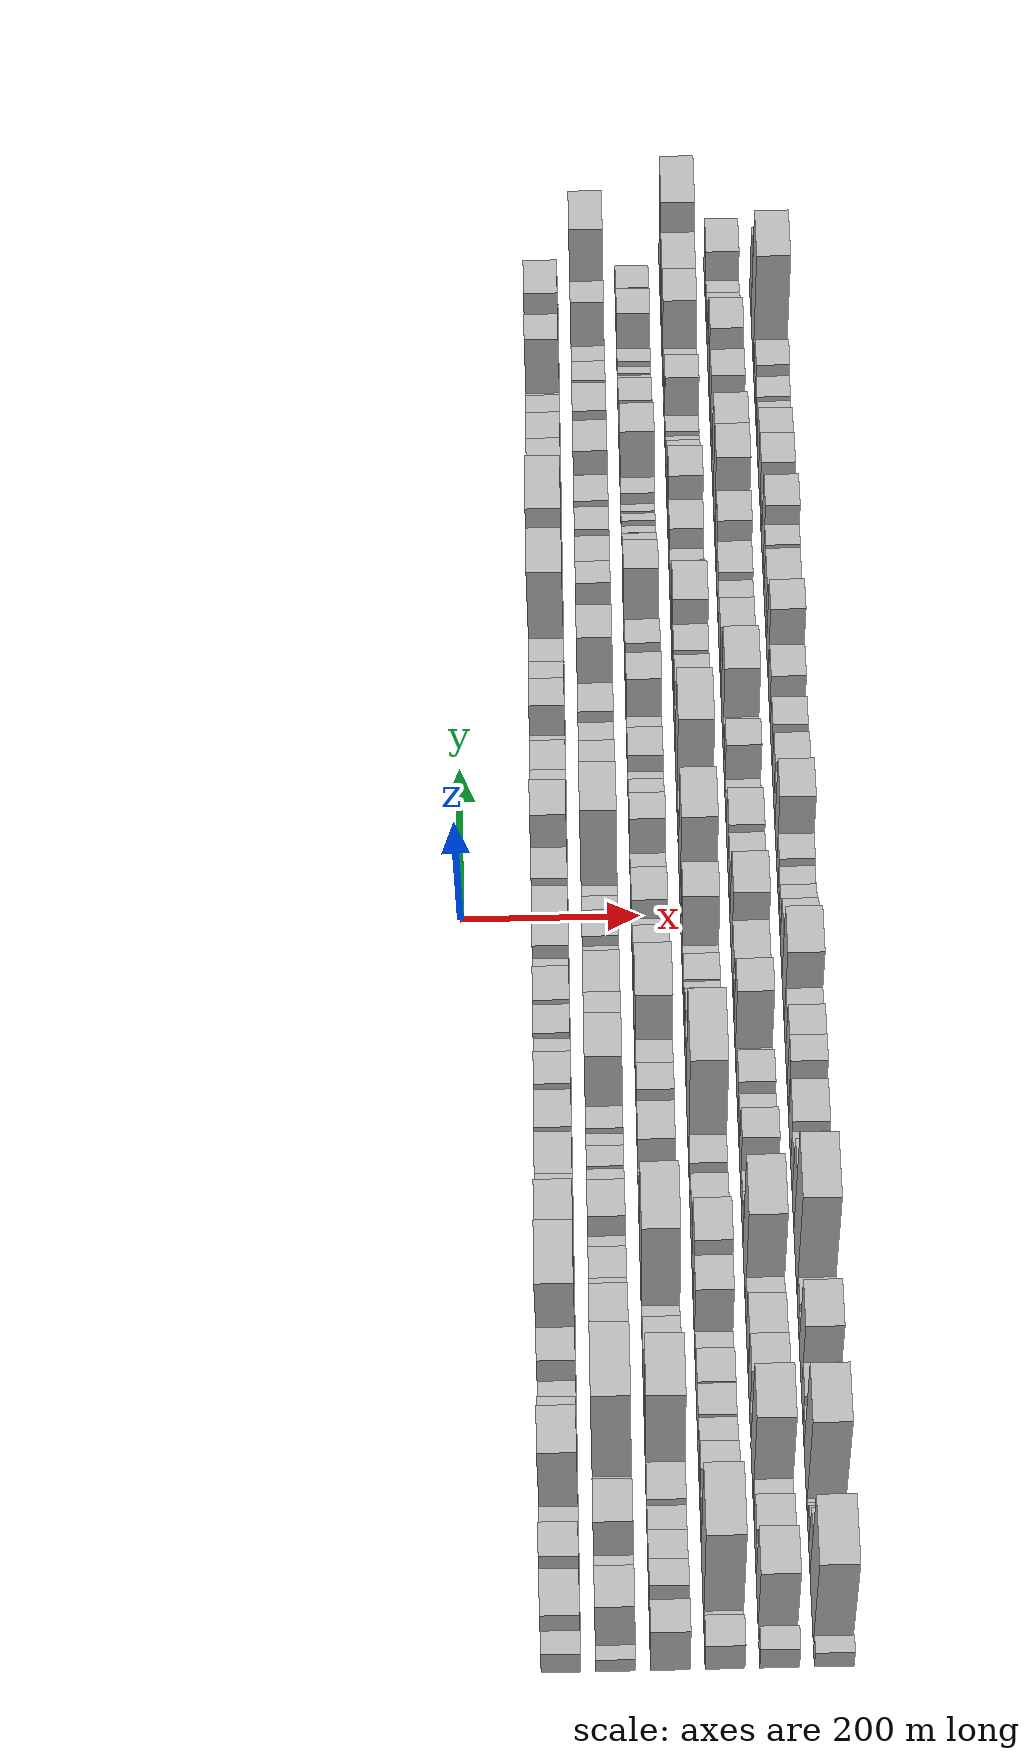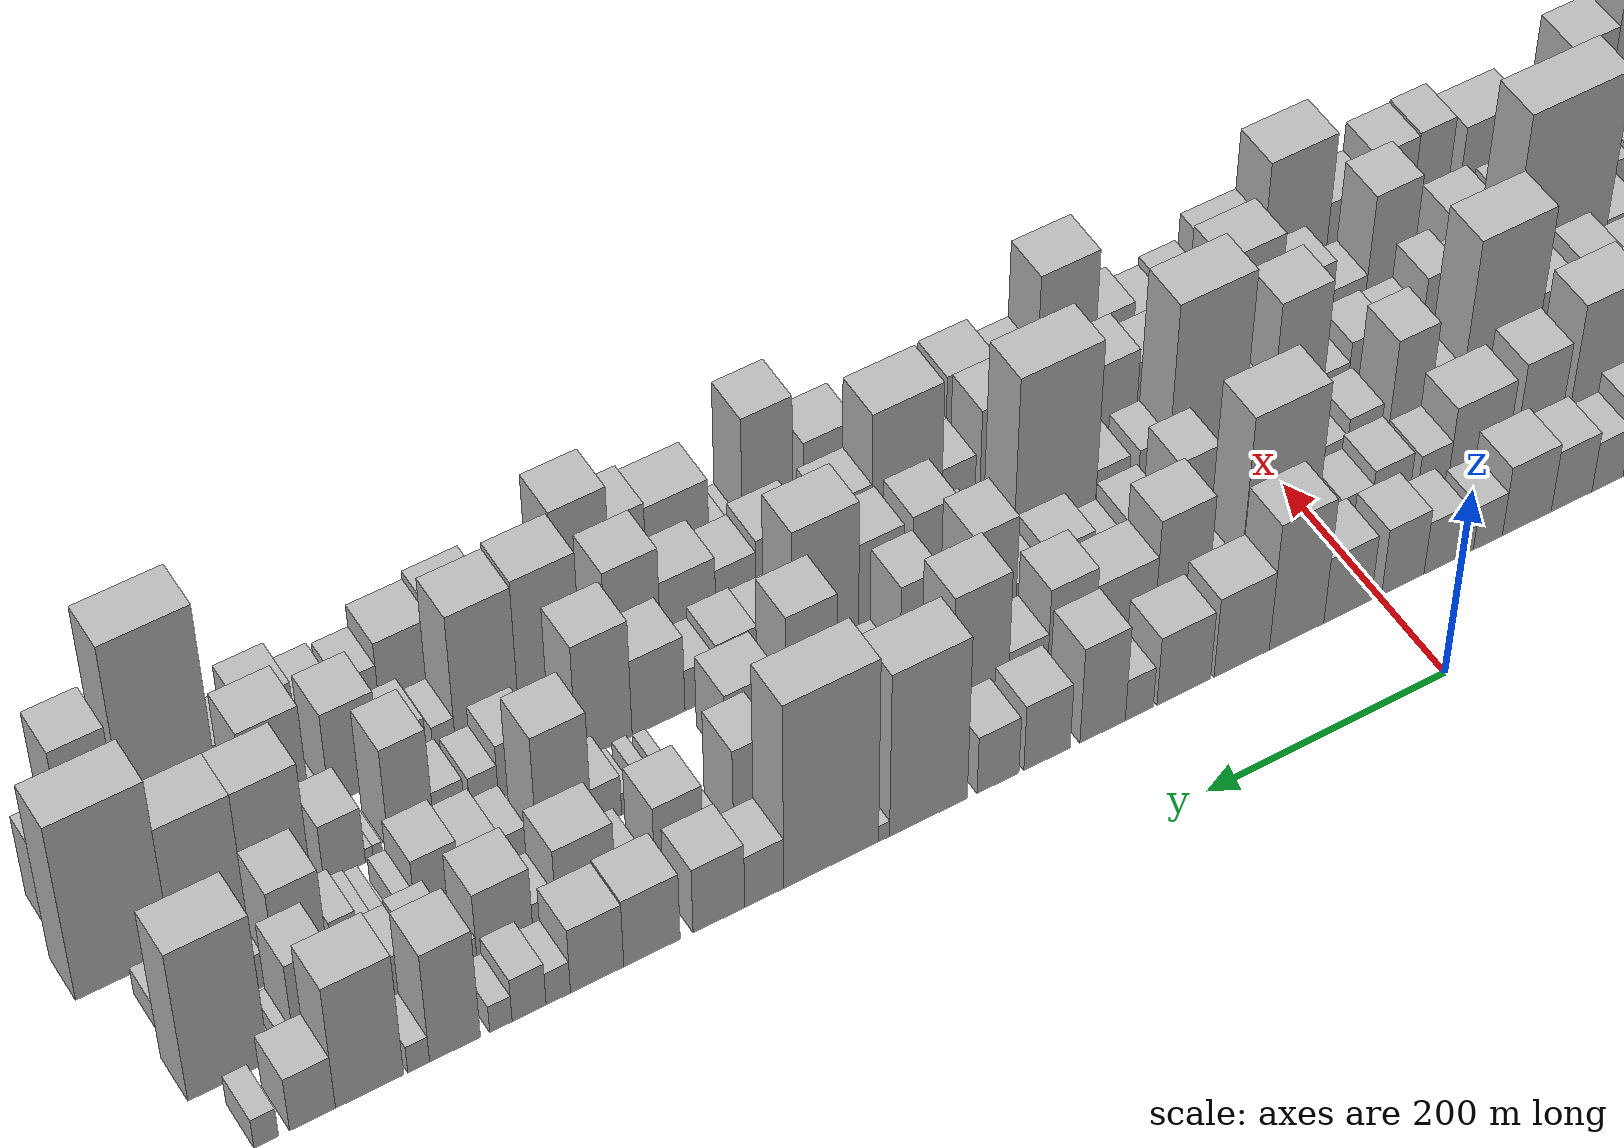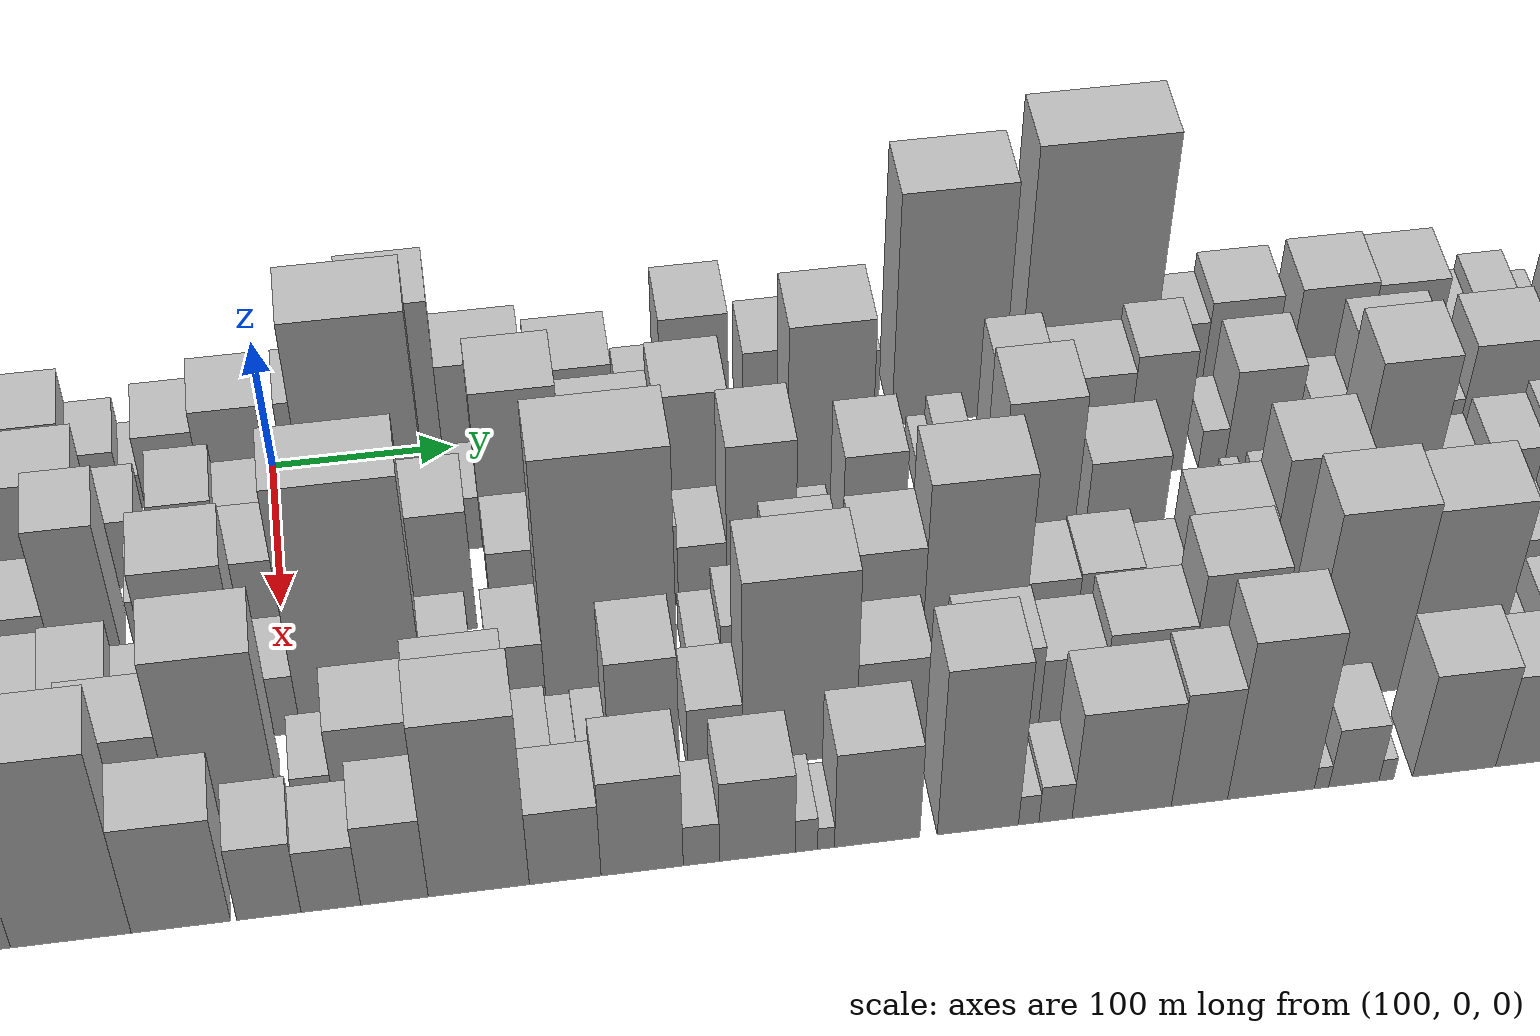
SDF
<sdf version="1.6">
 <world name="default">
  <scene>
   <sky><clouds><speed>12</speed></clouds></sky>
   <ambient>0.4 0.4 0.4 1</ambient>
   <background>0.7 0.7 0.7 1</background>
   <shadows>1</shadows>
  </scene>
  <gravity>0 0 -9.8066</gravity>
  <magnetic_field>6e-06 2.3e-05 -4.2e-05</magnetic_field>
  <physics default="0" name="default_physics" type="ode">
   <ode>
    <solver>
     <type>quick</type>
     <iters>10</iters>
     <sor>1.0</sor>
     <use_dynamic_moi_rescaling>0</use_dynamic_moi_rescaling>
    </solver>
    <constraints>
     <cfm>0</cfm>
     <erp>0.2</erp>
     <contact_max_correcting_vel>100</contact_max_correcting_vel>
     <contact_surface_layer>0.001</contact_surface_layer>
    </constraints>
   </ode>
   <max_step_size>0.004</max_step_size>
   <real_time_factor>1</real_time_factor>
   <real_time_update_rate>250</real_time_update_rate>
  </physics>
  <light name="sun" type="directional">
   <pose>0 0 10 0 0 0</pose>
   <diffuse>0.8 0.8 0.8 1</diffuse>
   <specular>0.2 0.2 0.2 1</specular>
   <attenuation>
    <range>1000</range>
    <constant>0.9</constant>
    <linear>0.01</linear>
    <quadratic>0.001</quadratic>
   </attenuation>
   <direction>-0.5 0.1 -0.9</direction>
  </light>
  <model name="building_1">
   <static>1</static>
   <pose>100.0000 -877.4478 0 0.000000 0.000000 0.000000</pose>
   <link name="link">
    <pose>0 0 24.00 0 0 0</pose>
    <collision name="collision"><geometry><box><size>40.0000 25.1045 48.0000</size></box></geometry></collision>
    <visual name="visual">
     <cast_shadows>0</cast_shadows>
     <geometry><box><size>40.0000 25.1045 48.0000</size></box></geometry>
     <material>
      <script>
       <uri>model://HANNAS_wall/materials/scripts</uri>
       <uri>model://HANNAS_wall/materials/textures</uri>
       <name>vrc/HANNAS_wall</name>
      </script>
     </material>
    </visual>
   </link>
  </model>
  <model name="building_2">
   <static>1</static>
   <pose>100.0000 -839.7803 0 0.000000 0.000000 0.000000</pose>
   <link name="link">
    <pose>0 0 43.50 0 0 0</pose>
    <collision name="collision"><geometry><box><size>40.0000 50.2305 87.0000</size></box></geometry></collision>
    <visual name="visual">
     <cast_shadows>0</cast_shadows>
     <geometry><box><size>40.0000 50.2305 87.0000</size></box></geometry>
     <material>
      <script>
       <uri>model://HANNAS_wall/materials/scripts</uri>
       <uri>model://HANNAS_wall/materials/textures</uri>
       <name>vrc/HANNAS_wall</name>
      </script>
     </material>
    </visual>
   </link>
  </model>
  <model name="building_3">
   <static>1</static>
   <pose>100.0000 -796.0003 0 0.000000 0.000000 0.000000</pose>
   <link name="link">
    <pose>0 0 58.50 0 0 0</pose>
    <collision name="collision"><geometry><box><size>40.0000 37.3295 117.0000</size></box></geometry></collision>
    <visual name="visual">
     <cast_shadows>0</cast_shadows>
     <geometry><box><size>40.0000 37.3295 117.0000</size></box></geometry>
     <material>
      <script>
       <uri>model://HANNAS_wall/materials/scripts</uri>
       <uri>model://HANNAS_wall/materials/textures</uri>
       <name>vrc/HANNAS_wall</name>
      </script>
     </material>
    </visual>
   </link>
  </model>
  <model name="building_4">
   <static>1</static>
   <pose>100.0000 -763.5788 0 0.000000 0.000000 0.000000</pose>
   <link name="link">
    <pose>0 0 25.50 0 0 0</pose>
    <collision name="collision"><geometry><box><size>40.0000 27.5136 51.0000</size></box></geometry></collision>
    <visual name="visual">
     <cast_shadows>0</cast_shadows>
     <geometry><box><size>40.0000 27.5136 51.0000</size></box></geometry>
     <material>
      <script>
       <uri>model://HANNAS_wall/materials/scripts</uri>
       <uri>model://HANNAS_wall/materials/textures</uri>
       <name>vrc/HANNAS_wall</name>
      </script>
     </material>
    </visual>
   </link>
  </model>
  <model name="building_5">
   <static>1</static>
   <pose>100.0000 -732.8521 0 0.000000 0.000000 0.000000</pose>
   <link name="link">
    <pose>0 0 16.50 0 0 0</pose>
    <collision name="collision"><geometry><box><size>40.0000 17.9398 33.0000</size></box></geometry></collision>
    <visual name="visual">
     <cast_shadows>0</cast_shadows>
     <geometry><box><size>40.0000 17.9398 33.0000</size></box></geometry>
     <material>
      <script>
       <uri>model://HANNAS_wall/materials/scripts</uri>
       <uri>model://HANNAS_wall/materials/textures</uri>
       <name>vrc/HANNAS_wall</name>
      </script>
     </material>
    </visual>
   </link>
  </model>
  <model name="building_6">
   <static>1</static>
   <pose>100.0000 -691.6194 0 0.000000 0.000000 0.000000</pose>
   <link name="link">
    <pose>0 0 75.00 0 0 0</pose>
    <collision name="collision"><geometry><box><size>40.0000 52.5255 150.0000</size></box></geometry></collision>
    <visual name="visual">
     <cast_shadows>0</cast_shadows>
     <geometry><box><size>40.0000 52.5255 150.0000</size></box></geometry>
     <material>
      <script>
       <uri>model://HANNAS_wall/materials/scripts</uri>
       <uri>model://HANNAS_wall/materials/textures</uri>
       <name>vrc/HANNAS_wall</name>
      </script>
     </material>
    </visual>
   </link>
  </model>
  <model name="building_7">
   <static>1</static>
   <pose>100.0000 -644.4254 0 0.000000 0.000000 0.000000</pose>
   <link name="link">
    <pose>0 0 40.50 0 0 0</pose>
    <collision name="collision"><geometry><box><size>40.0000 41.8624 81.0000</size></box></geometry></collision>
    <visual name="visual">
     <cast_shadows>0</cast_shadows>
     <geometry><box><size>40.0000 41.8624 81.0000</size></box></geometry>
     <material>
      <script>
       <uri>model://HANNAS_wall/materials/scripts</uri>
       <uri>model://HANNAS_wall/materials/textures</uri>
       <name>vrc/HANNAS_wall</name>
      </script>
     </material>
    </visual>
   </link>
  </model>
  <model name="building_8">
   <static>1</static>
   <pose>100.0000 -605.0732 0 0.000000 0.000000 0.000000</pose>
   <link name="link">
    <pose>0 0 25.50 0 0 0</pose>
    <collision name="collision"><geometry><box><size>40.0000 26.8420 51.0000</size></box></geometry></collision>
    <visual name="visual">
     <cast_shadows>0</cast_shadows>
     <geometry><box><size>40.0000 26.8420 51.0000</size></box></geometry>
     <material>
      <script>
       <uri>model://HANNAS_wall/materials/scripts</uri>
       <uri>model://HANNAS_wall/materials/textures</uri>
       <name>vrc/HANNAS_wall</name>
      </script>
     </material>
    </visual>
   </link>
  </model>
  <model name="building_9">
   <static>1</static>
   <pose>100.0000 -572.6820 0 0.000000 0.000000 0.000000</pose>
   <link name="link">
    <pose>0 0 49.50 0 0 0</pose>
    <collision name="collision"><geometry><box><size>40.0000 37.9405 99.0000</size></box></geometry></collision>
    <visual name="visual">
     <cast_shadows>0</cast_shadows>
     <geometry><box><size>40.0000 37.9405 99.0000</size></box></geometry>
     <material>
      <script>
       <uri>model://HANNAS_wall/materials/scripts</uri>
       <uri>model://HANNAS_wall/materials/textures</uri>
       <name>vrc/HANNAS_wall</name>
      </script>
     </material>
    </visual>
   </link>
  </model>
  <model name="building_10">
   <static>1</static>
   <pose>100.0000 -517.3630 0 0.000000 0.000000 0.000000</pose>
   <link name="link">
    <pose>0 0 99.00 0 0 0</pose>
    <collision name="collision"><geometry><box><size>40.0000 72.6974 198.0000</size></box></geometry></collision>
    <visual name="visual">
     <cast_shadows>0</cast_shadows>
     <geometry><box><size>40.0000 72.6974 198.0000</size></box></geometry>
     <material>
      <script>
       <uri>model://HANNAS_wall/materials/scripts</uri>
       <uri>model://HANNAS_wall/materials/textures</uri>
       <name>vrc/HANNAS_wall</name>
      </script>
     </material>
    </visual>
   </link>
  </model>
  <model name="building_11">
   <static>1</static>
   <pose>100.0000 -446.1428 0 0.000000 0.000000 0.000000</pose>
   <link name="link">
    <pose>0 0 84.00 0 0 0</pose>
    <collision name="collision"><geometry><box><size>40.0000 55.7430 168.0000</size></box></geometry></collision>
    <visual name="visual">
     <cast_shadows>0</cast_shadows>
     <geometry><box><size>40.0000 55.7430 168.0000</size></box></geometry>
     <material>
      <script>
       <uri>model://HANNAS_wall/materials/scripts</uri>
       <uri>model://HANNAS_wall/materials/textures</uri>
       <name>vrc/HANNAS_wall</name>
      </script>
     </material>
    </visual>
   </link>
  </model>
  <model name="building_12">
   <static>1</static>
   <pose>100.0000 -392.7327 0 0.000000 0.000000 0.000000</pose>
   <link name="link">
    <pose>0 0 45.00 0 0 0</pose>
    <collision name="collision"><geometry><box><size>40.0000 45.0773 90.0000</size></box></geometry></collision>
    <visual name="visual">
     <cast_shadows>0</cast_shadows>
     <geometry><box><size>40.0000 45.0773 90.0000</size></box></geometry>
     <material>
      <script>
       <uri>model://HANNAS_wall/materials/scripts</uri>
       <uri>model://HANNAS_wall/materials/textures</uri>
       <name>vrc/HANNAS_wall</name>
      </script>
     </material>
    </visual>
   </link>
  </model>
  <model name="building_13">
   <static>1</static>
   <pose>100.0000 -344.9859 0 0.000000 0.000000 0.000000</pose>
   <link name="link">
    <pose>0 0 45.00 0 0 0</pose>
    <collision name="collision"><geometry><box><size>40.0000 50.4162 90.0000</size></box></geometry></collision>
    <visual name="visual">
     <cast_shadows>0</cast_shadows>
     <geometry><box><size>40.0000 50.4162 90.0000</size></box></geometry>
     <material>
      <script>
       <uri>model://HANNAS_wall/materials/scripts</uri>
       <uri>model://HANNAS_wall/materials/textures</uri>
       <name>vrc/HANNAS_wall</name>
      </script>
     </material>
    </visual>
   </link>
  </model>
  <model name="building_14">
   <static>1</static>
   <pose>100.0000 -286.7651 0 0.000000 0.000000 0.000000</pose>
   <link name="link">
    <pose>0 0 40.50 0 0 0</pose>
    <collision name="collision"><geometry><box><size>40.0000 46.0253 81.0000</size></box></geometry></collision>
    <visual name="visual">
     <cast_shadows>0</cast_shadows>
     <geometry><box><size>40.0000 46.0253 81.0000</size></box></geometry>
     <material>
      <script>
       <uri>model://HANNAS_wall/materials/scripts</uri>
       <uri>model://HANNAS_wall/materials/textures</uri>
       <name>vrc/HANNAS_wall</name>
      </script>
     </material>
    </visual>
   </link>
  </model>
  <model name="building_15">
   <static>1</static>
   <pose>100.0000 -233.7372 0 0.000000 0.000000 0.000000</pose>
   <link name="link">
    <pose>0 0 37.50 0 0 0</pose>
    <collision name="collision"><geometry><box><size>40.0000 40.0307 75.0000</size></box></geometry></collision>
    <visual name="visual">
     <cast_shadows>0</cast_shadows>
     <geometry><box><size>40.0000 40.0307 75.0000</size></box></geometry>
     <material>
      <script>
       <uri>model://HANNAS_wall/materials/scripts</uri>
       <uri>model://HANNAS_wall/materials/textures</uri>
       <name>vrc/HANNAS_wall</name>
      </script>
     </material>
    </visual>
   </link>
  </model>
  <model name="building_16">
   <static>1</static>
   <pose>100.0000 -199.8380 0 0.000000 0.000000 0.000000</pose>
   <link name="link">
    <pose>0 0 27.00 0 0 0</pose>
    <collision name="collision"><geometry><box><size>40.0000 27.7676 54.0000</size></box></geometry></collision>
    <visual name="visual">
     <cast_shadows>0</cast_shadows>
     <geometry><box><size>40.0000 27.7676 54.0000</size></box></geometry>
     <material>
      <script>
       <uri>model://HANNAS_wall/materials/scripts</uri>
       <uri>model://HANNAS_wall/materials/textures</uri>
       <name>vrc/HANNAS_wall</name>
      </script>
     </material>
    </visual>
   </link>
  </model>
  <model name="building_17">
   <static>1</static>
   <pose>100.0000 -167.9313 0 0.000000 0.000000 0.000000</pose>
   <link name="link">
    <pose>0 0 33.00 0 0 0</pose>
    <collision name="collision"><geometry><box><size>40.0000 36.0459 66.0000</size></box></geometry></collision>
    <visual name="visual">
     <cast_shadows>0</cast_shadows>
     <geometry><box><size>40.0000 36.0459 66.0000</size></box></geometry>
     <material>
      <script>
       <uri>model://HANNAS_wall/materials/scripts</uri>
       <uri>model://HANNAS_wall/materials/textures</uri>
       <name>vrc/HANNAS_wall</name>
      </script>
     </material>
    </visual>
   </link>
  </model>
  <model name="building_18">
   <static>1</static>
   <pose>100.0000 -128.4174 0 0.000000 0.000000 0.000000</pose>
   <link name="link">
    <pose>0 0 37.50 0 0 0</pose>
    <collision name="collision"><geometry><box><size>40.0000 42.9818 75.0000</size></box></geometry></collision>
    <visual name="visual">
     <cast_shadows>0</cast_shadows>
     <geometry><box><size>40.0000 42.9818 75.0000</size></box></geometry>
     <material>
      <script>
       <uri>model://HANNAS_wall/materials/scripts</uri>
       <uri>model://HANNAS_wall/materials/textures</uri>
       <name>vrc/HANNAS_wall</name>
      </script>
     </material>
    </visual>
   </link>
  </model>
  <model name="building_19">
   <static>1</static>
   <pose>100.0000 -94.1826 0 0.000000 0.000000 0.000000</pose>
   <link name="link">
    <pose>0 0 24.00 0 0 0</pose>
    <collision name="collision"><geometry><box><size>40.0000 25.4878 48.0000</size></box></geometry></collision>
    <visual name="visual">
     <cast_shadows>0</cast_shadows>
     <geometry><box><size>40.0000 25.4878 48.0000</size></box></geometry>
     <material>
      <script>
       <uri>model://HANNAS_wall/materials/scripts</uri>
       <uri>model://HANNAS_wall/materials/textures</uri>
       <name>vrc/HANNAS_wall</name>
      </script>
     </material>
    </visual>
   </link>
  </model>
  <model name="building_20">
   <static>1</static>
   <pose>100.0000 -75.9171 0 0.000000 0.000000 0.000000</pose>
   <link name="link">
    <pose>0 0 13.50 0 0 0</pose>
    <collision name="collision"><geometry><box><size>40.0000 11.0433 27.0000</size></box></geometry></collision>
    <visual name="visual">
     <cast_shadows>0</cast_shadows>
     <geometry><box><size>40.0000 11.0433 27.0000</size></box></geometry>
     <material>
      <script>
       <uri>model://HANNAS_wall/materials/scripts</uri>
       <uri>model://HANNAS_wall/materials/textures</uri>
       <name>vrc/HANNAS_wall</name>
      </script>
     </material>
    </visual>
   </link>
  </model>
  <model name="building_21">
   <static>1</static>
   <pose>100.0000 -54.4602 0 0.000000 0.000000 0.000000</pose>
   <link name="link">
    <pose>0 0 28.50 0 0 0</pose>
    <collision name="collision"><geometry><box><size>40.0000 31.8704 57.0000</size></box></geometry></collision>
    <visual name="visual">
     <cast_shadows>0</cast_shadows>
     <geometry><box><size>40.0000 31.8704 57.0000</size></box></geometry>
     <material>
      <script>
       <uri>model://HANNAS_wall/materials/scripts</uri>
       <uri>model://HANNAS_wall/materials/textures</uri>
       <name>vrc/HANNAS_wall</name>
      </script>
     </material>
    </visual>
   </link>
  </model>
  <model name="building_22">
   <static>1</static>
   <pose>100.0000 -20.2143 0 0.000000 0.000000 0.000000</pose>
   <link name="link">
    <pose>0 0 36.00 0 0 0</pose>
    <collision name="collision"><geometry><box><size>40.0000 36.6214 72.0000</size></box></geometry></collision>
    <visual name="visual">
     <cast_shadows>0</cast_shadows>
     <geometry><box><size>40.0000 36.6214 72.0000</size></box></geometry>
     <material>
      <script>
       <uri>model://HANNAS_wall/materials/scripts</uri>
       <uri>model://HANNAS_wall/materials/textures</uri>
       <name>vrc/HANNAS_wall</name>
      </script>
     </material>
    </visual>
   </link>
  </model>
  <model name="building_23">
   <static>1</static>
   <pose>100.0000 27.4279 0 0.000000 0.000000 0.000000</pose>
   <link name="link">
    <pose>0 0 36.00 0 0 0</pose>
    <collision name="collision"><geometry><box><size>40.0000 40.6630 72.0000</size></box></geometry></collision>
    <visual name="visual">
     <cast_shadows>0</cast_shadows>
     <geometry><box><size>40.0000 40.6630 72.0000</size></box></geometry>
     <material>
      <script>
       <uri>model://HANNAS_wall/materials/scripts</uri>
       <uri>model://HANNAS_wall/materials/textures</uri>
       <name>vrc/HANNAS_wall</name>
      </script>
     </material>
    </visual>
   </link>
  </model>
  <model name="building_24">
   <static>1</static>
   <pose>100.0000 70.9083 0 0.000000 0.000000 0.000000</pose>
   <link name="link">
    <pose>0 0 69.00 0 0 0</pose>
    <collision name="collision"><geometry><box><size>40.0000 46.2979 138.0000</size></box></geometry></collision>
    <visual name="visual">
     <cast_shadows>0</cast_shadows>
     <geometry><box><size>40.0000 46.2979 138.0000</size></box></geometry>
     <material>
      <script>
       <uri>model://HANNAS_wall/materials/scripts</uri>
       <uri>model://HANNAS_wall/materials/textures</uri>
       <name>vrc/HANNAS_wall</name>
      </script>
     </material>
    </visual>
   </link>
  </model>
  <model name="building_25">
   <static>1</static>
   <pose>100.0000 117.3907 0 0.000000 0.000000 0.000000</pose>
   <link name="link">
    <pose>0 0 43.50 0 0 0</pose>
    <collision name="collision"><geometry><box><size>40.0000 46.6670 87.0000</size></box></geometry></collision>
    <visual name="visual">
     <cast_shadows>0</cast_shadows>
     <geometry><box><size>40.0000 46.6670 87.0000</size></box></geometry>
     <material>
      <script>
       <uri>model://HANNAS_wall/materials/scripts</uri>
       <uri>model://HANNAS_wall/materials/textures</uri>
       <name>vrc/HANNAS_wall</name>
      </script>
     </material>
    </visual>
   </link>
  </model>
  <model name="building_26">
   <static>1</static>
   <pose>100.0000 166.1145 0 0.000000 0.000000 0.000000</pose>
   <link name="link">
    <pose>0 0 37.50 0 0 0</pose>
    <collision name="collision"><geometry><box><size>40.0000 44.7805 75.0000</size></box></geometry></collision>
    <visual name="visual">
     <cast_shadows>0</cast_shadows>
     <geometry><box><size>40.0000 44.7805 75.0000</size></box></geometry>
     <material>
      <script>
       <uri>model://HANNAS_wall/materials/scripts</uri>
       <uri>model://HANNAS_wall/materials/textures</uri>
       <name>vrc/HANNAS_wall</name>
      </script>
     </material>
    </visual>
   </link>
  </model>
  <model name="building_27">
   <static>1</static>
   <pose>100.0000 203.1543 0 0.000000 0.000000 0.000000</pose>
   <link name="link">
    <pose>0 0 22.50 0 0 0</pose>
    <collision name="collision"><geometry><box><size>40.0000 23.2992 45.0000</size></box></geometry></collision>
    <visual name="visual">
     <cast_shadows>0</cast_shadows>
     <geometry><box><size>40.0000 23.2992 45.0000</size></box></geometry>
     <material>
      <script>
       <uri>model://HANNAS_wall/materials/scripts</uri>
       <uri>model://HANNAS_wall/materials/textures</uri>
       <name>vrc/HANNAS_wall</name>
      </script>
     </material>
    </visual>
   </link>
  </model>
  <model name="building_28">
   <static>1</static>
   <pose>100.0000 233.5581 0 0.000000 0.000000 0.000000</pose>
   <link name="link">
    <pose>0 0 52.50 0 0 0</pose>
    <collision name="collision"><geometry><box><size>40.0000 37.5084 105.0000</size></box></geometry></collision>
    <visual name="visual">
     <cast_shadows>0</cast_shadows>
     <geometry><box><size>40.0000 37.5084 105.0000</size></box></geometry>
     <material>
      <script>
       <uri>model://HANNAS_wall/materials/scripts</uri>
       <uri>model://HANNAS_wall/materials/textures</uri>
       <name>vrc/HANNAS_wall</name>
      </script>
     </material>
    </visual>
   </link>
  </model>
  <model name="building_29">
   <static>1</static>
   <pose>100.0000 279.2871 0 0.000000 0.000000 0.000000</pose>
   <link name="link">
    <pose>0 0 36.00 0 0 0</pose>
    <collision name="collision"><geometry><box><size>40.0000 37.9495 72.0000</size></box></geometry></collision>
    <visual name="visual">
     <cast_shadows>0</cast_shadows>
     <geometry><box><size>40.0000 37.9495 72.0000</size></box></geometry>
     <material>
      <script>
       <uri>model://HANNAS_wall/materials/scripts</uri>
       <uri>model://HANNAS_wall/materials/textures</uri>
       <name>vrc/HANNAS_wall</name>
      </script>
     </material>
    </visual>
   </link>
  </model>
  <model name="building_30">
   <static>1</static>
   <pose>100.0000 319.2841 0 0.000000 0.000000 0.000000</pose>
   <link name="link">
    <pose>0 0 31.50 0 0 0</pose>
    <collision name="collision"><geometry><box><size>40.0000 34.0445 63.0000</size></box></geometry></collision>
    <visual name="visual">
     <cast_shadows>0</cast_shadows>
     <geometry><box><size>40.0000 34.0445 63.0000</size></box></geometry>
     <material>
      <script>
       <uri>model://HANNAS_wall/materials/scripts</uri>
       <uri>model://HANNAS_wall/materials/textures</uri>
       <name>vrc/HANNAS_wall</name>
      </script>
     </material>
    </visual>
   </link>
  </model>
  <model name="building_31">
   <static>1</static>
   <pose>100.0000 375.5863 0 0.000000 0.000000 0.000000</pose>
   <link name="link">
    <pose>0 0 90.00 0 0 0</pose>
    <collision name="collision"><geometry><box><size>40.0000 62.5599 180.0000</size></box></geometry></collision>
    <visual name="visual">
     <cast_shadows>0</cast_shadows>
     <geometry><box><size>40.0000 62.5599 180.0000</size></box></geometry>
     <material>
      <script>
       <uri>model://HANNAS_wall/materials/scripts</uri>
       <uri>model://HANNAS_wall/materials/textures</uri>
       <name>vrc/HANNAS_wall</name>
      </script>
     </material>
    </visual>
   </link>
  </model>
  <model name="building_32">
   <static>1</static>
   <pose>100.0000 411.2604 0 0.000000 0.000000 0.000000</pose>
   <link name="link">
    <pose>0 0 9.00 0 0 0</pose>
    <collision name="collision"><geometry><box><size>40.0000 8.7883 18.0000</size></box></geometry></collision>
    <visual name="visual">
     <cast_shadows>0</cast_shadows>
     <geometry><box><size>40.0000 8.7883 18.0000</size></box></geometry>
     <material>
      <script>
       <uri>model://HANNAS_wall/materials/scripts</uri>
       <uri>model://HANNAS_wall/materials/textures</uri>
       <name>vrc/HANNAS_wall</name>
      </script>
     </material>
    </visual>
   </link>
  </model>
  <model name="building_33">
   <static>1</static>
   <pose>100.0000 453.2576 0 0.000000 0.000000 0.000000</pose>
   <link name="link">
    <pose>0 0 102.00 0 0 0</pose>
    <collision name="collision"><geometry><box><size>40.0000 75.2060 204.0000</size></box></geometry></collision>
    <visual name="visual">
     <cast_shadows>0</cast_shadows>
     <geometry><box><size>40.0000 75.2060 204.0000</size></box></geometry>
     <material>
      <script>
       <uri>model://HANNAS_wall/materials/scripts</uri>
       <uri>model://HANNAS_wall/materials/textures</uri>
       <name>vrc/HANNAS_wall</name>
      </script>
     </material>
    </visual>
   </link>
  </model>
  <model name="building_34">
   <static>1</static>
   <pose>100.0000 506.1924 0 0.000000 0.000000 0.000000</pose>
   <link name="link">
    <pose>0 0 28.50 0 0 0</pose>
    <collision name="collision"><geometry><box><size>40.0000 30.6637 57.0000</size></box></geometry></collision>
    <visual name="visual">
     <cast_shadows>0</cast_shadows>
     <geometry><box><size>40.0000 30.6637 57.0000</size></box></geometry>
     <material>
      <script>
       <uri>model://HANNAS_wall/materials/scripts</uri>
       <uri>model://HANNAS_wall/materials/textures</uri>
       <name>vrc/HANNAS_wall</name>
      </script>
     </material>
    </visual>
   </link>
  </model>
  <model name="building_35">
   <static>1</static>
   <pose>100.0000 541.7542 0 0.000000 0.000000 0.000000</pose>
   <link name="link">
    <pose>0 0 36.00 0 0 0</pose>
    <collision name="collision"><geometry><box><size>40.0000 40.4598 72.0000</size></box></geometry></collision>
    <visual name="visual">
     <cast_shadows>0</cast_shadows>
     <geometry><box><size>40.0000 40.4598 72.0000</size></box></geometry>
     <material>
      <script>
       <uri>model://HANNAS_wall/materials/scripts</uri>
       <uri>model://HANNAS_wall/materials/textures</uri>
       <name>vrc/HANNAS_wall</name>
      </script>
     </material>
    </visual>
   </link>
  </model>
  <model name="building_36">
   <static>1</static>
   <pose>100.0000 593.8116 0 0.000000 0.000000 0.000000</pose>
   <link name="link">
    <pose>0 0 37.50 0 0 0</pose>
    <collision name="collision"><geometry><box><size>40.0000 43.6551 75.0000</size></box></geometry></collision>
    <visual name="visual">
     <cast_shadows>0</cast_shadows>
     <geometry><box><size>40.0000 43.6551 75.0000</size></box></geometry>
     <material>
      <script>
       <uri>model://HANNAS_wall/materials/scripts</uri>
       <uri>model://HANNAS_wall/materials/textures</uri>
       <name>vrc/HANNAS_wall</name>
      </script>
     </material>
    </visual>
   </link>
  </model>
  <model name="building_37">
   <static>1</static>
   <pose>100.0000 636.0833 0 0.000000 0.000000 0.000000</pose>
   <link name="link">
    <pose>0 0 36.00 0 0 0</pose>
    <collision name="collision"><geometry><box><size>40.0000 40.8883 72.0000</size></box></geometry></collision>
    <visual name="visual">
     <cast_shadows>0</cast_shadows>
     <geometry><box><size>40.0000 40.8883 72.0000</size></box></geometry>
     <material>
      <script>
       <uri>model://HANNAS_wall/materials/scripts</uri>
       <uri>model://HANNAS_wall/materials/textures</uri>
       <name>vrc/HANNAS_wall</name>
      </script>
     </material>
    </visual>
   </link>
  </model>
  <model name="building_38">
   <static>1</static>
   <pose>100.0000 665.8280 0 0.000000 0.000000 0.000000</pose>
   <link name="link">
    <pose>0 0 18.00 0 0 0</pose>
    <collision name="collision"><geometry><box><size>40.0000 18.6011 36.0000</size></box></geometry></collision>
    <visual name="visual">
     <cast_shadows>0</cast_shadows>
     <geometry><box><size>40.0000 18.6011 36.0000</size></box></geometry>
     <material>
      <script>
       <uri>model://HANNAS_wall/materials/scripts</uri>
       <uri>model://HANNAS_wall/materials/textures</uri>
       <name>vrc/HANNAS_wall</name>
      </script>
     </material>
    </visual>
   </link>
  </model>
  <model name="building_39">
   <static>1</static>
   <pose>100.0000 688.0652 0 0.000000 0.000000 0.000000</pose>
   <link name="link">
    <pose>0 0 24.00 0 0 0</pose>
    <collision name="collision"><geometry><box><size>40.0000 25.8733 48.0000</size></box></geometry></collision>
    <visual name="visual">
     <cast_shadows>0</cast_shadows>
     <geometry><box><size>40.0000 25.8733 48.0000</size></box></geometry>
     <material>
      <script>
       <uri>model://HANNAS_wall/materials/scripts</uri>
       <uri>model://HANNAS_wall/materials/textures</uri>
       <name>vrc/HANNAS_wall</name>
      </script>
     </material>
    </visual>
   </link>
  </model>
  <model name="building_40">
   <static>1</static>
   <pose>100.0000 709.4919 0 0.000000 0.000000 0.000000</pose>
   <link name="link">
    <pose>0 0 15.00 0 0 0</pose>
    <collision name="collision"><geometry><box><size>40.0000 16.9801 30.0000</size></box></geometry></collision>
    <visual name="visual">
     <cast_shadows>0</cast_shadows>
     <geometry><box><size>40.0000 16.9801 30.0000</size></box></geometry>
     <material>
      <script>
       <uri>model://HANNAS_wall/materials/scripts</uri>
       <uri>model://HANNAS_wall/materials/textures</uri>
       <name>vrc/HANNAS_wall</name>
      </script>
     </material>
    </visual>
   </link>
  </model>
  <model name="building_41">
   <static>1</static>
   <pose>100.0000 744.1133 0 0.000000 0.000000 0.000000</pose>
   <link name="link">
    <pose>0 0 61.50 0 0 0</pose>
    <collision name="collision"><geometry><box><size>40.0000 38.2626 123.0000</size></box></geometry></collision>
    <visual name="visual">
     <cast_shadows>0</cast_shadows>
     <geometry><box><size>40.0000 38.2626 123.0000</size></box></geometry>
     <material>
      <script>
       <uri>model://HANNAS_wall/materials/scripts</uri>
       <uri>model://HANNAS_wall/materials/textures</uri>
       <name>vrc/HANNAS_wall</name>
      </script>
     </material>
    </visual>
   </link>
  </model>
  <model name="building_42">
   <static>1</static>
   <pose>100.0000 771.4472 0 0.000000 0.000000 0.000000</pose>
   <link name="link">
    <pose>0 0 15.00 0 0 0</pose>
    <collision name="collision"><geometry><box><size>40.0000 16.4053 30.0000</size></box></geometry></collision>
    <visual name="visual">
     <cast_shadows>0</cast_shadows>
     <geometry><box><size>40.0000 16.4053 30.0000</size></box></geometry>
     <material>
      <script>
       <uri>model://HANNAS_wall/materials/scripts</uri>
       <uri>model://HANNAS_wall/materials/textures</uri>
       <name>vrc/HANNAS_wall</name>
      </script>
     </material>
    </visual>
   </link>
  </model>
  <model name="building_43">
   <static>1</static>
   <pose>100.0000 807.9860 0 0.000000 0.000000 0.000000</pose>
   <link name="link">
    <pose>0 0 69.00 0 0 0</pose>
    <collision name="collision"><geometry><box><size>40.0000 50.6723 138.0000</size></box></geometry></collision>
    <visual name="visual">
     <cast_shadows>0</cast_shadows>
     <geometry><box><size>40.0000 50.6723 138.0000</size></box></geometry>
     <material>
      <script>
       <uri>model://HANNAS_wall/materials/scripts</uri>
       <uri>model://HANNAS_wall/materials/textures</uri>
       <name>vrc/HANNAS_wall</name>
      </script>
     </material>
    </visual>
   </link>
  </model>
  <model name="building_44">
   <static>1</static>
   <pose>100.0000 850.2724 0 0.000000 0.000000 0.000000</pose>
   <link name="link">
    <pose>0 0 30.00 0 0 0</pose>
    <collision name="collision"><geometry><box><size>40.0000 33.9005 60.0000</size></box></geometry></collision>
    <visual name="visual">
     <cast_shadows>0</cast_shadows>
     <geometry><box><size>40.0000 33.9005 60.0000</size></box></geometry>
     <material>
      <script>
       <uri>model://HANNAS_wall/materials/scripts</uri>
       <uri>model://HANNAS_wall/materials/textures</uri>
       <name>vrc/HANNAS_wall</name>
      </script>
     </material>
    </visual>
   </link>
  </model>
  <model name="building_45">
   <static>1</static>
   <pose>100.0000 884.2753 0 0.000000 0.000000 0.000000</pose>
   <link name="link">
    <pose>0 0 16.50 0 0 0</pose>
    <collision name="collision"><geometry><box><size>40.0000 18.1052 33.0000</size></box></geometry></collision>
    <visual name="visual">
     <cast_shadows>0</cast_shadows>
     <geometry><box><size>40.0000 18.1052 33.0000</size></box></geometry>
     <material>
      <script>
       <uri>model://HANNAS_wall/materials/scripts</uri>
       <uri>model://HANNAS_wall/materials/textures</uri>
       <name>vrc/HANNAS_wall</name>
      </script>
     </material>
    </visual>
   </link>
  </model>
  <model name="building_46">
   <static>1</static>
   <pose>155.0000 -882.0637 0 0.000000 0.000000 0.000000</pose>
   <link name="link">
    <pose>0 0 15.00 0 0 0</pose>
    <collision name="collision"><geometry><box><size>40.0000 15.8725 30.0000</size></box></geometry></collision>
    <visual name="visual">
     <cast_shadows>0</cast_shadows>
     <geometry><box><size>40.0000 15.8725 30.0000</size></box></geometry>
     <material>
      <script>
       <uri>model://HANNAS_wall/materials/scripts</uri>
       <uri>model://HANNAS_wall/materials/textures</uri>
       <name>vrc/HANNAS_wall</name>
      </script>
     </material>
    </visual>
   </link>
  </model>
  <model name="building_47">
   <static>1</static>
   <pose>155.0000 -844.9315 0 0.000000 0.000000 0.000000</pose>
   <link name="link">
    <pose>0 0 55.50 0 0 0</pose>
    <collision name="collision"><geometry><box><size>40.0000 44.3920 111.0000</size></box></geometry></collision>
    <visual name="visual">
     <cast_shadows>0</cast_shadows>
     <geometry><box><size>40.0000 44.3920 111.0000</size></box></geometry>
     <material>
      <script>
       <uri>model://HANNAS_wall/materials/scripts</uri>
       <uri>model://HANNAS_wall/materials/textures</uri>
       <name>vrc/HANNAS_wall</name>
      </script>
     </material>
    </visual>
   </link>
  </model>
  <model name="building_48">
   <static>1</static>
   <pose>155.0000 -803.8946 0 0.000000 0.000000 0.000000</pose>
   <link name="link">
    <pose>0 0 28.50 0 0 0</pose>
    <collision name="collision"><geometry><box><size>40.0000 29.6819 57.0000</size></box></geometry></collision>
    <visual name="visual">
     <cast_shadows>0</cast_shadows>
     <geometry><box><size>40.0000 29.6819 57.0000</size></box></geometry>
     <material>
      <script>
       <uri>model://HANNAS_wall/materials/scripts</uri>
       <uri>model://HANNAS_wall/materials/textures</uri>
       <name>vrc/HANNAS_wall</name>
      </script>
     </material>
    </visual>
   </link>
  </model>
  <model name="building_49">
   <static>1</static>
   <pose>155.0000 -760.6865 0 0.000000 0.000000 0.000000</pose>
   <link name="link">
    <pose>0 0 64.50 0 0 0</pose>
    <collision name="collision"><geometry><box><size>40.0000 46.7343 129.0000</size></box></geometry></collision>
    <visual name="visual">
     <cast_shadows>0</cast_shadows>
     <geometry><box><size>40.0000 46.7343 129.0000</size></box></geometry>
     <material>
      <script>
       <uri>model://HANNAS_wall/materials/scripts</uri>
       <uri>model://HANNAS_wall/materials/textures</uri>
       <name>vrc/HANNAS_wall</name>
      </script>
     </material>
    </visual>
   </link>
  </model>
  <model name="building_50">
   <static>1</static>
   <pose>155.0000 -733.6499 0 0.000000 0.000000 0.000000</pose>
   <link name="link">
    <pose>0 0 9.00 0 0 0</pose>
    <collision name="collision"><geometry><box><size>40.0000 7.3388 18.0000</size></box></geometry></collision>
    <visual name="visual">
     <cast_shadows>0</cast_shadows>
     <geometry><box><size>40.0000 7.3388 18.0000</size></box></geometry>
     <material>
      <script>
       <uri>model://HANNAS_wall/materials/scripts</uri>
       <uri>model://HANNAS_wall/materials/textures</uri>
       <name>vrc/HANNAS_wall</name>
      </script>
     </material>
    </visual>
   </link>
  </model>
  <model name="building_51">
   <static>1</static>
   <pose>155.0000 -715.0751 0 0.000000 0.000000 0.000000</pose>
   <link name="link">
    <pose>0 0 25.50 0 0 0</pose>
    <collision name="collision"><geometry><box><size>40.0000 29.8109 51.0000</size></box></geometry></collision>
    <visual name="visual">
     <cast_shadows>0</cast_shadows>
     <geometry><box><size>40.0000 29.8109 51.0000</size></box></geometry>
     <material>
      <script>
       <uri>model://HANNAS_wall/materials/scripts</uri>
       <uri>model://HANNAS_wall/materials/textures</uri>
       <name>vrc/HANNAS_wall</name>
      </script>
     </material>
    </visual>
   </link>
  </model>
  <model name="building_52">
   <static>1</static>
   <pose>155.0000 -651.3712 0 0.000000 0.000000 0.000000</pose>
   <link name="link">
    <pose>0 0 112.50 0 0 0</pose>
    <collision name="collision"><geometry><box><size>40.0000 81.5970 225.0000</size></box></geometry></collision>
    <visual name="visual">
     <cast_shadows>0</cast_shadows>
     <geometry><box><size>40.0000 81.5970 225.0000</size></box></geometry>
     <material>
      <script>
       <uri>model://HANNAS_wall/materials/scripts</uri>
       <uri>model://HANNAS_wall/materials/textures</uri>
       <name>vrc/HANNAS_wall</name>
      </script>
     </material>
    </visual>
   </link>
  </model>
  <model name="building_53">
   <static>1</static>
   <pose>155.0000 -591.2501 0 0.000000 0.000000 0.000000</pose>
   <link name="link">
    <pose>0 0 36.00 0 0 0</pose>
    <collision name="collision"><geometry><box><size>40.0000 38.6452 72.0000</size></box></geometry></collision>
    <visual name="visual">
     <cast_shadows>0</cast_shadows>
     <geometry><box><size>40.0000 38.6452 72.0000</size></box></geometry>
     <material>
      <script>
       <uri>model://HANNAS_wall/materials/scripts</uri>
       <uri>model://HANNAS_wall/materials/textures</uri>
       <name>vrc/HANNAS_wall</name>
      </script>
     </material>
    </visual>
   </link>
  </model>
  <model name="building_54">
   <static>1</static>
   <pose>155.0000 -547.9047 0 0.000000 0.000000 0.000000</pose>
   <link name="link">
    <pose>0 0 69.00 0 0 0</pose>
    <collision name="collision"><geometry><box><size>40.0000 48.0456 138.0000</size></box></geometry></collision>
    <visual name="visual">
     <cast_shadows>0</cast_shadows>
     <geometry><box><size>40.0000 48.0456 138.0000</size></box></geometry>
     <material>
      <script>
       <uri>model://HANNAS_wall/materials/scripts</uri>
       <uri>model://HANNAS_wall/materials/textures</uri>
       <name>vrc/HANNAS_wall</name>
      </script>
     </material>
    </visual>
   </link>
  </model>
  <model name="building_55">
   <static>1</static>
   <pose>155.0000 -498.0649 0 0.000000 0.000000 0.000000</pose>
   <link name="link">
    <pose>0 0 31.50 0 0 0</pose>
    <collision name="collision"><geometry><box><size>40.0000 35.6341 63.0000</size></box></geometry></collision>
    <visual name="visual">
     <cast_shadows>0</cast_shadows>
     <geometry><box><size>40.0000 35.6341 63.0000</size></box></geometry>
     <material>
      <script>
       <uri>model://HANNAS_wall/materials/scripts</uri>
       <uri>model://HANNAS_wall/materials/textures</uri>
       <name>vrc/HANNAS_wall</name>
      </script>
     </material>
    </visual>
   </link>
  </model>
  <model name="building_56">
   <static>1</static>
   <pose>155.0000 -461.8014 0 0.000000 0.000000 0.000000</pose>
   <link name="link">
    <pose>0 0 31.50 0 0 0</pose>
    <collision name="collision"><geometry><box><size>40.0000 36.8928 63.0000</size></box></geometry></collision>
    <visual name="visual">
     <cast_shadows>0</cast_shadows>
     <geometry><box><size>40.0000 36.8928 63.0000</size></box></geometry>
     <material>
      <script>
       <uri>model://HANNAS_wall/materials/scripts</uri>
       <uri>model://HANNAS_wall/materials/textures</uri>
       <name>vrc/HANNAS_wall</name>
      </script>
     </material>
    </visual>
   </link>
  </model>
  <model name="building_57">
   <static>1</static>
   <pose>155.0000 -437.0089 0 0.000000 0.000000 0.000000</pose>
   <link name="link">
    <pose>0 0 13.50 0 0 0</pose>
    <collision name="collision"><geometry><box><size>40.0000 12.6923 27.0000</size></box></geometry></collision>
    <visual name="visual">
     <cast_shadows>0</cast_shadows>
     <geometry><box><size>40.0000 12.6923 27.0000</size></box></geometry>
     <material>
      <script>
       <uri>model://HANNAS_wall/materials/scripts</uri>
       <uri>model://HANNAS_wall/materials/textures</uri>
       <name>vrc/HANNAS_wall</name>
      </script>
     </material>
    </visual>
   </link>
  </model>
  <model name="building_58">
   <static>1</static>
   <pose>155.0000 -422.4467 0 0.000000 0.000000 0.000000</pose>
   <link name="link">
    <pose>0 0 15.00 0 0 0</pose>
    <collision name="collision"><geometry><box><size>40.0000 16.4323 30.0000</size></box></geometry></collision>
    <visual name="visual">
     <cast_shadows>0</cast_shadows>
     <geometry><box><size>40.0000 16.4323 30.0000</size></box></geometry>
     <material>
      <script>
       <uri>model://HANNAS_wall/materials/scripts</uri>
       <uri>model://HANNAS_wall/materials/textures</uri>
       <name>vrc/HANNAS_wall</name>
      </script>
     </material>
    </visual>
   </link>
  </model>
  <model name="building_59">
   <static>1</static>
   <pose>155.0000 -392.2543 0 0.000000 0.000000 0.000000</pose>
   <link name="link">
    <pose>0 0 37.50 0 0 0</pose>
    <collision name="collision"><geometry><box><size>40.0000 43.9524 75.0000</size></box></geometry></collision>
    <visual name="visual">
     <cast_shadows>0</cast_shadows>
     <geometry><box><size>40.0000 43.9524 75.0000</size></box></geometry>
     <material>
      <script>
       <uri>model://HANNAS_wall/materials/scripts</uri>
       <uri>model://HANNAS_wall/materials/textures</uri>
       <name>vrc/HANNAS_wall</name>
      </script>
     </material>
    </visual>
   </link>
  </model>
  <model name="building_60">
   <static>1</static>
   <pose>155.0000 -352.2055 0 0.000000 0.000000 0.000000</pose>
   <link name="link">
    <pose>0 0 21.00 0 0 0</pose>
    <collision name="collision"><geometry><box><size>40.0000 24.1453 42.0000</size></box></geometry></collision>
    <visual name="visual">
     <cast_shadows>0</cast_shadows>
     <geometry><box><size>40.0000 24.1453 42.0000</size></box></geometry>
     <material>
      <script>
       <uri>model://HANNAS_wall/materials/scripts</uri>
       <uri>model://HANNAS_wall/materials/textures</uri>
       <name>vrc/HANNAS_wall</name>
      </script>
     </material>
    </visual>
   </link>
  </model>
  <model name="building_61">
   <static>1</static>
   <pose>155.0000 -327.6031 0 0.000000 0.000000 0.000000</pose>
   <link name="link">
    <pose>0 0 24.00 0 0 0</pose>
    <collision name="collision"><geometry><box><size>40.0000 25.0594 48.0000</size></box></geometry></collision>
    <visual name="visual">
     <cast_shadows>0</cast_shadows>
     <geometry><box><size>40.0000 25.0594 48.0000</size></box></geometry>
     <material>
      <script>
       <uri>model://HANNAS_wall/materials/scripts</uri>
       <uri>model://HANNAS_wall/materials/textures</uri>
       <name>vrc/HANNAS_wall</name>
      </script>
     </material>
    </visual>
   </link>
  </model>
  <model name="building_62">
   <static>1</static>
   <pose>155.0000 -304.6756 0 0.000000 0.000000 0.000000</pose>
   <link name="link">
    <pose>0 0 18.00 0 0 0</pose>
    <collision name="collision"><geometry><box><size>40.0000 20.7958 36.0000</size></box></geometry></collision>
    <visual name="visual">
     <cast_shadows>0</cast_shadows>
     <geometry><box><size>40.0000 20.7958 36.0000</size></box></geometry>
     <material>
      <script>
       <uri>model://HANNAS_wall/materials/scripts</uri>
       <uri>model://HANNAS_wall/materials/textures</uri>
       <name>vrc/HANNAS_wall</name>
      </script>
     </material>
    </visual>
   </link>
  </model>
  <model name="building_63">
   <static>1</static>
   <pose>155.0000 -280.7747 0 0.000000 0.000000 0.000000</pose>
   <link name="link">
    <pose>0 0 24.00 0 0 0</pose>
    <collision name="collision"><geometry><box><size>40.0000 27.0058 48.0000</size></box></geometry></collision>
    <visual name="visual">
     <cast_shadows>0</cast_shadows>
     <geometry><box><size>40.0000 27.0058 48.0000</size></box></geometry>
     <material>
      <script>
       <uri>model://HANNAS_wall/materials/scripts</uri>
       <uri>model://HANNAS_wall/materials/textures</uri>
       <name>vrc/HANNAS_wall</name>
      </script>
     </material>
    </visual>
   </link>
  </model>
  <model name="building_64">
   <static>1</static>
   <pose>155.0000 -230.3528 0 0.000000 0.000000 0.000000</pose>
   <link name="link">
    <pose>0 0 69.00 0 0 0</pose>
    <collision name="collision"><geometry><box><size>40.0000 53.8381 138.0000</size></box></geometry></collision>
    <visual name="visual">
     <cast_shadows>0</cast_shadows>
     <geometry><box><size>40.0000 53.8381 138.0000</size></box></geometry>
     <material>
      <script>
       <uri>model://HANNAS_wall/materials/scripts</uri>
       <uri>model://HANNAS_wall/materials/textures</uri>
       <name>vrc/HANNAS_wall</name>
      </script>
     </material>
    </visual>
   </link>
  </model>
  <model name="building_65">
   <static>1</static>
   <pose>155.0000 -176.5464 0 0.000000 0.000000 0.000000</pose>
   <link name="link">
    <pose>0 0 51.00 0 0 0</pose>
    <collision name="collision"><geometry><box><size>40.0000 39.7746 102.0000</size></box></geometry></collision>
    <visual name="visual">
     <cast_shadows>0</cast_shadows>
     <geometry><box><size>40.0000 39.7746 102.0000</size></box></geometry>
     <material>
      <script>
       <uri>model://HANNAS_wall/materials/scripts</uri>
       <uri>model://HANNAS_wall/materials/textures</uri>
       <name>vrc/HANNAS_wall</name>
      </script>
     </material>
    </visual>
   </link>
  </model>
  <model name="building_66">
   <static>1</static>
   <pose>155.0000 -123.4491 0 0.000000 0.000000 0.000000</pose>
   <link name="link">
    <pose>0 0 45.00 0 0 0</pose>
    <collision name="collision"><geometry><box><size>40.0000 52.4199 90.0000</size></box></geometry></collision>
    <visual name="visual">
     <cast_shadows>0</cast_shadows>
     <geometry><box><size>40.0000 52.4199 90.0000</size></box></geometry>
     <material>
      <script>
       <uri>model://HANNAS_wall/materials/scripts</uri>
       <uri>model://HANNAS_wall/materials/textures</uri>
       <name>vrc/HANNAS_wall</name>
      </script>
     </material>
    </visual>
   </link>
  </model>
  <model name="building_67">
   <static>1</static>
   <pose>155.0000 -83.6687 0 0.000000 0.000000 0.000000</pose>
   <link name="link">
    <pose>0 0 27.00 0 0 0</pose>
    <collision name="collision"><geometry><box><size>40.0000 27.1410 54.0000</size></box></geometry></collision>
    <visual name="visual">
     <cast_shadows>0</cast_shadows>
     <geometry><box><size>40.0000 27.1410 54.0000</size></box></geometry>
     <material>
      <script>
       <uri>model://HANNAS_wall/materials/scripts</uri>
       <uri>model://HANNAS_wall/materials/textures</uri>
       <name>vrc/HANNAS_wall</name>
      </script>
     </material>
    </visual>
   </link>
  </model>
  <model name="building_68">
   <static>1</static>
   <pose>155.0000 -66.5116 0 0.000000 0.000000 0.000000</pose>
   <link name="link">
    <pose>0 0 7.50 0 0 0</pose>
    <collision name="collision"><geometry><box><size>40.0000 7.1732 15.0000</size></box></geometry></collision>
    <visual name="visual">
     <cast_shadows>0</cast_shadows>
     <geometry><box><size>40.0000 7.1732 15.0000</size></box></geometry>
     <material>
      <script>
       <uri>model://HANNAS_wall/materials/scripts</uri>
       <uri>model://HANNAS_wall/materials/textures</uri>
       <name>vrc/HANNAS_wall</name>
      </script>
     </material>
    </visual>
   </link>
  </model>
  <model name="building_69">
   <static>1</static>
   <pose>155.0000 -46.1079 0 0.000000 0.000000 0.000000</pose>
   <link name="link">
    <pose>0 0 31.50 0 0 0</pose>
    <collision name="collision"><geometry><box><size>40.0000 33.6343 63.0000</size></box></geometry></collision>
    <visual name="visual">
     <cast_shadows>0</cast_shadows>
     <geometry><box><size>40.0000 33.6343 63.0000</size></box></geometry>
     <material>
      <script>
       <uri>model://HANNAS_wall/materials/scripts</uri>
       <uri>model://HANNAS_wall/materials/textures</uri>
       <name>vrc/HANNAS_wall</name>
      </script>
     </material>
    </visual>
   </link>
  </model>
  <model name="building_70">
   <static>1</static>
   <pose>155.0000 -15.5659 0 0.000000 0.000000 0.000000</pose>
   <link name="link">
    <pose>0 0 24.00 0 0 0</pose>
    <collision name="collision"><geometry><box><size>40.0000 27.4497 48.0000</size></box></geometry></collision>
    <visual name="visual">
     <cast_shadows>0</cast_shadows>
     <geometry><box><size>40.0000 27.4497 48.0000</size></box></geometry>
     <material>
      <script>
       <uri>model://HANNAS_wall/materials/scripts</uri>
       <uri>model://HANNAS_wall/materials/textures</uri>
       <name>vrc/HANNAS_wall</name>
      </script>
     </material>
    </visual>
   </link>
  </model>
  <model name="building_71">
   <static>1</static>
   <pose>155.0000 8.6668 0 0.000000 0.000000 0.000000</pose>
   <link name="link">
    <pose>0 0 18.00 0 0 0</pose>
    <collision name="collision"><geometry><box><size>40.0000 21.0157 36.0000</size></box></geometry></collision>
    <visual name="visual">
     <cast_shadows>0</cast_shadows>
     <geometry><box><size>40.0000 21.0157 36.0000</size></box></geometry>
     <material>
      <script>
       <uri>model://HANNAS_wall/materials/scripts</uri>
       <uri>model://HANNAS_wall/materials/textures</uri>
       <name>vrc/HANNAS_wall</name>
      </script>
     </material>
    </visual>
   </link>
  </model>
  <model name="building_72">
   <static>1</static>
   <pose>155.0000 50.9459 0 0.000000 0.000000 0.000000</pose>
   <link name="link">
    <pose>0 0 94.50 0 0 0</pose>
    <collision name="collision"><geometry><box><size>40.0000 63.5425 189.0000</size></box></geometry></collision>
    <visual name="visual">
     <cast_shadows>0</cast_shadows>
     <geometry><box><size>40.0000 63.5425 189.0000</size></box></geometry>
     <material>
      <script>
       <uri>model://HANNAS_wall/materials/scripts</uri>
       <uri>model://HANNAS_wall/materials/textures</uri>
       <name>vrc/HANNAS_wall</name>
      </script>
     </material>
    </visual>
   </link>
  </model>
  <model name="building_73">
   <static>1</static>
   <pose>155.0000 98.8356 0 0.000000 0.000000 0.000000</pose>
   <link name="link">
    <pose>0 0 21.00 0 0 0</pose>
    <collision name="collision"><geometry><box><size>40.0000 22.2368 42.0000</size></box></geometry></collision>
    <visual name="visual">
     <cast_shadows>0</cast_shadows>
     <geometry><box><size>40.0000 22.2368 42.0000</size></box></geometry>
     <material>
      <script>
       <uri>model://HANNAS_wall/materials/scripts</uri>
       <uri>model://HANNAS_wall/materials/textures</uri>
       <name>vrc/HANNAS_wall</name>
      </script>
     </material>
    </visual>
   </link>
  </model>
  <model name="building_74">
   <static>1</static>
   <pose>155.0000 132.4688 0 0.000000 0.000000 0.000000</pose>
   <link name="link">
    <pose>0 0 61.50 0 0 0</pose>
    <collision name="collision"><geometry><box><size>40.0000 45.0297 123.0000</size></box></geometry></collision>
    <visual name="visual">
     <cast_shadows>0</cast_shadows>
     <geometry><box><size>40.0000 45.0297 123.0000</size></box></geometry>
     <material>
      <script>
       <uri>model://HANNAS_wall/materials/scripts</uri>
       <uri>model://HANNAS_wall/materials/textures</uri>
       <name>vrc/HANNAS_wall</name>
      </script>
     </material>
    </visual>
   </link>
  </model>
  <model name="building_75">
   <static>1</static>
   <pose>155.0000 180.1663 0 0.000000 0.000000 0.000000</pose>
   <link name="link">
    <pose>0 0 42.00 0 0 0</pose>
    <collision name="collision"><geometry><box><size>40.0000 50.3654 84.0000</size></box></geometry></collision>
    <visual name="visual">
     <cast_shadows>0</cast_shadows>
     <geometry><box><size>40.0000 50.3654 84.0000</size></box></geometry>
     <material>
      <script>
       <uri>model://HANNAS_wall/materials/scripts</uri>
       <uri>model://HANNAS_wall/materials/textures</uri>
       <name>vrc/HANNAS_wall</name>
      </script>
     </material>
    </visual>
   </link>
  </model>
  <model name="building_76">
   <static>1</static>
   <pose>155.0000 224.8794 0 0.000000 0.000000 0.000000</pose>
   <link name="link">
    <pose>0 0 52.50 0 0 0</pose>
    <collision name="collision"><geometry><box><size>40.0000 39.0606 105.0000</size></box></geometry></collision>
    <visual name="visual">
     <cast_shadows>0</cast_shadows>
     <geometry><box><size>40.0000 39.0606 105.0000</size></box></geometry>
     <material>
      <script>
       <uri>model://HANNAS_wall/materials/scripts</uri>
       <uri>model://HANNAS_wall/materials/textures</uri>
       <name>vrc/HANNAS_wall</name>
      </script>
     </material>
    </visual>
   </link>
  </model>
  <model name="building_77">
   <static>1</static>
   <pose>155.0000 260.6749 0 0.000000 0.000000 0.000000</pose>
   <link name="link">
    <pose>0 0 28.50 0 0 0</pose>
    <collision name="collision"><geometry><box><size>40.0000 32.5305 57.0000</size></box></geometry></collision>
    <visual name="visual">
     <cast_shadows>0</cast_shadows>
     <geometry><box><size>40.0000 32.5305 57.0000</size></box></geometry>
     <material>
      <script>
       <uri>model://HANNAS_wall/materials/scripts</uri>
       <uri>model://HANNAS_wall/materials/textures</uri>
       <name>vrc/HANNAS_wall</name>
      </script>
     </material>
    </visual>
   </link>
  </model>
  <model name="building_78">
   <static>1</static>
   <pose>155.0000 299.9093 0 0.000000 0.000000 0.000000</pose>
   <link name="link">
    <pose>0 0 73.50 0 0 0</pose>
    <collision name="collision"><geometry><box><size>40.0000 45.9384 147.0000</size></box></geometry></collision>
    <visual name="visual">
     <cast_shadows>0</cast_shadows>
     <geometry><box><size>40.0000 45.9384 147.0000</size></box></geometry>
     <material>
      <script>
       <uri>model://HANNAS_wall/materials/scripts</uri>
       <uri>model://HANNAS_wall/materials/textures</uri>
       <name>vrc/HANNAS_wall</name>
      </script>
     </material>
    </visual>
   </link>
  </model>
  <model name="building_79">
   <static>1</static>
   <pose>155.0000 331.8587 0 0.000000 0.000000 0.000000</pose>
   <link name="link">
    <pose>0 0 15.00 0 0 0</pose>
    <collision name="collision"><geometry><box><size>40.0000 17.9605 30.0000</size></box></geometry></collision>
    <visual name="visual">
     <cast_shadows>0</cast_shadows>
     <geometry><box><size>40.0000 17.9605 30.0000</size></box></geometry>
     <material>
      <script>
       <uri>model://HANNAS_wall/materials/scripts</uri>
       <uri>model://HANNAS_wall/materials/textures</uri>
       <name>vrc/HANNAS_wall</name>
      </script>
     </material>
    </visual>
   </link>
  </model>
  <model name="building_80">
   <static>1</static>
   <pose>155.0000 354.1871 0 0.000000 0.000000 0.000000</pose>
   <link name="link">
    <pose>0 0 12.00 0 0 0</pose>
    <collision name="collision"><geometry><box><size>40.0000 10.6962 24.0000</size></box></geometry></collision>
    <visual name="visual">
     <cast_shadows>0</cast_shadows>
     <geometry><box><size>40.0000 10.6962 24.0000</size></box></geometry>
     <material>
      <script>
       <uri>model://HANNAS_wall/materials/scripts</uri>
       <uri>model://HANNAS_wall/materials/textures</uri>
       <name>vrc/HANNAS_wall</name>
      </script>
     </material>
    </visual>
   </link>
  </model>
  <model name="building_81">
   <static>1</static>
   <pose>155.0000 369.3860 0 0.000000 0.000000 0.000000</pose>
   <link name="link">
    <pose>0 0 19.50 0 0 0</pose>
    <collision name="collision"><geometry><box><size>40.0000 19.7015 39.0000</size></box></geometry></collision>
    <visual name="visual">
     <cast_shadows>0</cast_shadows>
     <geometry><box><size>40.0000 19.7015 39.0000</size></box></geometry>
     <material>
      <script>
       <uri>model://HANNAS_wall/materials/scripts</uri>
       <uri>model://HANNAS_wall/materials/textures</uri>
       <name>vrc/HANNAS_wall</name>
      </script>
     </material>
    </visual>
   </link>
  </model>
  <model name="building_82">
   <static>1</static>
   <pose>155.0000 404.8058 0 0.000000 0.000000 0.000000</pose>
   <link name="link">
    <pose>0 0 48.00 0 0 0</pose>
    <collision name="collision"><geometry><box><size>40.0000 31.1381 96.0000</size></box></geometry></collision>
    <visual name="visual">
     <cast_shadows>0</cast_shadows>
     <geometry><box><size>40.0000 31.1381 96.0000</size></box></geometry>
     <material>
      <script>
       <uri>model://HANNAS_wall/materials/scripts</uri>
       <uri>model://HANNAS_wall/materials/textures</uri>
       <name>vrc/HANNAS_wall</name>
      </script>
     </material>
    </visual>
   </link>
  </model>
  <model name="building_83">
   <static>1</static>
   <pose>155.0000 442.7776 0 0.000000 0.000000 0.000000</pose>
   <link name="link">
    <pose>0 0 42.00 0 0 0</pose>
    <collision name="collision"><geometry><box><size>40.0000 44.8055 84.0000</size></box></geometry></collision>
    <visual name="visual">
     <cast_shadows>0</cast_shadows>
     <geometry><box><size>40.0000 44.8055 84.0000</size></box></geometry>
     <material>
      <script>
       <uri>model://HANNAS_wall/materials/scripts</uri>
       <uri>model://HANNAS_wall/materials/textures</uri>
       <name>vrc/HANNAS_wall</name>
      </script>
     </material>
    </visual>
   </link>
  </model>
  <model name="building_84">
   <static>1</static>
   <pose>155.0000 481.5834 0 0.000000 0.000000 0.000000</pose>
   <link name="link">
    <pose>0 0 48.00 0 0 0</pose>
    <collision name="collision"><geometry><box><size>40.0000 32.8061 96.0000</size></box></geometry></collision>
    <visual name="visual">
     <cast_shadows>0</cast_shadows>
     <geometry><box><size>40.0000 32.8061 96.0000</size></box></geometry>
     <material>
      <script>
       <uri>model://HANNAS_wall/materials/scripts</uri>
       <uri>model://HANNAS_wall/materials/textures</uri>
       <name>vrc/HANNAS_wall</name>
      </script>
     </material>
    </visual>
   </link>
  </model>
  <model name="building_85">
   <static>1</static>
   <pose>155.0000 514.5166 0 0.000000 0.000000 0.000000</pose>
   <link name="link">
    <pose>0 0 15.00 0 0 0</pose>
    <collision name="collision"><geometry><box><size>40.0000 15.0602 30.0000</size></box></geometry></collision>
    <visual name="visual">
     <cast_shadows>0</cast_shadows>
     <geometry><box><size>40.0000 15.0602 30.0000</size></box></geometry>
     <material>
      <script>
       <uri>model://HANNAS_wall/materials/scripts</uri>
       <uri>model://HANNAS_wall/materials/textures</uri>
       <name>vrc/HANNAS_wall</name>
      </script>
     </material>
    </visual>
   </link>
  </model>
  <model name="building_86">
   <static>1</static>
   <pose>155.0000 541.0794 0 0.000000 0.000000 0.000000</pose>
   <link name="link">
    <pose>0 0 37.50 0 0 0</pose>
    <collision name="collision"><geometry><box><size>40.0000 38.0653 75.0000</size></box></geometry></collision>
    <visual name="visual">
     <cast_shadows>0</cast_shadows>
     <geometry><box><size>40.0000 38.0653 75.0000</size></box></geometry>
     <material>
      <script>
       <uri>model://HANNAS_wall/materials/scripts</uri>
       <uri>model://HANNAS_wall/materials/textures</uri>
       <name>vrc/HANNAS_wall</name>
      </script>
     </material>
    </visual>
   </link>
  </model>
  <model name="building_87">
   <static>1</static>
   <pose>155.0000 579.8306 0 0.000000 0.000000 0.000000</pose>
   <link name="link">
    <pose>0 0 18.00 0 0 0</pose>
    <collision name="collision"><geometry><box><size>40.0000 21.4372 36.0000</size></box></geometry></collision>
    <visual name="visual">
     <cast_shadows>0</cast_shadows>
     <geometry><box><size>40.0000 21.4372 36.0000</size></box></geometry>
     <material>
      <script>
       <uri>model://HANNAS_wall/materials/scripts</uri>
       <uri>model://HANNAS_wall/materials/textures</uri>
       <name>vrc/HANNAS_wall</name>
      </script>
     </material>
    </visual>
   </link>
  </model>
  <model name="building_88">
   <static>1</static>
   <pose>155.0000 613.5350 0 0.000000 0.000000 0.000000</pose>
   <link name="link">
    <pose>0 0 40.50 0 0 0</pose>
    <collision name="collision"><geometry><box><size>40.0000 45.9716 81.0000</size></box></geometry></collision>
    <visual name="visual">
     <cast_shadows>0</cast_shadows>
     <geometry><box><size>40.0000 45.9716 81.0000</size></box></geometry>
     <material>
      <script>
       <uri>model://HANNAS_wall/materials/scripts</uri>
       <uri>model://HANNAS_wall/materials/textures</uri>
       <name>vrc/HANNAS_wall</name>
      </script>
     </material>
    </visual>
   </link>
  </model>
  <model name="building_89">
   <static>1</static>
   <pose>155.0000 645.5434 0 0.000000 0.000000 0.000000</pose>
   <link name="link">
    <pose>0 0 16.50 0 0 0</pose>
    <collision name="collision"><geometry><box><size>40.0000 18.0453 33.0000</size></box></geometry></collision>
    <visual name="visual">
     <cast_shadows>0</cast_shadows>
     <geometry><box><size>40.0000 18.0453 33.0000</size></box></geometry>
     <material>
      <script>
       <uri>model://HANNAS_wall/materials/scripts</uri>
       <uri>model://HANNAS_wall/materials/textures</uri>
       <name>vrc/HANNAS_wall</name>
      </script>
     </material>
    </visual>
   </link>
  </model>
  <model name="building_90">
   <static>1</static>
   <pose>155.0000 676.0283 0 0.000000 0.000000 0.000000</pose>
   <link name="link">
    <pose>0 0 37.50 0 0 0</pose>
    <collision name="collision"><geometry><box><size>40.0000 42.9245 75.0000</size></box></geometry></collision>
    <visual name="visual">
     <cast_shadows>0</cast_shadows>
     <geometry><box><size>40.0000 42.9245 75.0000</size></box></geometry>
     <material>
      <script>
       <uri>model://HANNAS_wall/materials/scripts</uri>
       <uri>model://HANNAS_wall/materials/textures</uri>
       <name>vrc/HANNAS_wall</name>
      </script>
     </material>
    </visual>
   </link>
  </model>
  <model name="building_91">
   <static>1</static>
   <pose>155.0000 703.8665 0 0.000000 0.000000 0.000000</pose>
   <link name="link">
    <pose>0 0 13.50 0 0 0</pose>
    <collision name="collision"><geometry><box><size>40.0000 12.7519 27.0000</size></box></geometry></collision>
    <visual name="visual">
     <cast_shadows>0</cast_shadows>
     <geometry><box><size>40.0000 12.7519 27.0000</size></box></geometry>
     <material>
      <script>
       <uri>model://HANNAS_wall/materials/scripts</uri>
       <uri>model://HANNAS_wall/materials/textures</uri>
       <name>vrc/HANNAS_wall</name>
      </script>
     </material>
    </visual>
   </link>
  </model>
  <model name="building_92">
   <static>1</static>
   <pose>155.0000 729.1125 0 0.000000 0.000000 0.000000</pose>
   <link name="link">
    <pose>0 0 28.50 0 0 0</pose>
    <collision name="collision"><geometry><box><size>40.0000 29.7401 57.0000</size></box></geometry></collision>
    <visual name="visual">
     <cast_shadows>0</cast_shadows>
     <geometry><box><size>40.0000 29.7401 57.0000</size></box></geometry>
     <material>
      <script>
       <uri>model://HANNAS_wall/materials/scripts</uri>
       <uri>model://HANNAS_wall/materials/textures</uri>
       <name>vrc/HANNAS_wall</name>
      </script>
     </material>
    </visual>
   </link>
  </model>
  <model name="building_93">
   <static>1</static>
   <pose>155.0000 757.8463 0 0.000000 0.000000 0.000000</pose>
   <link name="link">
    <pose>0 0 25.50 0 0 0</pose>
    <collision name="collision"><geometry><box><size>40.0000 27.7275 51.0000</size></box></geometry></collision>
    <visual name="visual">
     <cast_shadows>0</cast_shadows>
     <geometry><box><size>40.0000 27.7275 51.0000</size></box></geometry>
     <material>
      <script>
       <uri>model://HANNAS_wall/materials/scripts</uri>
       <uri>model://HANNAS_wall/materials/textures</uri>
       <name>vrc/HANNAS_wall</name>
      </script>
     </material>
    </visual>
   </link>
  </model>
  <model name="building_94">
   <static>1</static>
   <pose>155.0000 781.1396 0 0.000000 0.000000 0.000000</pose>
   <link name="link">
    <pose>0 0 9.00 0 0 0</pose>
    <collision name="collision"><geometry><box><size>40.0000 8.8591 18.0000</size></box></geometry></collision>
    <visual name="visual">
     <cast_shadows>0</cast_shadows>
     <geometry><box><size>40.0000 8.8591 18.0000</size></box></geometry>
     <material>
      <script>
       <uri>model://HANNAS_wall/materials/scripts</uri>
       <uri>model://HANNAS_wall/materials/textures</uri>
       <name>vrc/HANNAS_wall</name>
      </script>
     </material>
    </visual>
   </link>
  </model>
  <model name="building_95">
   <static>1</static>
   <pose>155.0000 790.2828 0 0.000000 0.000000 0.000000</pose>
   <link name="link">
    <pose>0 0 10.50 0 0 0</pose>
    <collision name="collision"><geometry><box><size>40.0000 9.4273 21.0000</size></box></geometry></collision>
    <visual name="visual">
     <cast_shadows>0</cast_shadows>
     <geometry><box><size>40.0000 9.4273 21.0000</size></box></geometry>
     <material>
      <script>
       <uri>model://HANNAS_wall/materials/scripts</uri>
       <uri>model://HANNAS_wall/materials/textures</uri>
       <name>vrc/HANNAS_wall</name>
      </script>
     </material>
    </visual>
   </link>
  </model>
  <model name="building_96">
   <static>1</static>
   <pose>155.0000 818.4181 0 0.000000 0.000000 0.000000</pose>
   <link name="link">
    <pose>0 0 48.00 0 0 0</pose>
    <collision name="collision"><geometry><box><size>40.0000 32.8434 96.0000</size></box></geometry></collision>
    <visual name="visual">
     <cast_shadows>0</cast_shadows>
     <geometry><box><size>40.0000 32.8434 96.0000</size></box></geometry>
     <material>
      <script>
       <uri>model://HANNAS_wall/materials/scripts</uri>
       <uri>model://HANNAS_wall/materials/textures</uri>
       <name>vrc/HANNAS_wall</name>
      </script>
     </material>
    </visual>
   </link>
  </model>
  <model name="building_97">
   <static>1</static>
   <pose>155.0000 839.2624 0 0.000000 0.000000 0.000000</pose>
   <link name="link">
    <pose>0 0 10.50 0 0 0</pose>
    <collision name="collision"><geometry><box><size>40.0000 8.8451 21.0000</size></box></geometry></collision>
    <visual name="visual">
     <cast_shadows>0</cast_shadows>
     <geometry><box><size>40.0000 8.8451 21.0000</size></box></geometry>
     <material>
      <script>
       <uri>model://HANNAS_wall/materials/scripts</uri>
       <uri>model://HANNAS_wall/materials/textures</uri>
       <name>vrc/HANNAS_wall</name>
      </script>
     </material>
    </visual>
   </link>
  </model>
  <model name="building_98">
   <static>1</static>
   <pose>155.0000 883.8250 0 0.000000 0.000000 0.000000</pose>
   <link name="link">
    <pose>0 0 84.00 0 0 0</pose>
    <collision name="collision"><geometry><box><size>40.0000 60.2800 168.0000</size></box></geometry></collision>
    <visual name="visual">
     <cast_shadows>0</cast_shadows>
     <geometry><box><size>40.0000 60.2800 168.0000</size></box></geometry>
     <material>
      <script>
       <uri>model://HANNAS_wall/materials/scripts</uri>
       <uri>model://HANNAS_wall/materials/textures</uri>
       <name>vrc/HANNAS_wall</name>
      </script>
     </material>
    </visual>
   </link>
  </model>
  <model name="building_99">
   <static>1</static>
   <pose>210.0000 -872.4733 0 0.000000 0.000000 0.000000</pose>
   <link name="link">
    <pose>0 0 49.50 0 0 0</pose>
    <collision name="collision"><geometry><box><size>40.0000 35.0534 99.0000</size></box></geometry></collision>
    <visual name="visual">
     <cast_shadows>0</cast_shadows>
     <geometry><box><size>40.0000 35.0534 99.0000</size></box></geometry>
     <material>
      <script>
       <uri>model://HANNAS_wall/materials/scripts</uri>
       <uri>model://HANNAS_wall/materials/textures</uri>
       <name>vrc/HANNAS_wall</name>
      </script>
     </material>
    </visual>
   </link>
  </model>
  <model name="building_100">
   <static>1</static>
   <pose>210.0000 -846.4295 0 0.000000 0.000000 0.000000</pose>
   <link name="link">
    <pose>0 0 16.50 0 0 0</pose>
    <collision name="collision"><geometry><box><size>40.0000 17.0342 33.0000</size></box></geometry></collision>
    <visual name="visual">
     <cast_shadows>0</cast_shadows>
     <geometry><box><size>40.0000 17.0342 33.0000</size></box></geometry>
     <material>
      <script>
       <uri>model://HANNAS_wall/materials/scripts</uri>
       <uri>model://HANNAS_wall/materials/textures</uri>
       <name>vrc/HANNAS_wall</name>
      </script>
     </material>
    </visual>
   </link>
  </model>
  <model name="building_101">
   <static>1</static>
   <pose>210.0000 -823.4933 0 0.000000 0.000000 0.000000</pose>
   <link name="link">
    <pose>0 0 46.50 0 0 0</pose>
    <collision name="collision"><geometry><box><size>40.0000 28.8382 93.0000</size></box></geometry></collision>
    <visual name="visual">
     <cast_shadows>0</cast_shadows>
     <geometry><box><size>40.0000 28.8382 93.0000</size></box></geometry>
     <material>
      <script>
       <uri>model://HANNAS_wall/materials/scripts</uri>
       <uri>model://HANNAS_wall/materials/textures</uri>
       <name>vrc/HANNAS_wall</name>
      </script>
     </material>
    </visual>
   </link>
  </model>
  <model name="building_102">
   <static>1</static>
   <pose>210.0000 -786.2546 0 0.000000 0.000000 0.000000</pose>
   <link name="link">
    <pose>0 0 34.50 0 0 0</pose>
    <collision name="collision"><geometry><box><size>40.0000 37.6391 69.0000</size></box></geometry></collision>
    <visual name="visual">
     <cast_shadows>0</cast_shadows>
     <geometry><box><size>40.0000 37.6391 69.0000</size></box></geometry>
     <material>
      <script>
       <uri>model://HANNAS_wall/materials/scripts</uri>
       <uri>model://HANNAS_wall/materials/textures</uri>
       <name>vrc/HANNAS_wall</name>
      </script>
     </material>
    </visual>
   </link>
  </model>
  <model name="building_103">
   <static>1</static>
   <pose>210.0000 -751.5960 0 0.000000 0.000000 0.000000</pose>
   <link name="link">
    <pose>0 0 28.50 0 0 0</pose>
    <collision name="collision"><geometry><box><size>40.0000 31.6781 57.0000</size></box></geometry></collision>
    <visual name="visual">
     <cast_shadows>0</cast_shadows>
     <geometry><box><size>40.0000 31.6781 57.0000</size></box></geometry>
     <material>
      <script>
       <uri>model://HANNAS_wall/materials/scripts</uri>
       <uri>model://HANNAS_wall/materials/textures</uri>
       <name>vrc/HANNAS_wall</name>
      </script>
     </material>
    </visual>
   </link>
  </model>
  <model name="building_104">
   <static>1</static>
   <pose>210.0000 -715.1206 0 0.000000 0.000000 0.000000</pose>
   <link name="link">
    <pose>0 0 36.00 0 0 0</pose>
    <collision name="collision"><geometry><box><size>40.0000 41.2726 72.0000</size></box></geometry></collision>
    <visual name="visual">
     <cast_shadows>0</cast_shadows>
     <geometry><box><size>40.0000 41.2726 72.0000</size></box></geometry>
     <material>
      <script>
       <uri>model://HANNAS_wall/materials/scripts</uri>
       <uri>model://HANNAS_wall/materials/textures</uri>
       <name>vrc/HANNAS_wall</name>
      </script>
     </material>
    </visual>
   </link>
  </model>
  <model name="building_105">
   <static>1</static>
   <pose>210.0000 -654.0828 0 0.000000 0.000000 0.000000</pose>
   <link name="link">
    <pose>0 0 108.00 0 0 0</pose>
    <collision name="collision"><geometry><box><size>40.0000 68.8032 216.0000</size></box></geometry></collision>
    <visual name="visual">
     <cast_shadows>0</cast_shadows>
     <geometry><box><size>40.0000 68.8032 216.0000</size></box></geometry>
     <material>
      <script>
       <uri>model://HANNAS_wall/materials/scripts</uri>
       <uri>model://HANNAS_wall/materials/textures</uri>
       <name>vrc/HANNAS_wall</name>
      </script>
     </material>
    </visual>
   </link>
  </model>
  <model name="building_106">
   <static>1</static>
   <pose>210.0000 -597.1380 0 0.000000 0.000000 0.000000</pose>
   <link name="link">
    <pose>0 0 42.00 0 0 0</pose>
    <collision name="collision"><geometry><box><size>40.0000 45.0863 84.0000</size></box></geometry></collision>
    <visual name="visual">
     <cast_shadows>0</cast_shadows>
     <geometry><box><size>40.0000 45.0863 84.0000</size></box></geometry>
     <material>
      <script>
       <uri>model://HANNAS_wall/materials/scripts</uri>
       <uri>model://HANNAS_wall/materials/textures</uri>
       <name>vrc/HANNAS_wall</name>
      </script>
     </material>
    </visual>
   </link>
  </model>
  <model name="building_107">
   <static>1</static>
   <pose>210.0000 -546.4792 0 0.000000 0.000000 0.000000</pose>
   <link name="link">
    <pose>0 0 33.00 0 0 0</pose>
    <collision name="collision"><geometry><box><size>40.0000 38.2313 66.0000</size></box></geometry></collision>
    <visual name="visual">
     <cast_shadows>0</cast_shadows>
     <geometry><box><size>40.0000 38.2313 66.0000</size></box></geometry>
     <material>
      <script>
       <uri>model://HANNAS_wall/materials/scripts</uri>
       <uri>model://HANNAS_wall/materials/textures</uri>
       <name>vrc/HANNAS_wall</name>
      </script>
     </material>
    </visual>
   </link>
  </model>
  <model name="building_108">
   <static>1</static>
   <pose>210.0000 -515.3546 0 0.000000 0.000000 0.000000</pose>
   <link name="link">
    <pose>0 0 21.00 0 0 0</pose>
    <collision name="collision"><geometry><box><size>40.0000 24.0178 42.0000</size></box></geometry></collision>
    <visual name="visual">
     <cast_shadows>0</cast_shadows>
     <geometry><box><size>40.0000 24.0178 42.0000</size></box></geometry>
     <material>
      <script>
       <uri>model://HANNAS_wall/materials/scripts</uri>
       <uri>model://HANNAS_wall/materials/textures</uri>
       <name>vrc/HANNAS_wall</name>
      </script>
     </material>
    </visual>
   </link>
  </model>
  <model name="building_109">
   <static>1</static>
   <pose>210.0000 -464.5125 0 0.000000 0.000000 0.000000</pose>
   <link name="link">
    <pose>0 0 108.00 0 0 0</pose>
    <collision name="collision"><geometry><box><size>40.0000 77.6664 216.0000</size></box></geometry></collision>
    <visual name="visual">
     <cast_shadows>0</cast_shadows>
     <geometry><box><size>40.0000 77.6664 216.0000</size></box></geometry>
     <material>
      <script>
       <uri>model://HANNAS_wall/materials/scripts</uri>
       <uri>model://HANNAS_wall/materials/textures</uri>
       <name>vrc/HANNAS_wall</name>
      </script>
     </material>
    </visual>
   </link>
  </model>
  <model name="building_110">
   <static>1</static>
   <pose>210.0000 -409.5488 0 0.000000 0.000000 0.000000</pose>
   <link name="link">
    <pose>0 0 13.50 0 0 0</pose>
    <collision name="collision"><geometry><box><size>40.0000 12.2610 27.0000</size></box></geometry></collision>
    <visual name="visual">
     <cast_shadows>0</cast_shadows>
     <geometry><box><size>40.0000 12.2610 27.0000</size></box></geometry>
     <material>
      <script>
       <uri>model://HANNAS_wall/materials/scripts</uri>
       <uri>model://HANNAS_wall/materials/textures</uri>
       <name>vrc/HANNAS_wall</name>
      </script>
     </material>
    </visual>
   </link>
  </model>
  <model name="building_111">
   <static>1</static>
   <pose>210.0000 -391.8953 0 0.000000 0.000000 0.000000</pose>
   <link name="link">
    <pose>0 0 21.00 0 0 0</pose>
    <collision name="collision"><geometry><box><size>40.0000 23.0460 42.0000</size></box></geometry></collision>
    <visual name="visual">
     <cast_shadows>0</cast_shadows>
     <geometry><box><size>40.0000 23.0460 42.0000</size></box></geometry>
     <material>
      <script>
       <uri>model://HANNAS_wall/materials/scripts</uri>
       <uri>model://HANNAS_wall/materials/textures</uri>
       <name>vrc/HANNAS_wall</name>
      </script>
     </material>
    </visual>
   </link>
  </model>
  <model name="building_112">
   <static>1</static>
   <pose>210.0000 -369.5015 0 0.000000 0.000000 0.000000</pose>
   <link name="link">
    <pose>0 0 21.00 0 0 0</pose>
    <collision name="collision"><geometry><box><size>40.0000 21.7416 42.0000</size></box></geometry></collision>
    <visual name="visual">
     <cast_shadows>0</cast_shadows>
     <geometry><box><size>40.0000 21.7416 42.0000</size></box></geometry>
     <material>
      <script>
       <uri>model://HANNAS_wall/materials/scripts</uri>
       <uri>model://HANNAS_wall/materials/textures</uri>
       <name>vrc/HANNAS_wall</name>
      </script>
     </material>
    </visual>
   </link>
  </model>
  <model name="building_113">
   <static>1</static>
   <pose>210.0000 -354.6030 0 0.000000 0.000000 0.000000</pose>
   <link name="link">
    <pose>0 0 9.00 0 0 0</pose>
    <collision name="collision"><geometry><box><size>40.0000 8.0555 18.0000</size></box></geometry></collision>
    <visual name="visual">
     <cast_shadows>0</cast_shadows>
     <geometry><box><size>40.0000 8.0555 18.0000</size></box></geometry>
     <material>
      <script>
       <uri>model://HANNAS_wall/materials/scripts</uri>
       <uri>model://HANNAS_wall/materials/textures</uri>
       <name>vrc/HANNAS_wall</name>
      </script>
     </material>
    </visual>
   </link>
  </model>
  <model name="building_114">
   <static>1</static>
   <pose>210.0000 -340.6029 0 0.000000 0.000000 0.000000</pose>
   <link name="link">
    <pose>0 0 12.00 0 0 0</pose>
    <collision name="collision"><geometry><box><size>40.0000 9.9448 24.0000</size></box></geometry></collision>
    <visual name="visual">
     <cast_shadows>0</cast_shadows>
     <geometry><box><size>40.0000 9.9448 24.0000</size></box></geometry>
     <material>
      <script>
       <uri>model://HANNAS_wall/materials/scripts</uri>
       <uri>model://HANNAS_wall/materials/textures</uri>
       <name>vrc/HANNAS_wall</name>
      </script>
     </material>
    </visual>
   </link>
  </model>
  <model name="building_115">
   <static>1</static>
   <pose>210.0000 -329.5651 0 0.000000 0.000000 0.000000</pose>
   <link name="link">
    <pose>0 0 7.50 0 0 0</pose>
    <collision name="collision"><geometry><box><size>40.0000 6.1308 15.0000</size></box></geometry></collision>
    <visual name="visual">
     <cast_shadows>0</cast_shadows>
     <geometry><box><size>40.0000 6.1308 15.0000</size></box></geometry>
     <material>
      <script>
       <uri>model://HANNAS_wall/materials/scripts</uri>
       <uri>model://HANNAS_wall/materials/textures</uri>
       <name>vrc/HANNAS_wall</name>
      </script>
     </material>
    </visual>
   </link>
  </model>
  <model name="building_116">
   <static>1</static>
   <pose>210.0000 -303.1658 0 0.000000 0.000000 0.000000</pose>
   <link name="link">
    <pose>0 0 40.50 0 0 0</pose>
    <collision name="collision"><geometry><box><size>40.0000 46.6676 81.0000</size></box></geometry></collision>
    <visual name="visual">
     <cast_shadows>0</cast_shadows>
     <geometry><box><size>40.0000 46.6676 81.0000</size></box></geometry>
     <material>
      <script>
       <uri>model://HANNAS_wall/materials/scripts</uri>
       <uri>model://HANNAS_wall/materials/textures</uri>
       <name>vrc/HANNAS_wall</name>
      </script>
     </material>
    </visual>
   </link>
  </model>
  <model name="building_117">
   <static>1</static>
   <pose>210.0000 -263.4186 0 0.000000 0.000000 0.000000</pose>
   <link name="link">
    <pose>0 0 52.50 0 0 0</pose>
    <collision name="collision"><geometry><box><size>40.0000 32.8268 105.0000</size></box></geometry></collision>
    <visual name="visual">
     <cast_shadows>0</cast_shadows>
     <geometry><box><size>40.0000 32.8268 105.0000</size></box></geometry>
     <material>
      <script>
       <uri>model://HANNAS_wall/materials/scripts</uri>
       <uri>model://HANNAS_wall/materials/textures</uri>
       <name>vrc/HANNAS_wall</name>
      </script>
     </material>
    </visual>
   </link>
  </model>
  <model name="building_118">
   <static>1</static>
   <pose>210.0000 -227.9859 0 0.000000 0.000000 0.000000</pose>
   <link name="link">
    <pose>0 0 46.50 0 0 0</pose>
    <collision name="collision"><geometry><box><size>40.0000 32.0386 93.0000</size></box></geometry></collision>
    <visual name="visual">
     <cast_shadows>0</cast_shadows>
     <geometry><box><size>40.0000 32.0386 93.0000</size></box></geometry>
     <material>
      <script>
       <uri>model://HANNAS_wall/materials/scripts</uri>
       <uri>model://HANNAS_wall/materials/textures</uri>
       <name>vrc/HANNAS_wall</name>
      </script>
     </material>
    </visual>
   </link>
  </model>
  <model name="building_119">
   <static>1</static>
   <pose>210.0000 -179.2260 0 0.000000 0.000000 0.000000</pose>
   <link name="link">
    <pose>0 0 93.00 0 0 0</pose>
    <collision name="collision"><geometry><box><size>40.0000 65.4813 186.0000</size></box></geometry></collision>
    <visual name="visual">
     <cast_shadows>0</cast_shadows>
     <geometry><box><size>40.0000 65.4813 186.0000</size></box></geometry>
     <material>
      <script>
       <uri>model://HANNAS_wall/materials/scripts</uri>
       <uri>model://HANNAS_wall/materials/textures</uri>
       <name>vrc/HANNAS_wall</name>
      </script>
     </material>
    </visual>
   </link>
  </model>
  <model name="building_120">
   <static>1</static>
   <pose>210.0000 -132.3760 0 0.000000 0.000000 0.000000</pose>
   <link name="link">
    <pose>0 0 25.50 0 0 0</pose>
    <collision name="collision"><geometry><box><size>40.0000 28.2187 51.0000</size></box></geometry></collision>
    <visual name="visual">
     <cast_shadows>0</cast_shadows>
     <geometry><box><size>40.0000 28.2187 51.0000</size></box></geometry>
     <material>
      <script>
       <uri>model://HANNAS_wall/materials/scripts</uri>
       <uri>model://HANNAS_wall/materials/textures</uri>
       <name>vrc/HANNAS_wall</name>
      </script>
     </material>
    </visual>
   </link>
  </model>
  <model name="building_121">
   <static>1</static>
   <pose>210.0000 -100.4886 0 0.000000 0.000000 0.000000</pose>
   <link name="link">
    <pose>0 0 58.50 0 0 0</pose>
    <collision name="collision"><geometry><box><size>40.0000 35.5560 117.0000</size></box></geometry></collision>
    <visual name="visual">
     <cast_shadows>0</cast_shadows>
     <geometry><box><size>40.0000 35.5560 117.0000</size></box></geometry>
     <material>
      <script>
       <uri>model://HANNAS_wall/materials/scripts</uri>
       <uri>model://HANNAS_wall/materials/textures</uri>
       <name>vrc/HANNAS_wall</name>
      </script>
     </material>
    </visual>
   </link>
  </model>
  <model name="building_122">
   <static>1</static>
   <pose>210.0000 -60.8595 0 0.000000 0.000000 0.000000</pose>
   <link name="link">
    <pose>0 0 27.00 0 0 0</pose>
    <collision name="collision"><geometry><box><size>40.0000 29.7022 54.0000</size></box></geometry></collision>
    <visual name="visual">
     <cast_shadows>0</cast_shadows>
     <geometry><box><size>40.0000 29.7022 54.0000</size></box></geometry>
     <material>
      <script>
       <uri>model://HANNAS_wall/materials/scripts</uri>
       <uri>model://HANNAS_wall/materials/textures</uri>
       <name>vrc/HANNAS_wall</name>
      </script>
     </material>
    </visual>
   </link>
  </model>
  <model name="building_123">
   <static>1</static>
   <pose>210.0000 -35.5859 0 0.000000 0.000000 0.000000</pose>
   <link name="link">
    <pose>0 0 18.00 0 0 0</pose>
    <collision name="collision"><geometry><box><size>40.0000 20.8452 36.0000</size></box></geometry></collision>
    <visual name="visual">
     <cast_shadows>0</cast_shadows>
     <geometry><box><size>40.0000 20.8452 36.0000</size></box></geometry>
     <material>
      <script>
       <uri>model://HANNAS_wall/materials/scripts</uri>
       <uri>model://HANNAS_wall/materials/textures</uri>
       <name>vrc/HANNAS_wall</name>
      </script>
     </material>
    </visual>
   </link>
  </model>
  <model name="building_124">
   <static>1</static>
   <pose>210.0000 -3.6899 0 0.000000 0.000000 0.000000</pose>
   <link name="link">
    <pose>0 0 37.50 0 0 0</pose>
    <collision name="collision"><geometry><box><size>40.0000 42.9467 75.0000</size></box></geometry></collision>
    <visual name="visual">
     <cast_shadows>0</cast_shadows>
     <geometry><box><size>40.0000 42.9467 75.0000</size></box></geometry>
     <material>
      <script>
       <uri>model://HANNAS_wall/materials/scripts</uri>
       <uri>model://HANNAS_wall/materials/textures</uri>
       <name>vrc/HANNAS_wall</name>
      </script>
     </material>
    </visual>
   </link>
  </model>
  <model name="building_125">
   <static>1</static>
   <pose>210.0000 31.0170 0 0.000000 0.000000 0.000000</pose>
   <link name="link">
    <pose>0 0 12.00 0 0 0</pose>
    <collision name="collision"><geometry><box><size>40.0000 10.4672 24.0000</size></box></geometry></collision>
    <visual name="visual">
     <cast_shadows>0</cast_shadows>
     <geometry><box><size>40.0000 10.4672 24.0000</size></box></geometry>
     <material>
      <script>
       <uri>model://HANNAS_wall/materials/scripts</uri>
       <uri>model://HANNAS_wall/materials/textures</uri>
       <name>vrc/HANNAS_wall</name>
      </script>
     </material>
    </visual>
   </link>
  </model>
  <model name="building_126">
   <static>1</static>
   <pose>210.0000 47.2341 0 0.000000 0.000000 0.000000</pose>
   <link name="link">
    <pose>0 0 19.50 0 0 0</pose>
    <collision name="collision"><geometry><box><size>40.0000 21.9669 39.0000</size></box></geometry></collision>
    <visual name="visual">
     <cast_shadows>0</cast_shadows>
     <geometry><box><size>40.0000 21.9669 39.0000</size></box></geometry>
     <material>
      <script>
       <uri>model://HANNAS_wall/materials/scripts</uri>
       <uri>model://HANNAS_wall/materials/textures</uri>
       <name>vrc/HANNAS_wall</name>
      </script>
     </material>
    </visual>
   </link>
  </model>
  <model name="building_127">
   <static>1</static>
   <pose>210.0000 84.7265 0 0.000000 0.000000 0.000000</pose>
   <link name="link">
    <pose>0 0 48.00 0 0 0</pose>
    <collision name="collision"><geometry><box><size>40.0000 35.0179 96.0000</size></box></geometry></collision>
    <visual name="visual">
     <cast_shadows>0</cast_shadows>
     <geometry><box><size>40.0000 35.0179 96.0000</size></box></geometry>
     <material>
      <script>
       <uri>model://HANNAS_wall/materials/scripts</uri>
       <uri>model://HANNAS_wall/materials/textures</uri>
       <name>vrc/HANNAS_wall</name>
      </script>
     </material>
    </visual>
   </link>
  </model>
  <model name="building_128">
   <static>1</static>
   <pose>210.0000 127.0119 0 0.000000 0.000000 0.000000</pose>
   <link name="link">
    <pose>0 0 30.00 0 0 0</pose>
    <collision name="collision"><geometry><box><size>40.0000 33.5530 60.0000</size></box></geometry></collision>
    <visual name="visual">
     <cast_shadows>0</cast_shadows>
     <geometry><box><size>40.0000 33.5530 60.0000</size></box></geometry>
     <material>
      <script>
       <uri>model://HANNAS_wall/materials/scripts</uri>
       <uri>model://HANNAS_wall/materials/textures</uri>
       <name>vrc/HANNAS_wall</name>
      </script>
     </material>
    </visual>
   </link>
  </model>
  <model name="building_129">
   <static>1</static>
   <pose>210.0000 154.4551 0 0.000000 0.000000 0.000000</pose>
   <link name="link">
    <pose>0 0 21.00 0 0 0</pose>
    <collision name="collision"><geometry><box><size>40.0000 21.3334 42.0000</size></box></geometry></collision>
    <visual name="visual">
     <cast_shadows>0</cast_shadows>
     <geometry><box><size>40.0000 21.3334 42.0000</size></box></geometry>
     <material>
      <script>
       <uri>model://HANNAS_wall/materials/scripts</uri>
       <uri>model://HANNAS_wall/materials/textures</uri>
       <name>vrc/HANNAS_wall</name>
      </script>
     </material>
    </visual>
   </link>
  </model>
  <model name="building_130">
   <static>1</static>
   <pose>210.0000 190.5072 0 0.000000 0.000000 0.000000</pose>
   <link name="link">
    <pose>0 0 33.00 0 0 0</pose>
    <collision name="collision"><geometry><box><size>40.0000 38.7709 66.0000</size></box></geometry></collision>
    <visual name="visual">
     <cast_shadows>0</cast_shadows>
     <geometry><box><size>40.0000 38.7709 66.0000</size></box></geometry>
     <material>
      <script>
       <uri>model://HANNAS_wall/materials/scripts</uri>
       <uri>model://HANNAS_wall/materials/textures</uri>
       <name>vrc/HANNAS_wall</name>
      </script>
     </material>
    </visual>
   </link>
  </model>
  <model name="building_131">
   <static>1</static>
   <pose>210.0000 222.9151 0 0.000000 0.000000 0.000000</pose>
   <link name="link">
    <pose>0 0 24.00 0 0 0</pose>
    <collision name="collision"><geometry><box><size>40.0000 26.0449 48.0000</size></box></geometry></collision>
    <visual name="visual">
     <cast_shadows>0</cast_shadows>
     <geometry><box><size>40.0000 26.0449 48.0000</size></box></geometry>
     <material>
      <script>
       <uri>model://HANNAS_wall/materials/scripts</uri>
       <uri>model://HANNAS_wall/materials/textures</uri>
       <name>vrc/HANNAS_wall</name>
      </script>
     </material>
    </visual>
   </link>
  </model>
  <model name="building_132">
   <static>1</static>
   <pose>210.0000 254.4476 0 0.000000 0.000000 0.000000</pose>
   <link name="link">
    <pose>0 0 61.50 0 0 0</pose>
    <collision name="collision"><geometry><box><size>40.0000 37.0201 123.0000</size></box></geometry></collision>
    <visual name="visual">
     <cast_shadows>0</cast_shadows>
     <geometry><box><size>40.0000 37.0201 123.0000</size></box></geometry>
     <material>
      <script>
       <uri>model://HANNAS_wall/materials/scripts</uri>
       <uri>model://HANNAS_wall/materials/textures</uri>
       <name>vrc/HANNAS_wall</name>
      </script>
     </material>
    </visual>
   </link>
  </model>
  <model name="building_133">
   <static>1</static>
   <pose>210.0000 283.9066 0 0.000000 0.000000 0.000000</pose>
   <link name="link">
    <pose>0 0 19.50 0 0 0</pose>
    <collision name="collision"><geometry><box><size>40.0000 21.8980 39.0000</size></box></geometry></collision>
    <visual name="visual">
     <cast_shadows>0</cast_shadows>
     <geometry><box><size>40.0000 21.8980 39.0000</size></box></geometry>
     <material>
      <script>
       <uri>model://HANNAS_wall/materials/scripts</uri>
       <uri>model://HANNAS_wall/materials/textures</uri>
       <name>vrc/HANNAS_wall</name>
      </script>
     </material>
    </visual>
   </link>
  </model>
  <model name="building_134">
   <static>1</static>
   <pose>210.0000 314.5106 0 0.000000 0.000000 0.000000</pose>
   <link name="link">
    <pose>0 0 52.50 0 0 0</pose>
    <collision name="collision"><geometry><box><size>40.0000 33.3100 105.0000</size></box></geometry></collision>
    <visual name="visual">
     <cast_shadows>0</cast_shadows>
     <geometry><box><size>40.0000 33.3100 105.0000</size></box></geometry>
     <material>
      <script>
       <uri>model://HANNAS_wall/materials/scripts</uri>
       <uri>model://HANNAS_wall/materials/textures</uri>
       <name>vrc/HANNAS_wall</name>
      </script>
     </material>
    </visual>
   </link>
  </model>
  <model name="building_135">
   <static>1</static>
   <pose>210.0000 336.9392 0 0.000000 0.000000 0.000000</pose>
   <link name="link">
    <pose>0 0 13.50 0 0 0</pose>
    <collision name="collision"><geometry><box><size>40.0000 11.5473 27.0000</size></box></geometry></collision>
    <visual name="visual">
     <cast_shadows>0</cast_shadows>
     <geometry><box><size>40.0000 11.5473 27.0000</size></box></geometry>
     <material>
      <script>
       <uri>model://HANNAS_wall/materials/scripts</uri>
       <uri>model://HANNAS_wall/materials/textures</uri>
       <name>vrc/HANNAS_wall</name>
      </script>
     </material>
    </visual>
   </link>
  </model>
  <model name="building_136">
   <static>1</static>
   <pose>210.0000 356.1967 0 0.000000 0.000000 0.000000</pose>
   <link name="link">
    <pose>0 0 12.00 0 0 0</pose>
    <collision name="collision"><geometry><box><size>40.0000 10.9678 24.0000</size></box></geometry></collision>
    <visual name="visual">
     <cast_shadows>0</cast_shadows>
     <geometry><box><size>40.0000 10.9678 24.0000</size></box></geometry>
     <material>
      <script>
       <uri>model://HANNAS_wall/materials/scripts</uri>
       <uri>model://HANNAS_wall/materials/textures</uri>
       <name>vrc/HANNAS_wall</name>
      </script>
     </material>
    </visual>
   </link>
  </model>
  <model name="building_137">
   <static>1</static>
   <pose>210.0000 377.0531 0 0.000000 0.000000 0.000000</pose>
   <link name="link">
    <pose>0 0 12.00 0 0 0</pose>
    <collision name="collision"><geometry><box><size>40.0000 10.7451 24.0000</size></box></geometry></collision>
    <visual name="visual">
     <cast_shadows>0</cast_shadows>
     <geometry><box><size>40.0000 10.7451 24.0000</size></box></geometry>
     <material>
      <script>
       <uri>model://HANNAS_wall/materials/scripts</uri>
       <uri>model://HANNAS_wall/materials/textures</uri>
       <name>vrc/HANNAS_wall</name>
      </script>
     </material>
    </visual>
   </link>
  </model>
  <model name="building_138">
   <static>1</static>
   <pose>210.0000 402.8929 0 0.000000 0.000000 0.000000</pose>
   <link name="link">
    <pose>0 0 66.00 0 0 0</pose>
    <collision name="collision"><geometry><box><size>40.0000 40.9345 132.0000</size></box></geometry></collision>
    <visual name="visual">
     <cast_shadows>0</cast_shadows>
     <geometry><box><size>40.0000 40.9345 132.0000</size></box></geometry>
     <material>
      <script>
       <uri>model://HANNAS_wall/materials/scripts</uri>
       <uri>model://HANNAS_wall/materials/textures</uri>
       <name>vrc/HANNAS_wall</name>
      </script>
     </material>
    </visual>
   </link>
  </model>
  <model name="building_139">
   <static>1</static>
   <pose>210.0000 450.8262 0 0.000000 0.000000 0.000000</pose>
   <link name="link">
    <pose>0 0 39.00 0 0 0</pose>
    <collision name="collision"><geometry><box><size>40.0000 42.9320 78.0000</size></box></geometry></collision>
    <visual name="visual">
     <cast_shadows>0</cast_shadows>
     <geometry><box><size>40.0000 42.9320 78.0000</size></box></geometry>
     <material>
      <script>
       <uri>model://HANNAS_wall/materials/scripts</uri>
       <uri>model://HANNAS_wall/materials/textures</uri>
       <name>vrc/HANNAS_wall</name>
      </script>
     </material>
    </visual>
   </link>
  </model>
  <model name="building_140">
   <static>1</static>
   <pose>210.0000 517.6575 0 0.000000 0.000000 0.000000</pose>
   <link name="link">
    <pose>0 0 12.00 0 0 0</pose>
    <collision name="collision"><geometry><box><size>40.0000 10.2436 24.0000</size></box></geometry></collision>
    <visual name="visual">
     <cast_shadows>0</cast_shadows>
     <geometry><box><size>40.0000 10.2436 24.0000</size></box></geometry>
     <material>
      <script>
       <uri>model://HANNAS_wall/materials/scripts</uri>
       <uri>model://HANNAS_wall/materials/textures</uri>
       <name>vrc/HANNAS_wall</name>
      </script>
     </material>
    </visual>
   </link>
  </model>
  <model name="building_141">
   <static>1</static>
   <pose>210.0000 533.3915 0 0.000000 0.000000 0.000000</pose>
   <link name="link">
    <pose>0 0 13.50 0 0 0</pose>
    <collision name="collision"><geometry><box><size>40.0000 11.2243 27.0000</size></box></geometry></collision>
    <visual name="visual">
     <cast_shadows>0</cast_shadows>
     <geometry><box><size>40.0000 11.2243 27.0000</size></box></geometry>
     <material>
      <script>
       <uri>model://HANNAS_wall/materials/scripts</uri>
       <uri>model://HANNAS_wall/materials/textures</uri>
       <name>vrc/HANNAS_wall</name>
      </script>
     </material>
    </visual>
   </link>
  </model>
  <model name="building_142">
   <static>1</static>
   <pose>210.0000 549.3430 0 0.000000 0.000000 0.000000</pose>
   <link name="link">
    <pose>0 0 12.00 0 0 0</pose>
    <collision name="collision"><geometry><box><size>40.0000 10.6787 24.0000</size></box></geometry></collision>
    <visual name="visual">
     <cast_shadows>0</cast_shadows>
     <geometry><box><size>40.0000 10.6787 24.0000</size></box></geometry>
     <material>
      <script>
       <uri>model://HANNAS_wall/materials/scripts</uri>
       <uri>model://HANNAS_wall/materials/textures</uri>
       <name>vrc/HANNAS_wall</name>
      </script>
     </material>
    </visual>
   </link>
  </model>
  <model name="building_143">
   <static>1</static>
   <pose>210.0000 566.3894 0 0.000000 0.000000 0.000000</pose>
   <link name="link">
    <pose>0 0 22.50 0 0 0</pose>
    <collision name="collision"><geometry><box><size>40.0000 23.4141 45.0000</size></box></geometry></collision>
    <visual name="visual">
     <cast_shadows>0</cast_shadows>
     <geometry><box><size>40.0000 23.4141 45.0000</size></box></geometry>
     <material>
      <script>
       <uri>model://HANNAS_wall/materials/scripts</uri>
       <uri>model://HANNAS_wall/materials/textures</uri>
       <name>vrc/HANNAS_wall</name>
      </script>
     </material>
    </visual>
   </link>
  </model>
  <model name="building_144">
   <static>1</static>
   <pose>210.0000 599.3387 0 0.000000 0.000000 0.000000</pose>
   <link name="link">
    <pose>0 0 66.00 0 0 0</pose>
    <collision name="collision"><geometry><box><size>40.0000 42.4843 132.0000</size></box></geometry></collision>
    <visual name="visual">
     <cast_shadows>0</cast_shadows>
     <geometry><box><size>40.0000 42.4843 132.0000</size></box></geometry>
     <material>
      <script>
       <uri>model://HANNAS_wall/materials/scripts</uri>
       <uri>model://HANNAS_wall/materials/textures</uri>
       <name>vrc/HANNAS_wall</name>
      </script>
     </material>
    </visual>
   </link>
  </model>
  <model name="building_145">
   <static>1</static>
   <pose>210.0000 637.5058 0 0.000000 0.000000 0.000000</pose>
   <link name="link">
    <pose>0 0 19.50 0 0 0</pose>
    <collision name="collision"><geometry><box><size>40.0000 19.8500 39.0000</size></box></geometry></collision>
    <visual name="visual">
     <cast_shadows>0</cast_shadows>
     <geometry><box><size>40.0000 19.8500 39.0000</size></box></geometry>
     <material>
      <script>
       <uri>model://HANNAS_wall/materials/scripts</uri>
       <uri>model://HANNAS_wall/materials/textures</uri>
       <name>vrc/HANNAS_wall</name>
      </script>
     </material>
    </visual>
   </link>
  </model>
  <model name="building_146">
   <static>1</static>
   <pose>210.0000 665.4912 0 0.000000 0.000000 0.000000</pose>
   <link name="link">
    <pose>0 0 25.50 0 0 0</pose>
    <collision name="collision"><geometry><box><size>40.0000 30.1207 51.0000</size></box></geometry></collision>
    <visual name="visual">
     <cast_shadows>0</cast_shadows>
     <geometry><box><size>40.0000 30.1207 51.0000</size></box></geometry>
     <material>
      <script>
       <uri>model://HANNAS_wall/materials/scripts</uri>
       <uri>model://HANNAS_wall/materials/textures</uri>
       <name>vrc/HANNAS_wall</name>
      </script>
     </material>
    </visual>
   </link>
  </model>
  <model name="building_147">
   <static>1</static>
   <pose>210.0000 697.8146 0 0.000000 0.000000 0.000000</pose>
   <link name="link">
    <pose>0 0 30.00 0 0 0</pose>
    <collision name="collision"><geometry><box><size>40.0000 34.5260 60.0000</size></box></geometry></collision>
    <visual name="visual">
     <cast_shadows>0</cast_shadows>
     <geometry><box><size>40.0000 34.5260 60.0000</size></box></geometry>
     <material>
      <script>
       <uri>model://HANNAS_wall/materials/scripts</uri>
       <uri>model://HANNAS_wall/materials/textures</uri>
       <name>vrc/HANNAS_wall</name>
      </script>
     </material>
    </visual>
   </link>
  </model>
  <model name="building_148">
   <static>1</static>
   <pose>210.0000 721.8175 0 0.000000 0.000000 0.000000</pose>
   <link name="link">
    <pose>0 0 13.50 0 0 0</pose>
    <collision name="collision"><geometry><box><size>40.0000 13.4799 27.0000</size></box></geometry></collision>
    <visual name="visual">
     <cast_shadows>0</cast_shadows>
     <geometry><box><size>40.0000 13.4799 27.0000</size></box></geometry>
     <material>
      <script>
       <uri>model://HANNAS_wall/materials/scripts</uri>
       <uri>model://HANNAS_wall/materials/textures</uri>
       <name>vrc/HANNAS_wall</name>
      </script>
     </material>
    </visual>
   </link>
  </model>
  <model name="building_149">
   <static>1</static>
   <pose>210.0000 742.1009 0 0.000000 0.000000 0.000000</pose>
   <link name="link">
    <pose>0 0 12.00 0 0 0</pose>
    <collision name="collision"><geometry><box><size>40.0000 11.0869 24.0000</size></box></geometry></collision>
    <visual name="visual">
     <cast_shadows>0</cast_shadows>
     <geometry><box><size>40.0000 11.0869 24.0000</size></box></geometry>
     <material>
      <script>
       <uri>model://HANNAS_wall/materials/scripts</uri>
       <uri>model://HANNAS_wall/materials/textures</uri>
       <name>vrc/HANNAS_wall</name>
      </script>
     </material>
    </visual>
   </link>
  </model>
  <model name="building_150">
   <static>1</static>
   <pose>210.0000 753.1944 0 0.000000 0.000000 0.000000</pose>
   <link name="link">
    <pose>0 0 13.50 0 0 0</pose>
    <collision name="collision"><geometry><box><size>40.0000 11.1000 27.0000</size></box></geometry></collision>
    <visual name="visual">
     <cast_shadows>0</cast_shadows>
     <geometry><box><size>40.0000 11.1000 27.0000</size></box></geometry>
     <material>
      <script>
       <uri>model://HANNAS_wall/materials/scripts</uri>
       <uri>model://HANNAS_wall/materials/textures</uri>
       <name>vrc/HANNAS_wall</name>
      </script>
     </material>
    </visual>
   </link>
  </model>
  <model name="building_151">
   <static>1</static>
   <pose>210.0000 768.6338 0 0.000000 0.000000 0.000000</pose>
   <link name="link">
    <pose>0 0 18.00 0 0 0</pose>
    <collision name="collision"><geometry><box><size>40.0000 19.7788 36.0000</size></box></geometry></collision>
    <visual name="visual">
     <cast_shadows>0</cast_shadows>
     <geometry><box><size>40.0000 19.7788 36.0000</size></box></geometry>
     <material>
      <script>
       <uri>model://HANNAS_wall/materials/scripts</uri>
       <uri>model://HANNAS_wall/materials/textures</uri>
       <name>vrc/HANNAS_wall</name>
      </script>
     </material>
    </visual>
   </link>
  </model>
  <model name="building_152">
   <static>1</static>
   <pose>210.0000 800.6657 0 0.000000 0.000000 0.000000</pose>
   <link name="link">
    <pose>0 0 49.50 0 0 0</pose>
    <collision name="collision"><geometry><box><size>40.0000 38.2849 99.0000</size></box></geometry></collision>
    <visual name="visual">
     <cast_shadows>0</cast_shadows>
     <geometry><box><size>40.0000 38.2849 99.0000</size></box></geometry>
     <material>
      <script>
       <uri>model://HANNAS_wall/materials/scripts</uri>
       <uri>model://HANNAS_wall/materials/textures</uri>
       <name>vrc/HANNAS_wall</name>
      </script>
     </material>
    </visual>
   </link>
  </model>
  <model name="building_153">
   <static>1</static>
   <pose>210.0000 837.8528 0 0.000000 0.000000 0.000000</pose>
   <link name="link">
    <pose>0 0 19.50 0 0 0</pose>
    <collision name="collision"><geometry><box><size>40.0000 20.0894 39.0000</size></box></geometry></collision>
    <visual name="visual">
     <cast_shadows>0</cast_shadows>
     <geometry><box><size>40.0000 20.0894 39.0000</size></box></geometry>
     <material>
      <script>
       <uri>model://HANNAS_wall/materials/scripts</uri>
       <uri>model://HANNAS_wall/materials/textures</uri>
       <name>vrc/HANNAS_wall</name>
      </script>
     </material>
    </visual>
   </link>
  </model>
  <model name="building_154">
   <static>1</static>
   <pose>210.0000 865.2195 0 0.000000 0.000000 0.000000</pose>
   <link name="link">
    <pose>0 0 33.00 0 0 0</pose>
    <collision name="collision"><geometry><box><size>40.0000 34.6439 66.0000</size></box></geometry></collision>
    <visual name="visual">
     <cast_shadows>0</cast_shadows>
     <geometry><box><size>40.0000 34.6439 66.0000</size></box></geometry>
     <material>
      <script>
       <uri>model://HANNAS_wall/materials/scripts</uri>
       <uri>model://HANNAS_wall/materials/textures</uri>
       <name>vrc/HANNAS_wall</name>
      </script>
     </material>
    </visual>
   </link>
  </model>
  <model name="building_155">
   <static>1</static>
   <pose>210.0000 898.0781 0 0.000000 0.000000 0.000000</pose>
   <link name="link">
    <pose>0 0 15.00 0 0 0</pose>
    <collision name="collision"><geometry><box><size>40.0000 17.0734 30.0000</size></box></geometry></collision>
    <visual name="visual">
     <cast_shadows>0</cast_shadows>
     <geometry><box><size>40.0000 17.0734 30.0000</size></box></geometry>
     <material>
      <script>
       <uri>model://HANNAS_wall/materials/scripts</uri>
       <uri>model://HANNAS_wall/materials/textures</uri>
       <name>vrc/HANNAS_wall</name>
      </script>
     </material>
    </visual>
   </link>
  </model>
  <model name="building_156">
   <static>1</static>
   <pose>265.0000 -873.2641 0 0.000000 0.000000 0.000000</pose>
   <link name="link">
    <pose>0 0 30.00 0 0 0</pose>
    <collision name="collision"><geometry><box><size>40.0000 33.4718 60.0000</size></box></geometry></collision>
    <visual name="visual">
     <cast_shadows>0</cast_shadows>
     <geometry><box><size>40.0000 33.4718 60.0000</size></box></geometry>
     <material>
      <script>
       <uri>model://HANNAS_wall/materials/scripts</uri>
       <uri>model://HANNAS_wall/materials/textures</uri>
       <name>vrc/HANNAS_wall</name>
      </script>
     </material>
    </visual>
   </link>
  </model>
  <model name="building_157">
   <static>1</static>
   <pose>265.0000 -848.2698 0 0.000000 0.000000 0.000000</pose>
   <link name="link">
    <pose>0 0 15.00 0 0 0</pose>
    <collision name="collision"><geometry><box><size>40.0000 16.5167 30.0000</size></box></geometry></collision>
    <visual name="visual">
     <cast_shadows>0</cast_shadows>
     <geometry><box><size>40.0000 16.5167 30.0000</size></box></geometry>
     <material>
      <script>
       <uri>model://HANNAS_wall/materials/scripts</uri>
       <uri>model://HANNAS_wall/materials/textures</uri>
       <name>vrc/HANNAS_wall</name>
      </script>
     </material>
    </visual>
   </link>
  </model>
  <model name="building_158">
   <static>1</static>
   <pose>265.0000 -801.2551 0 0.000000 0.000000 0.000000</pose>
   <link name="link">
    <pose>0 0 109.50 0 0 0</pose>
    <collision name="collision"><geometry><box><size>40.0000 77.5128 219.0000</size></box></geometry></collision>
    <visual name="visual">
     <cast_shadows>0</cast_shadows>
     <geometry><box><size>40.0000 77.5128 219.0000</size></box></geometry>
     <material>
      <script>
       <uri>model://HANNAS_wall/materials/scripts</uri>
       <uri>model://HANNAS_wall/materials/textures</uri>
       <name>vrc/HANNAS_wall</name>
      </script>
     </material>
    </visual>
   </link>
  </model>
  <model name="building_159">
   <static>1</static>
   <pose>265.0000 -738.2739 0 0.000000 0.000000 0.000000</pose>
   <link name="link">
    <pose>0 0 31.50 0 0 0</pose>
    <collision name="collision"><geometry><box><size>40.0000 32.4497 63.0000</size></box></geometry></collision>
    <visual name="visual">
     <cast_shadows>0</cast_shadows>
     <geometry><box><size>40.0000 32.4497 63.0000</size></box></geometry>
     <material>
      <script>
       <uri>model://HANNAS_wall/materials/scripts</uri>
       <uri>model://HANNAS_wall/materials/textures</uri>
       <name>vrc/HANNAS_wall</name>
      </script>
     </material>
    </visual>
   </link>
  </model>
  <model name="building_160">
   <static>1</static>
   <pose>265.0000 -701.5733 0 0.000000 0.000000 0.000000</pose>
   <link name="link">
    <pose>0 0 51.00 0 0 0</pose>
    <collision name="collision"><geometry><box><size>40.0000 30.9513 102.0000</size></box></geometry></collision>
    <visual name="visual">
     <cast_shadows>0</cast_shadows>
     <geometry><box><size>40.0000 30.9513 102.0000</size></box></geometry>
     <material>
      <script>
       <uri>model://HANNAS_wall/materials/scripts</uri>
       <uri>model://HANNAS_wall/materials/textures</uri>
       <name>vrc/HANNAS_wall</name>
      </script>
     </material>
    </visual>
   </link>
  </model>
  <model name="building_161">
   <static>1</static>
   <pose>265.0000 -666.0573 0 0.000000 0.000000 0.000000</pose>
   <link name="link">
    <pose>0 0 36.00 0 0 0</pose>
    <collision name="collision"><geometry><box><size>40.0000 40.0808 72.0000</size></box></geometry></collision>
    <visual name="visual">
     <cast_shadows>0</cast_shadows>
     <geometry><box><size>40.0000 40.0808 72.0000</size></box></geometry>
     <material>
      <script>
       <uri>model://HANNAS_wall/materials/scripts</uri>
       <uri>model://HANNAS_wall/materials/textures</uri>
       <name>vrc/HANNAS_wall</name>
      </script>
     </material>
    </visual>
   </link>
  </model>
  <model name="building_162">
   <static>1</static>
   <pose>265.0000 -621.2730 0 0.000000 0.000000 0.000000</pose>
   <link name="link">
    <pose>0 0 31.50 0 0 0</pose>
    <collision name="collision"><geometry><box><size>40.0000 35.4878 63.0000</size></box></geometry></collision>
    <visual name="visual">
     <cast_shadows>0</cast_shadows>
     <geometry><box><size>40.0000 35.4878 63.0000</size></box></geometry>
     <material>
      <script>
       <uri>model://HANNAS_wall/materials/scripts</uri>
       <uri>model://HANNAS_wall/materials/textures</uri>
       <name>vrc/HANNAS_wall</name>
      </script>
     </material>
    </visual>
   </link>
  </model>
  <model name="building_163">
   <static>1</static>
   <pose>265.0000 -584.2302 0 0.000000 0.000000 0.000000</pose>
   <link name="link">
    <pose>0 0 33.00 0 0 0</pose>
    <collision name="collision"><geometry><box><size>40.0000 38.5979 66.0000</size></box></geometry></collision>
    <visual name="visual">
     <cast_shadows>0</cast_shadows>
     <geometry><box><size>40.0000 38.5979 66.0000</size></box></geometry>
     <material>
      <script>
       <uri>model://HANNAS_wall/materials/scripts</uri>
       <uri>model://HANNAS_wall/materials/textures</uri>
       <name>vrc/HANNAS_wall</name>
      </script>
     </material>
    </visual>
   </link>
  </model>
  <model name="building_164">
   <static>1</static>
   <pose>265.0000 -559.2539 0 0.000000 0.000000 0.000000</pose>
   <link name="link">
    <pose>0 0 13.50 0 0 0</pose>
    <collision name="collision"><geometry><box><size>40.0000 11.3548 27.0000</size></box></geometry></collision>
    <visual name="visual">
     <cast_shadows>0</cast_shadows>
     <geometry><box><size>40.0000 11.3548 27.0000</size></box></geometry>
     <material>
      <script>
       <uri>model://HANNAS_wall/materials/scripts</uri>
       <uri>model://HANNAS_wall/materials/textures</uri>
       <name>vrc/HANNAS_wall</name>
      </script>
     </material>
    </visual>
   </link>
  </model>
  <model name="building_165">
   <static>1</static>
   <pose>265.0000 -541.1656 0 0.000000 0.000000 0.000000</pose>
   <link name="link">
    <pose>0 0 18.00 0 0 0</pose>
    <collision name="collision"><geometry><box><size>40.0000 18.8219 36.0000</size></box></geometry></collision>
    <visual name="visual">
     <cast_shadows>0</cast_shadows>
     <geometry><box><size>40.0000 18.8219 36.0000</size></box></geometry>
     <material>
      <script>
       <uri>model://HANNAS_wall/materials/scripts</uri>
       <uri>model://HANNAS_wall/materials/textures</uri>
       <name>vrc/HANNAS_wall</name>
      </script>
     </material>
    </visual>
   </link>
  </model>
  <model name="building_166">
   <static>1</static>
   <pose>265.0000 -506.6834 0 0.000000 0.000000 0.000000</pose>
   <link name="link">
    <pose>0 0 61.50 0 0 0</pose>
    <collision name="collision"><geometry><box><size>40.0000 40.1426 123.0000</size></box></geometry></collision>
    <visual name="visual">
     <cast_shadows>0</cast_shadows>
     <geometry><box><size>40.0000 40.1426 123.0000</size></box></geometry>
     <material>
      <script>
       <uri>model://HANNAS_wall/materials/scripts</uri>
       <uri>model://HANNAS_wall/materials/textures</uri>
       <name>vrc/HANNAS_wall</name>
      </script>
     </material>
    </visual>
   </link>
  </model>
  <model name="building_167">
   <static>1</static>
   <pose>265.0000 -458.7367 0 0.000000 0.000000 0.000000</pose>
   <link name="link">
    <pose>0 0 75.00 0 0 0</pose>
    <collision name="collision"><geometry><box><size>40.0000 49.7508 150.0000</size></box></geometry></collision>
    <visual name="visual">
     <cast_shadows>0</cast_shadows>
     <geometry><box><size>40.0000 49.7508 150.0000</size></box></geometry>
     <material>
      <script>
       <uri>model://HANNAS_wall/materials/scripts</uri>
       <uri>model://HANNAS_wall/materials/textures</uri>
       <name>vrc/HANNAS_wall</name>
      </script>
     </material>
    </visual>
   </link>
  </model>
  <model name="building_168">
   <static>1</static>
   <pose>265.0000 -415.3518 0 0.000000 0.000000 0.000000</pose>
   <link name="link">
    <pose>0 0 31.50 0 0 0</pose>
    <collision name="collision"><geometry><box><size>40.0000 37.0189 63.0000</size></box></geometry></collision>
    <visual name="visual">
     <cast_shadows>0</cast_shadows>
     <geometry><box><size>40.0000 37.0189 63.0000</size></box></geometry>
     <material>
      <script>
       <uri>model://HANNAS_wall/materials/scripts</uri>
       <uri>model://HANNAS_wall/materials/textures</uri>
       <name>vrc/HANNAS_wall</name>
      </script>
     </material>
    </visual>
   </link>
  </model>
  <model name="building_169">
   <static>1</static>
   <pose>265.0000 -379.3782 0 0.000000 0.000000 0.000000</pose>
   <link name="link">
    <pose>0 0 34.50 0 0 0</pose>
    <collision name="collision"><geometry><box><size>40.0000 34.9284 69.0000</size></box></geometry></collision>
    <visual name="visual">
     <cast_shadows>0</cast_shadows>
     <geometry><box><size>40.0000 34.9284 69.0000</size></box></geometry>
     <material>
      <script>
       <uri>model://HANNAS_wall/materials/scripts</uri>
       <uri>model://HANNAS_wall/materials/textures</uri>
       <name>vrc/HANNAS_wall</name>
      </script>
     </material>
    </visual>
   </link>
  </model>
  <model name="building_170">
   <static>1</static>
   <pose>265.0000 -351.8828 0 0.000000 0.000000 0.000000</pose>
   <link name="link">
    <pose>0 0 10.50 0 0 0</pose>
    <collision name="collision"><geometry><box><size>40.0000 10.0622 21.0000</size></box></geometry></collision>
    <visual name="visual">
     <cast_shadows>0</cast_shadows>
     <geometry><box><size>40.0000 10.0622 21.0000</size></box></geometry>
     <material>
      <script>
       <uri>model://HANNAS_wall/materials/scripts</uri>
       <uri>model://HANNAS_wall/materials/textures</uri>
       <name>vrc/HANNAS_wall</name>
      </script>
     </material>
    </visual>
   </link>
  </model>
  <model name="building_171">
   <static>1</static>
   <pose>265.0000 -329.7954 0 0.000000 0.000000 0.000000</pose>
   <link name="link">
    <pose>0 0 31.50 0 0 0</pose>
    <collision name="collision"><geometry><box><size>40.0000 34.1126 63.0000</size></box></geometry></collision>
    <visual name="visual">
     <cast_shadows>0</cast_shadows>
     <geometry><box><size>40.0000 34.1126 63.0000</size></box></geometry>
     <material>
      <script>
       <uri>model://HANNAS_wall/materials/scripts</uri>
       <uri>model://HANNAS_wall/materials/textures</uri>
       <name>vrc/HANNAS_wall</name>
      </script>
     </material>
    </visual>
   </link>
  </model>
  <model name="building_172">
   <static>1</static>
   <pose>265.0000 -268.9249 0 0.000000 0.000000 0.000000</pose>
   <link name="link">
    <pose>0 0 111.00 0 0 0</pose>
    <collision name="collision"><geometry><box><size>40.0000 87.6284 222.0000</size></box></geometry></collision>
    <visual name="visual">
     <cast_shadows>0</cast_shadows>
     <geometry><box><size>40.0000 87.6284 222.0000</size></box></geometry>
     <material>
      <script>
       <uri>model://HANNAS_wall/materials/scripts</uri>
       <uri>model://HANNAS_wall/materials/textures</uri>
       <name>vrc/HANNAS_wall</name>
      </script>
     </material>
    </visual>
   </link>
  </model>
  <model name="building_173">
   <static>1</static>
   <pose>265.0000 -198.6326 0 0.000000 0.000000 0.000000</pose>
   <link name="link">
    <pose>0 0 36.00 0 0 0</pose>
    <collision name="collision"><geometry><box><size>40.0000 42.9563 72.0000</size></box></geometry></collision>
    <visual name="visual">
     <cast_shadows>0</cast_shadows>
     <geometry><box><size>40.0000 42.9563 72.0000</size></box></geometry>
     <material>
      <script>
       <uri>model://HANNAS_wall/materials/scripts</uri>
       <uri>model://HANNAS_wall/materials/textures</uri>
       <name>vrc/HANNAS_wall</name>
      </script>
     </material>
    </visual>
   </link>
  </model>
  <model name="building_174">
   <static>1</static>
   <pose>265.0000 -163.0500 0 0.000000 0.000000 0.000000</pose>
   <link name="link">
    <pose>0 0 46.50 0 0 0</pose>
    <collision name="collision"><geometry><box><size>40.0000 28.2089 93.0000</size></box></geometry></collision>
    <visual name="visual">
     <cast_shadows>0</cast_shadows>
     <geometry><box><size>40.0000 28.2089 93.0000</size></box></geometry>
     <material>
      <script>
       <uri>model://HANNAS_wall/materials/scripts</uri>
       <uri>model://HANNAS_wall/materials/textures</uri>
       <name>vrc/HANNAS_wall</name>
      </script>
     </material>
    </visual>
   </link>
  </model>
  <model name="building_175">
   <static>1</static>
   <pose>265.0000 -134.1187 0 0.000000 0.000000 0.000000</pose>
   <link name="link">
    <pose>0 0 28.50 0 0 0</pose>
    <collision name="collision"><geometry><box><size>40.0000 29.6537 57.0000</size></box></geometry></collision>
    <visual name="visual">
     <cast_shadows>0</cast_shadows>
     <geometry><box><size>40.0000 29.6537 57.0000</size></box></geometry>
     <material>
      <script>
       <uri>model://HANNAS_wall/materials/scripts</uri>
       <uri>model://HANNAS_wall/materials/textures</uri>
       <name>vrc/HANNAS_wall</name>
      </script>
     </material>
    </visual>
   </link>
  </model>
  <model name="building_176">
   <static>1</static>
   <pose>265.0000 -102.4106 0 0.000000 0.000000 0.000000</pose>
   <link name="link">
    <pose>0 0 30.00 0 0 0</pose>
    <collision name="collision"><geometry><box><size>40.0000 33.7626 60.0000</size></box></geometry></collision>
    <visual name="visual">
     <cast_shadows>0</cast_shadows>
     <geometry><box><size>40.0000 33.7626 60.0000</size></box></geometry>
     <material>
      <script>
       <uri>model://HANNAS_wall/materials/scripts</uri>
       <uri>model://HANNAS_wall/materials/textures</uri>
       <name>vrc/HANNAS_wall</name>
      </script>
     </material>
    </visual>
   </link>
  </model>
  <model name="building_177">
   <static>1</static>
   <pose>265.0000 -74.2475 0 0.000000 0.000000 0.000000</pose>
   <link name="link">
    <pose>0 0 19.50 0 0 0</pose>
    <collision name="collision"><geometry><box><size>40.0000 22.5635 39.0000</size></box></geometry></collision>
    <visual name="visual">
     <cast_shadows>0</cast_shadows>
     <geometry><box><size>40.0000 22.5635 39.0000</size></box></geometry>
     <material>
      <script>
       <uri>model://HANNAS_wall/materials/scripts</uri>
       <uri>model://HANNAS_wall/materials/textures</uri>
       <name>vrc/HANNAS_wall</name>
      </script>
     </material>
    </visual>
   </link>
  </model>
  <model name="building_178">
   <static>1</static>
   <pose>265.0000 -40.5972 0 0.000000 0.000000 0.000000</pose>
   <link name="link">
    <pose>0 0 70.50 0 0 0</pose>
    <collision name="collision"><geometry><box><size>40.0000 44.7369 141.0000</size></box></geometry></collision>
    <visual name="visual">
     <cast_shadows>0</cast_shadows>
     <geometry><box><size>40.0000 44.7369 141.0000</size></box></geometry>
     <material>
      <script>
       <uri>model://HANNAS_wall/materials/scripts</uri>
       <uri>model://HANNAS_wall/materials/textures</uri>
       <name>vrc/HANNAS_wall</name>
      </script>
     </material>
    </visual>
   </link>
  </model>
  <model name="building_179">
   <static>1</static>
   <pose>265.0000 -5.9709 0 0.000000 0.000000 0.000000</pose>
   <link name="link">
    <pose>0 0 24.00 0 0 0</pose>
    <collision name="collision"><geometry><box><size>40.0000 24.5157 48.0000</size></box></geometry></collision>
    <visual name="visual">
     <cast_shadows>0</cast_shadows>
     <geometry><box><size>40.0000 24.5157 48.0000</size></box></geometry>
     <material>
      <script>
       <uri>model://HANNAS_wall/materials/scripts</uri>
       <uri>model://HANNAS_wall/materials/textures</uri>
       <name>vrc/HANNAS_wall</name>
      </script>
     </material>
    </visual>
   </link>
  </model>
  <model name="building_180">
   <static>1</static>
   <pose>265.0000 38.8745 0 0.000000 0.000000 0.000000</pose>
   <link name="link">
    <pose>0 0 96.00 0 0 0</pose>
    <collision name="collision"><geometry><box><size>40.0000 65.1752 192.0000</size></box></geometry></collision>
    <visual name="visual">
     <cast_shadows>0</cast_shadows>
     <geometry><box><size>40.0000 65.1752 192.0000</size></box></geometry>
     <material>
      <script>
       <uri>model://HANNAS_wall/materials/scripts</uri>
       <uri>model://HANNAS_wall/materials/textures</uri>
       <name>vrc/HANNAS_wall</name>
      </script>
     </material>
    </visual>
   </link>
  </model>
  <model name="building_181">
   <static>1</static>
   <pose>265.0000 84.2791 0 0.000000 0.000000 0.000000</pose>
   <link name="link">
    <pose>0 0 25.50 0 0 0</pose>
    <collision name="collision"><geometry><box><size>40.0000 25.6340 51.0000</size></box></geometry></collision>
    <visual name="visual">
     <cast_shadows>0</cast_shadows>
     <geometry><box><size>40.0000 25.6340 51.0000</size></box></geometry>
     <material>
      <script>
       <uri>model://HANNAS_wall/materials/scripts</uri>
       <uri>model://HANNAS_wall/materials/textures</uri>
       <name>vrc/HANNAS_wall</name>
      </script>
     </material>
    </visual>
   </link>
  </model>
  <model name="building_182">
   <static>1</static>
   <pose>265.0000 119.2384 0 0.000000 0.000000 0.000000</pose>
   <link name="link">
    <pose>0 0 25.50 0 0 0</pose>
    <collision name="collision"><geometry><box><size>40.0000 28.2844 51.0000</size></box></geometry></collision>
    <visual name="visual">
     <cast_shadows>0</cast_shadows>
     <geometry><box><size>40.0000 28.2844 51.0000</size></box></geometry>
     <material>
      <script>
       <uri>model://HANNAS_wall/materials/scripts</uri>
       <uri>model://HANNAS_wall/materials/textures</uri>
       <name>vrc/HANNAS_wall</name>
      </script>
     </material>
    </visual>
   </link>
  </model>
  <model name="building_183">
   <static>1</static>
   <pose>265.0000 167.9091 0 0.000000 0.000000 0.000000</pose>
   <link name="link">
    <pose>0 0 96.00 0 0 0</pose>
    <collision name="collision"><geometry><box><size>40.0000 69.0570 192.0000</size></box></geometry></collision>
    <visual name="visual">
     <cast_shadows>0</cast_shadows>
     <geometry><box><size>40.0000 69.0570 192.0000</size></box></geometry>
     <material>
      <script>
       <uri>model://HANNAS_wall/materials/scripts</uri>
       <uri>model://HANNAS_wall/materials/textures</uri>
       <name>vrc/HANNAS_wall</name>
      </script>
     </material>
    </visual>
   </link>
  </model>
  <model name="building_184">
   <static>1</static>
   <pose>265.0000 216.3122 0 0.000000 0.000000 0.000000</pose>
   <link name="link">
    <pose>0 0 15.00 0 0 0</pose>
    <collision name="collision"><geometry><box><size>40.0000 17.7493 30.0000</size></box></geometry></collision>
    <visual name="visual">
     <cast_shadows>0</cast_shadows>
     <geometry><box><size>40.0000 17.7493 30.0000</size></box></geometry>
     <material>
      <script>
       <uri>model://HANNAS_wall/materials/scripts</uri>
       <uri>model://HANNAS_wall/materials/textures</uri>
       <name>vrc/HANNAS_wall</name>
      </script>
     </material>
    </visual>
   </link>
  </model>
  <model name="building_185">
   <static>1</static>
   <pose>265.0000 237.6852 0 0.000000 0.000000 0.000000</pose>
   <link name="link">
    <pose>0 0 24.00 0 0 0</pose>
    <collision name="collision"><geometry><box><size>40.0000 24.9967 48.0000</size></box></geometry></collision>
    <visual name="visual">
     <cast_shadows>0</cast_shadows>
     <geometry><box><size>40.0000 24.9967 48.0000</size></box></geometry>
     <material>
      <script>
       <uri>model://HANNAS_wall/materials/scripts</uri>
       <uri>model://HANNAS_wall/materials/textures</uri>
       <name>vrc/HANNAS_wall</name>
      </script>
     </material>
    </visual>
   </link>
  </model>
  <model name="building_186">
   <static>1</static>
   <pose>265.0000 268.8765 0 0.000000 0.000000 0.000000</pose>
   <link name="link">
    <pose>0 0 48.00 0 0 0</pose>
    <collision name="collision"><geometry><box><size>40.0000 37.3858 96.0000</size></box></geometry></collision>
    <visual name="visual">
     <cast_shadows>0</cast_shadows>
     <geometry><box><size>40.0000 37.3858 96.0000</size></box></geometry>
     <material>
      <script>
       <uri>model://HANNAS_wall/materials/scripts</uri>
       <uri>model://HANNAS_wall/materials/textures</uri>
       <name>vrc/HANNAS_wall</name>
      </script>
     </material>
    </visual>
   </link>
  </model>
  <model name="building_187">
   <static>1</static>
   <pose>265.0000 313.0178 0 0.000000 0.000000 0.000000</pose>
   <link name="link">
    <pose>0 0 46.50 0 0 0</pose>
    <collision name="collision"><geometry><box><size>40.0000 36.8970 93.0000</size></box></geometry></collision>
    <visual name="visual">
     <cast_shadows>0</cast_shadows>
     <geometry><box><size>40.0000 36.8970 93.0000</size></box></geometry>
     <material>
      <script>
       <uri>model://HANNAS_wall/materials/scripts</uri>
       <uri>model://HANNAS_wall/materials/textures</uri>
       <name>vrc/HANNAS_wall</name>
      </script>
     </material>
    </visual>
   </link>
  </model>
  <model name="building_188">
   <static>1</static>
   <pose>265.0000 358.6007 0 0.000000 0.000000 0.000000</pose>
   <link name="link">
    <pose>0 0 70.50 0 0 0</pose>
    <collision name="collision"><geometry><box><size>40.0000 54.2688 141.0000</size></box></geometry></collision>
    <visual name="visual">
     <cast_shadows>0</cast_shadows>
     <geometry><box><size>40.0000 54.2688 141.0000</size></box></geometry>
     <material>
      <script>
       <uri>model://HANNAS_wall/materials/scripts</uri>
       <uri>model://HANNAS_wall/materials/textures</uri>
       <name>vrc/HANNAS_wall</name>
      </script>
     </material>
    </visual>
   </link>
  </model>
  <model name="building_189">
   <static>1</static>
   <pose>265.0000 399.7635 0 0.000000 0.000000 0.000000</pose>
   <link name="link">
    <pose>0 0 27.00 0 0 0</pose>
    <collision name="collision"><geometry><box><size>40.0000 28.0569 54.0000</size></box></geometry></collision>
    <visual name="visual">
     <cast_shadows>0</cast_shadows>
     <geometry><box><size>40.0000 28.0569 54.0000</size></box></geometry>
     <material>
      <script>
       <uri>model://HANNAS_wall/materials/scripts</uri>
       <uri>model://HANNAS_wall/materials/textures</uri>
       <name>vrc/HANNAS_wall</name>
      </script>
     </material>
    </visual>
   </link>
  </model>
  <model name="building_190">
   <static>1</static>
   <pose>265.0000 430.5812 0 0.000000 0.000000 0.000000</pose>
   <link name="link">
    <pose>0 0 28.50 0 0 0</pose>
    <collision name="collision"><geometry><box><size>40.0000 33.5785 57.0000</size></box></geometry></collision>
    <visual name="visual">
     <cast_shadows>0</cast_shadows>
     <geometry><box><size>40.0000 33.5785 57.0000</size></box></geometry>
     <material>
      <script>
       <uri>model://HANNAS_wall/materials/scripts</uri>
       <uri>model://HANNAS_wall/materials/textures</uri>
       <name>vrc/HANNAS_wall</name>
      </script>
     </material>
    </visual>
   </link>
  </model>
  <model name="building_191">
   <static>1</static>
   <pose>265.0000 460.0283 0 0.000000 0.000000 0.000000</pose>
   <link name="link">
    <pose>0 0 22.50 0 0 0</pose>
    <collision name="collision"><geometry><box><size>40.0000 25.3157 45.0000</size></box></geometry></collision>
    <visual name="visual">
     <cast_shadows>0</cast_shadows>
     <geometry><box><size>40.0000 25.3157 45.0000</size></box></geometry>
     <material>
      <script>
       <uri>model://HANNAS_wall/materials/scripts</uri>
       <uri>model://HANNAS_wall/materials/textures</uri>
       <name>vrc/HANNAS_wall</name>
      </script>
     </material>
    </visual>
   </link>
  </model>
  <model name="building_192">
   <static>1</static>
   <pose>265.0000 493.8520 0 0.000000 0.000000 0.000000</pose>
   <link name="link">
    <pose>0 0 42.00 0 0 0</pose>
    <collision name="collision"><geometry><box><size>40.0000 42.3318 84.0000</size></box></geometry></collision>
    <visual name="visual">
     <cast_shadows>0</cast_shadows>
     <geometry><box><size>40.0000 42.3318 84.0000</size></box></geometry>
     <material>
      <script>
       <uri>model://HANNAS_wall/materials/scripts</uri>
       <uri>model://HANNAS_wall/materials/textures</uri>
       <name>vrc/HANNAS_wall</name>
      </script>
     </material>
    </visual>
   </link>
  </model>
  <model name="building_193">
   <static>1</static>
   <pose>265.0000 537.1006 0 0.000000 0.000000 0.000000</pose>
   <link name="link">
    <pose>0 0 64.50 0 0 0</pose>
    <collision name="collision"><geometry><box><size>40.0000 44.1654 129.0000</size></box></geometry></collision>
    <visual name="visual">
     <cast_shadows>0</cast_shadows>
     <geometry><box><size>40.0000 44.1654 129.0000</size></box></geometry>
     <material>
      <script>
       <uri>model://HANNAS_wall/materials/scripts</uri>
       <uri>model://HANNAS_wall/materials/textures</uri>
       <name>vrc/HANNAS_wall</name>
      </script>
     </material>
    </visual>
   </link>
  </model>
  <model name="building_194">
   <static>1</static>
   <pose>265.0000 572.9187 0 0.000000 0.000000 0.000000</pose>
   <link name="link">
    <pose>0 0 25.50 0 0 0</pose>
    <collision name="collision"><geometry><box><size>40.0000 27.4708 51.0000</size></box></geometry></collision>
    <visual name="visual">
     <cast_shadows>0</cast_shadows>
     <geometry><box><size>40.0000 27.4708 51.0000</size></box></geometry>
     <material>
      <script>
       <uri>model://HANNAS_wall/materials/scripts</uri>
       <uri>model://HANNAS_wall/materials/textures</uri>
       <name>vrc/HANNAS_wall</name>
      </script>
     </material>
    </visual>
   </link>
  </model>
  <model name="building_195">
   <static>1</static>
   <pose>265.0000 603.5861 0 0.000000 0.000000 0.000000</pose>
   <link name="link">
    <pose>0 0 30.00 0 0 0</pose>
    <collision name="collision"><geometry><box><size>40.0000 33.8638 60.0000</size></box></geometry></collision>
    <visual name="visual">
     <cast_shadows>0</cast_shadows>
     <geometry><box><size>40.0000 33.8638 60.0000</size></box></geometry>
     <material>
      <script>
       <uri>model://HANNAS_wall/materials/scripts</uri>
       <uri>model://HANNAS_wall/materials/textures</uri>
       <name>vrc/HANNAS_wall</name>
      </script>
     </material>
    </visual>
   </link>
  </model>
  <model name="building_196">
   <static>1</static>
   <pose>265.0000 631.6752 0 0.000000 0.000000 0.000000</pose>
   <link name="link">
    <pose>0 0 19.50 0 0 0</pose>
    <collision name="collision"><geometry><box><size>40.0000 22.3145 39.0000</size></box></geometry></collision>
    <visual name="visual">
     <cast_shadows>0</cast_shadows>
     <geometry><box><size>40.0000 22.3145 39.0000</size></box></geometry>
     <material>
      <script>
       <uri>model://HANNAS_wall/materials/scripts</uri>
       <uri>model://HANNAS_wall/materials/textures</uri>
       <name>vrc/HANNAS_wall</name>
      </script>
     </material>
    </visual>
   </link>
  </model>
  <model name="building_197">
   <static>1</static>
   <pose>265.0000 658.7979 0 0.000000 0.000000 0.000000</pose>
   <link name="link">
    <pose>0 0 21.00 0 0 0</pose>
    <collision name="collision"><geometry><box><size>40.0000 23.9310 42.0000</size></box></geometry></collision>
    <visual name="visual">
     <cast_shadows>0</cast_shadows>
     <geometry><box><size>40.0000 23.9310 42.0000</size></box></geometry>
     <material>
      <script>
       <uri>model://HANNAS_wall/materials/scripts</uri>
       <uri>model://HANNAS_wall/materials/textures</uri>
       <name>vrc/HANNAS_wall</name>
      </script>
     </material>
    </visual>
   </link>
  </model>
  <model name="building_198">
   <static>1</static>
   <pose>265.0000 688.1856 0 0.000000 0.000000 0.000000</pose>
   <link name="link">
    <pose>0 0 57.00 0 0 0</pose>
    <collision name="collision"><geometry><box><size>40.0000 34.8444 114.0000</size></box></geometry></collision>
    <visual name="visual">
     <cast_shadows>0</cast_shadows>
     <geometry><box><size>40.0000 34.8444 114.0000</size></box></geometry>
     <material>
      <script>
       <uri>model://HANNAS_wall/materials/scripts</uri>
       <uri>model://HANNAS_wall/materials/textures</uri>
       <name>vrc/HANNAS_wall</name>
      </script>
     </material>
    </visual>
   </link>
  </model>
  <model name="building_199">
   <static>1</static>
   <pose>265.0000 714.2049 0 0.000000 0.000000 0.000000</pose>
   <link name="link">
    <pose>0 0 7.50 0 0 0</pose>
    <collision name="collision"><geometry><box><size>40.0000 7.1943 15.0000</size></box></geometry></collision>
    <visual name="visual">
     <cast_shadows>0</cast_shadows>
     <geometry><box><size>40.0000 7.1943 15.0000</size></box></geometry>
     <material>
      <script>
       <uri>model://HANNAS_wall/materials/scripts</uri>
       <uri>model://HANNAS_wall/materials/textures</uri>
       <name>vrc/HANNAS_wall</name>
      </script>
     </material>
    </visual>
   </link>
  </model>
  <model name="building_200">
   <static>1</static>
   <pose>265.0000 720.8271 0 0.000000 0.000000 0.000000</pose>
   <link name="link">
    <pose>0 0 7.50 0 0 0</pose>
    <collision name="collision"><geometry><box><size>40.0000 6.0502 15.0000</size></box></geometry></collision>
    <visual name="visual">
     <cast_shadows>0</cast_shadows>
     <geometry><box><size>40.0000 6.0502 15.0000</size></box></geometry>
     <material>
      <script>
       <uri>model://HANNAS_wall/materials/scripts</uri>
       <uri>model://HANNAS_wall/materials/textures</uri>
       <name>vrc/HANNAS_wall</name>
      </script>
     </material>
    </visual>
   </link>
  </model>
  <model name="building_201">
   <static>1</static>
   <pose>265.0000 739.7854 0 0.000000 0.000000 0.000000</pose>
   <link name="link">
    <pose>0 0 31.50 0 0 0</pose>
    <collision name="collision"><geometry><box><size>40.0000 31.8664 63.0000</size></box></geometry></collision>
    <visual name="visual">
     <cast_shadows>0</cast_shadows>
     <geometry><box><size>40.0000 31.8664 63.0000</size></box></geometry>
     <material>
      <script>
       <uri>model://HANNAS_wall/materials/scripts</uri>
       <uri>model://HANNAS_wall/materials/textures</uri>
       <name>vrc/HANNAS_wall</name>
      </script>
     </material>
    </visual>
   </link>
  </model>
  <model name="building_202">
   <static>1</static>
   <pose>265.0000 789.4077 0 0.000000 0.000000 0.000000</pose>
   <link name="link">
    <pose>0 0 70.50 0 0 0</pose>
    <collision name="collision"><geometry><box><size>40.0000 49.3781 141.0000</size></box></geometry></collision>
    <visual name="visual">
     <cast_shadows>0</cast_shadows>
     <geometry><box><size>40.0000 49.3781 141.0000</size></box></geometry>
     <material>
      <script>
       <uri>model://HANNAS_wall/materials/scripts</uri>
       <uri>model://HANNAS_wall/materials/textures</uri>
       <name>vrc/HANNAS_wall</name>
      </script>
     </material>
    </visual>
   </link>
  </model>
  <model name="building_203">
   <static>1</static>
   <pose>265.0000 842.1254 0 0.000000 0.000000 0.000000</pose>
   <link name="link">
    <pose>0 0 70.50 0 0 0</pose>
    <collision name="collision"><geometry><box><size>40.0000 56.0572 141.0000</size></box></geometry></collision>
    <visual name="visual">
     <cast_shadows>0</cast_shadows>
     <geometry><box><size>40.0000 56.0572 141.0000</size></box></geometry>
     <material>
      <script>
       <uri>model://HANNAS_wall/materials/scripts</uri>
       <uri>model://HANNAS_wall/materials/textures</uri>
       <name>vrc/HANNAS_wall</name>
      </script>
     </material>
    </visual>
   </link>
  </model>
  <model name="building_204">
   <static>1</static>
   <pose>265.0000 906.2501 0 0.000000 0.000000 0.000000</pose>
   <link name="link">
    <pose>0 0 97.50 0 0 0</pose>
    <collision name="collision"><geometry><box><size>40.0000 72.1922 195.0000</size></box></geometry></collision>
    <visual name="visual">
     <cast_shadows>0</cast_shadows>
     <geometry><box><size>40.0000 72.1922 195.0000</size></box></geometry>
     <material>
      <script>
       <uri>model://HANNAS_wall/materials/scripts</uri>
       <uri>model://HANNAS_wall/materials/textures</uri>
       <name>vrc/HANNAS_wall</name>
      </script>
     </material>
    </visual>
   </link>
  </model>
  <model name="building_205">
   <static>1</static>
   <pose>320.0000 -877.3278 0 0.000000 0.000000 0.000000</pose>
   <link name="link">
    <pose>0 0 24.00 0 0 0</pose>
    <collision name="collision"><geometry><box><size>40.0000 25.3445 48.0000</size></box></geometry></collision>
    <visual name="visual">
     <cast_shadows>0</cast_shadows>
     <geometry><box><size>40.0000 25.3445 48.0000</size></box></geometry>
     <material>
      <script>
       <uri>model://HANNAS_wall/materials/scripts</uri>
       <uri>model://HANNAS_wall/materials/textures</uri>
       <name>vrc/HANNAS_wall</name>
      </script>
     </material>
    </visual>
   </link>
  </model>
  <model name="building_206">
   <static>1</static>
   <pose>320.0000 -856.3113 0 0.000000 0.000000 0.000000</pose>
   <link name="link">
    <pose>0 0 7.50 0 0 0</pose>
    <collision name="collision"><geometry><box><size>40.0000 6.6884 15.0000</size></box></geometry></collision>
    <visual name="visual">
     <cast_shadows>0</cast_shadows>
     <geometry><box><size>40.0000 6.6884 15.0000</size></box></geometry>
     <material>
      <script>
       <uri>model://HANNAS_wall/materials/scripts</uri>
       <uri>model://HANNAS_wall/materials/textures</uri>
       <name>vrc/HANNAS_wall</name>
      </script>
     </material>
    </visual>
   </link>
  </model>
  <model name="building_207">
   <static>1</static>
   <pose>320.0000 -820.2893 0 0.000000 0.000000 0.000000</pose>
   <link name="link">
    <pose>0 0 67.50 0 0 0</pose>
    <collision name="collision"><geometry><box><size>40.0000 51.3556 135.0000</size></box></geometry></collision>
    <visual name="visual">
     <cast_shadows>0</cast_shadows>
     <geometry><box><size>40.0000 51.3556 135.0000</size></box></geometry>
     <material>
      <script>
       <uri>model://HANNAS_wall/materials/scripts</uri>
       <uri>model://HANNAS_wall/materials/textures</uri>
       <name>vrc/HANNAS_wall</name>
      </script>
     </material>
    </visual>
   </link>
  </model>
  <model name="building_208">
   <static>1</static>
   <pose>320.0000 -783.7414 0 0.000000 0.000000 0.000000</pose>
   <link name="link">
    <pose>0 0 21.00 0 0 0</pose>
    <collision name="collision"><geometry><box><size>40.0000 21.7402 42.0000</size></box></geometry></collision>
    <visual name="visual">
     <cast_shadows>0</cast_shadows>
     <geometry><box><size>40.0000 21.7402 42.0000</size></box></geometry>
     <material>
      <script>
       <uri>model://HANNAS_wall/materials/scripts</uri>
       <uri>model://HANNAS_wall/materials/textures</uri>
       <name>vrc/HANNAS_wall</name>
      </script>
     </material>
    </visual>
   </link>
  </model>
  <model name="building_209">
   <static>1</static>
   <pose>320.0000 -753.2340 0 0.000000 0.000000 0.000000</pose>
   <link name="link">
    <pose>0 0 37.50 0 0 0</pose>
    <collision name="collision"><geometry><box><size>40.0000 39.2745 75.0000</size></box></geometry></collision>
    <visual name="visual">
     <cast_shadows>0</cast_shadows>
     <geometry><box><size>40.0000 39.2745 75.0000</size></box></geometry>
     <material>
      <script>
       <uri>model://HANNAS_wall/materials/scripts</uri>
       <uri>model://HANNAS_wall/materials/textures</uri>
       <name>vrc/HANNAS_wall</name>
      </script>
     </material>
    </visual>
   </link>
  </model>
  <model name="building_210">
   <static>1</static>
   <pose>320.0000 -717.4269 0 0.000000 0.000000 0.000000</pose>
   <link name="link">
    <pose>0 0 24.00 0 0 0</pose>
    <collision name="collision"><geometry><box><size>40.0000 24.3397 48.0000</size></box></geometry></collision>
    <visual name="visual">
     <cast_shadows>0</cast_shadows>
     <geometry><box><size>40.0000 24.3397 48.0000</size></box></geometry>
     <material>
      <script>
       <uri>model://HANNAS_wall/materials/scripts</uri>
       <uri>model://HANNAS_wall/materials/textures</uri>
       <name>vrc/HANNAS_wall</name>
      </script>
     </material>
    </visual>
   </link>
  </model>
  <model name="building_211">
   <static>1</static>
   <pose>320.0000 -675.4132 0 0.000000 0.000000 0.000000</pose>
   <link name="link">
    <pose>0 0 97.50 0 0 0</pose>
    <collision name="collision"><geometry><box><size>40.0000 59.6878 195.0000</size></box></geometry></collision>
    <visual name="visual">
     <cast_shadows>0</cast_shadows>
     <geometry><box><size>40.0000 59.6878 195.0000</size></box></geometry>
     <material>
      <script>
       <uri>model://HANNAS_wall/materials/scripts</uri>
       <uri>model://HANNAS_wall/materials/textures</uri>
       <name>vrc/HANNAS_wall</name>
      </script>
     </material>
    </visual>
   </link>
  </model>
  <model name="building_212">
   <static>1</static>
   <pose>320.0000 -625.5063 0 0.000000 0.000000 0.000000</pose>
   <link name="link">
    <pose>0 0 19.50 0 0 0</pose>
    <collision name="collision"><geometry><box><size>40.0000 22.1261 39.0000</size></box></geometry></collision>
    <visual name="visual">
     <cast_shadows>0</cast_shadows>
     <geometry><box><size>40.0000 22.1261 39.0000</size></box></geometry>
     <material>
      <script>
       <uri>model://HANNAS_wall/materials/scripts</uri>
       <uri>model://HANNAS_wall/materials/textures</uri>
       <name>vrc/HANNAS_wall</name>
      </script>
     </material>
    </visual>
   </link>
  </model>
  <model name="building_213">
   <static>1</static>
   <pose>320.0000 -592.7810 0 0.000000 0.000000 0.000000</pose>
   <link name="link">
    <pose>0 0 55.50 0 0 0</pose>
    <collision name="collision"><geometry><box><size>40.0000 43.3244 111.0000</size></box></geometry></collision>
    <visual name="visual">
     <cast_shadows>0</cast_shadows>
     <geometry><box><size>40.0000 43.3244 111.0000</size></box></geometry>
     <material>
      <script>
       <uri>model://HANNAS_wall/materials/scripts</uri>
       <uri>model://HANNAS_wall/materials/textures</uri>
       <name>vrc/HANNAS_wall</name>
      </script>
     </material>
    </visual>
   </link>
  </model>
  <model name="building_214">
   <static>1</static>
   <pose>320.0000 -566.6392 0 0.000000 0.000000 0.000000</pose>
   <link name="link">
    <pose>0 0 10.50 0 0 0</pose>
    <collision name="collision"><geometry><box><size>40.0000 8.9593 21.0000</size></box></geometry></collision>
    <visual name="visual">
     <cast_shadows>0</cast_shadows>
     <geometry><box><size>40.0000 8.9593 21.0000</size></box></geometry>
     <material>
      <script>
       <uri>model://HANNAS_wall/materials/scripts</uri>
       <uri>model://HANNAS_wall/materials/textures</uri>
       <name>vrc/HANNAS_wall</name>
      </script>
     </material>
    </visual>
   </link>
  </model>
  <model name="building_215">
   <static>1</static>
   <pose>320.0000 -538.4878 0 0.000000 0.000000 0.000000</pose>
   <link name="link">
    <pose>0 0 45.00 0 0 0</pose>
    <collision name="collision"><geometry><box><size>40.0000 47.3434 90.0000</size></box></geometry></collision>
    <visual name="visual">
     <cast_shadows>0</cast_shadows>
     <geometry><box><size>40.0000 47.3434 90.0000</size></box></geometry>
     <material>
      <script>
       <uri>model://HANNAS_wall/materials/scripts</uri>
       <uri>model://HANNAS_wall/materials/textures</uri>
       <name>vrc/HANNAS_wall</name>
      </script>
     </material>
    </visual>
   </link>
  </model>
  <model name="building_216">
   <static>1</static>
   <pose>320.0000 -498.9936 0 0.000000 0.000000 0.000000</pose>
   <link name="link">
    <pose>0 0 31.50 0 0 0</pose>
    <collision name="collision"><geometry><box><size>40.0000 31.6450 63.0000</size></box></geometry></collision>
    <visual name="visual">
     <cast_shadows>0</cast_shadows>
     <geometry><box><size>40.0000 31.6450 63.0000</size></box></geometry>
     <material>
      <script>
       <uri>model://HANNAS_wall/materials/scripts</uri>
       <uri>model://HANNAS_wall/materials/textures</uri>
       <name>vrc/HANNAS_wall</name>
      </script>
     </material>
    </visual>
   </link>
  </model>
  <model name="building_217">
   <static>1</static>
   <pose>320.0000 -448.4488 0 0.000000 0.000000 0.000000</pose>
   <link name="link">
    <pose>0 0 102.00 0 0 0</pose>
    <collision name="collision"><geometry><box><size>40.0000 69.4447 204.0000</size></box></geometry></collision>
    <visual name="visual">
     <cast_shadows>0</cast_shadows>
     <geometry><box><size>40.0000 69.4447 204.0000</size></box></geometry>
     <material>
      <script>
       <uri>model://HANNAS_wall/materials/scripts</uri>
       <uri>model://HANNAS_wall/materials/textures</uri>
       <name>vrc/HANNAS_wall</name>
      </script>
     </material>
    </visual>
   </link>
  </model>
  <model name="building_218">
   <static>1</static>
   <pose>320.0000 -409.4947 0 0.000000 0.000000 0.000000</pose>
   <link name="link">
    <pose>0 0 10.50 0 0 0</pose>
    <collision name="collision"><geometry><box><size>40.0000 8.4633 21.0000</size></box></geometry></collision>
    <visual name="visual">
     <cast_shadows>0</cast_shadows>
     <geometry><box><size>40.0000 8.4633 21.0000</size></box></geometry>
     <material>
      <script>
       <uri>model://HANNAS_wall/materials/scripts</uri>
       <uri>model://HANNAS_wall/materials/textures</uri>
       <name>vrc/HANNAS_wall</name>
      </script>
     </material>
    </visual>
   </link>
  </model>
  <model name="building_219">
   <static>1</static>
   <pose>320.0000 -391.0338 0 0.000000 0.000000 0.000000</pose>
   <link name="link">
    <pose>0 0 27.00 0 0 0</pose>
    <collision name="collision"><geometry><box><size>40.0000 28.4586 54.0000</size></box></geometry></collision>
    <visual name="visual">
     <cast_shadows>0</cast_shadows>
     <geometry><box><size>40.0000 28.4586 54.0000</size></box></geometry>
     <material>
      <script>
       <uri>model://HANNAS_wall/materials/scripts</uri>
       <uri>model://HANNAS_wall/materials/textures</uri>
       <name>vrc/HANNAS_wall</name>
      </script>
     </material>
    </visual>
   </link>
  </model>
  <model name="building_220">
   <static>1</static>
   <pose>320.0000 -362.6781 0 0.000000 0.000000 0.000000</pose>
   <link name="link">
    <pose>0 0 24.00 0 0 0</pose>
    <collision name="collision"><geometry><box><size>40.0000 28.2527 48.0000</size></box></geometry></collision>
    <visual name="visual">
     <cast_shadows>0</cast_shadows>
     <geometry><box><size>40.0000 28.2527 48.0000</size></box></geometry>
     <material>
      <script>
       <uri>model://HANNAS_wall/materials/scripts</uri>
       <uri>model://HANNAS_wall/materials/textures</uri>
       <name>vrc/HANNAS_wall</name>
      </script>
     </material>
    </visual>
   </link>
  </model>
  <model name="building_221">
   <static>1</static>
   <pose>320.0000 -322.3737 0 0.000000 0.000000 0.000000</pose>
   <link name="link">
    <pose>0 0 52.50 0 0 0</pose>
    <collision name="collision"><geometry><box><size>40.0000 36.3563 105.0000</size></box></geometry></collision>
    <visual name="visual">
     <cast_shadows>0</cast_shadows>
     <geometry><box><size>40.0000 36.3563 105.0000</size></box></geometry>
     <material>
      <script>
       <uri>model://HANNAS_wall/materials/scripts</uri>
       <uri>model://HANNAS_wall/materials/textures</uri>
       <name>vrc/HANNAS_wall</name>
      </script>
     </material>
    </visual>
   </link>
  </model>
  <model name="building_222">
   <static>1</static>
   <pose>320.0000 -279.3153 0 0.000000 0.000000 0.000000</pose>
   <link name="link">
    <pose>0 0 30.00 0 0 0</pose>
    <collision name="collision"><geometry><box><size>40.0000 33.7605 60.0000</size></box></geometry></collision>
    <visual name="visual">
     <cast_shadows>0</cast_shadows>
     <geometry><box><size>40.0000 33.7605 60.0000</size></box></geometry>
     <material>
      <script>
       <uri>model://HANNAS_wall/materials/scripts</uri>
       <uri>model://HANNAS_wall/materials/textures</uri>
       <name>vrc/HANNAS_wall</name>
      </script>
     </material>
    </visual>
   </link>
  </model>
  <model name="building_223">
   <static>1</static>
   <pose>320.0000 -257.7270 0 0.000000 0.000000 0.000000</pose>
   <link name="link">
    <pose>0 0 10.50 0 0 0</pose>
    <collision name="collision"><geometry><box><size>40.0000 9.4161 21.0000</size></box></geometry></collision>
    <visual name="visual">
     <cast_shadows>0</cast_shadows>
     <geometry><box><size>40.0000 9.4161 21.0000</size></box></geometry>
     <material>
      <script>
       <uri>model://HANNAS_wall/materials/scripts</uri>
       <uri>model://HANNAS_wall/materials/textures</uri>
       <name>vrc/HANNAS_wall</name>
      </script>
     </material>
    </visual>
   </link>
  </model>
  <model name="building_224">
   <static>1</static>
   <pose>320.0000 -233.2417 0 0.000000 0.000000 0.000000</pose>
   <link name="link">
    <pose>0 0 34.50 0 0 0</pose>
    <collision name="collision"><geometry><box><size>40.0000 39.5544 69.0000</size></box></geometry></collision>
    <visual name="visual">
     <cast_shadows>0</cast_shadows>
     <geometry><box><size>40.0000 39.5544 69.0000</size></box></geometry>
     <material>
      <script>
       <uri>model://HANNAS_wall/materials/scripts</uri>
       <uri>model://HANNAS_wall/materials/textures</uri>
       <name>vrc/HANNAS_wall</name>
      </script>
     </material>
    </visual>
   </link>
  </model>
  <model name="building_225">
   <static>1</static>
   <pose>320.0000 -197.3846 0 0.000000 0.000000 0.000000</pose>
   <link name="link">
    <pose>0 0 15.00 0 0 0</pose>
    <collision name="collision"><geometry><box><size>40.0000 16.1598 30.0000</size></box></geometry></collision>
    <visual name="visual">
     <cast_shadows>0</cast_shadows>
     <geometry><box><size>40.0000 16.1598 30.0000</size></box></geometry>
     <material>
      <script>
       <uri>model://HANNAS_wall/materials/scripts</uri>
       <uri>model://HANNAS_wall/materials/textures</uri>
       <name>vrc/HANNAS_wall</name>
      </script>
     </material>
    </visual>
   </link>
  </model>
  <model name="building_226">
   <static>1</static>
   <pose>320.0000 -158.6722 0 0.000000 0.000000 0.000000</pose>
   <link name="link">
    <pose>0 0 67.50 0 0 0</pose>
    <collision name="collision"><geometry><box><size>40.0000 41.2649 135.0000</size></box></geometry></collision>
    <visual name="visual">
     <cast_shadows>0</cast_shadows>
     <geometry><box><size>40.0000 41.2649 135.0000</size></box></geometry>
     <material>
      <script>
       <uri>model://HANNAS_wall/materials/scripts</uri>
       <uri>model://HANNAS_wall/materials/textures</uri>
       <name>vrc/HANNAS_wall</name>
      </script>
     </material>
    </visual>
   </link>
  </model>
  <model name="building_227">
   <static>1</static>
   <pose>320.0000 -122.8095 0 0.000000 0.000000 0.000000</pose>
   <link name="link">
    <pose>0 0 25.50 0 0 0</pose>
    <collision name="collision"><geometry><box><size>40.0000 30.4604 51.0000</size></box></geometry></collision>
    <visual name="visual">
     <cast_shadows>0</cast_shadows>
     <geometry><box><size>40.0000 30.4604 51.0000</size></box></geometry>
     <material>
      <script>
       <uri>model://HANNAS_wall/materials/scripts</uri>
       <uri>model://HANNAS_wall/materials/textures</uri>
       <name>vrc/HANNAS_wall</name>
      </script>
     </material>
    </visual>
   </link>
  </model>
  <model name="building_228">
   <static>1</static>
   <pose>320.0000 -83.3158 0 0.000000 0.000000 0.000000</pose>
   <link name="link">
    <pose>0 0 42.00 0 0 0</pose>
    <collision name="collision"><geometry><box><size>40.0000 48.5270 84.0000</size></box></geometry></collision>
    <visual name="visual">
     <cast_shadows>0</cast_shadows>
     <geometry><box><size>40.0000 48.5270 84.0000</size></box></geometry>
     <material>
      <script>
       <uri>model://HANNAS_wall/materials/scripts</uri>
       <uri>model://HANNAS_wall/materials/textures</uri>
       <name>vrc/HANNAS_wall</name>
      </script>
     </material>
    </visual>
   </link>
  </model>
  <model name="building_229">
   <static>1</static>
   <pose>320.0000 -32.4972 0 0.000000 0.000000 0.000000</pose>
   <link name="link">
    <pose>0 0 70.50 0 0 0</pose>
    <collision name="collision"><geometry><box><size>40.0000 53.1104 141.0000</size></box></geometry></collision>
    <visual name="visual">
     <cast_shadows>0</cast_shadows>
     <geometry><box><size>40.0000 53.1104 141.0000</size></box></geometry>
     <material>
      <script>
       <uri>model://HANNAS_wall/materials/scripts</uri>
       <uri>model://HANNAS_wall/materials/textures</uri>
       <name>vrc/HANNAS_wall</name>
      </script>
     </material>
    </visual>
   </link>
  </model>
  <model name="building_230">
   <static>1</static>
   <pose>320.0000 11.0528 0 0.000000 0.000000 0.000000</pose>
   <link name="link">
    <pose>0 0 18.00 0 0 0</pose>
    <collision name="collision"><geometry><box><size>40.0000 19.9895 36.0000</size></box></geometry></collision>
    <visual name="visual">
     <cast_shadows>0</cast_shadows>
     <geometry><box><size>40.0000 19.9895 36.0000</size></box></geometry>
     <material>
      <script>
       <uri>model://HANNAS_wall/materials/scripts</uri>
       <uri>model://HANNAS_wall/materials/textures</uri>
       <name>vrc/HANNAS_wall</name>
      </script>
     </material>
    </visual>
   </link>
  </model>
  <model name="building_231">
   <static>1</static>
   <pose>320.0000 41.7755 0 0.000000 0.000000 0.000000</pose>
   <link name="link">
    <pose>0 0 36.00 0 0 0</pose>
    <collision name="collision"><geometry><box><size>40.0000 41.4560 72.0000</size></box></geometry></collision>
    <visual name="visual">
     <cast_shadows>0</cast_shadows>
     <geometry><box><size>40.0000 41.4560 72.0000</size></box></geometry>
     <material>
      <script>
       <uri>model://HANNAS_wall/materials/scripts</uri>
       <uri>model://HANNAS_wall/materials/textures</uri>
       <name>vrc/HANNAS_wall</name>
      </script>
     </material>
    </visual>
   </link>
  </model>
  <model name="building_232">
   <static>1</static>
   <pose>320.0000 87.2360 0 0.000000 0.000000 0.000000</pose>
   <link name="link">
    <pose>0 0 43.50 0 0 0</pose>
    <collision name="collision"><geometry><box><size>40.0000 49.4651 87.0000</size></box></geometry></collision>
    <visual name="visual">
     <cast_shadows>0</cast_shadows>
     <geometry><box><size>40.0000 49.4651 87.0000</size></box></geometry>
     <material>
      <script>
       <uri>model://HANNAS_wall/materials/scripts</uri>
       <uri>model://HANNAS_wall/materials/textures</uri>
       <name>vrc/HANNAS_wall</name>
      </script>
     </material>
    </visual>
   </link>
  </model>
  <model name="building_233">
   <static>1</static>
   <pose>320.0000 121.8916 0 0.000000 0.000000 0.000000</pose>
   <link name="link">
    <pose>0 0 18.00 0 0 0</pose>
    <collision name="collision"><geometry><box><size>40.0000 19.8460 36.0000</size></box></geometry></collision>
    <visual name="visual">
     <cast_shadows>0</cast_shadows>
     <geometry><box><size>40.0000 19.8460 36.0000</size></box></geometry>
     <material>
      <script>
       <uri>model://HANNAS_wall/materials/scripts</uri>
       <uri>model://HANNAS_wall/materials/textures</uri>
       <name>vrc/HANNAS_wall</name>
      </script>
     </material>
    </visual>
   </link>
  </model>
  <model name="building_234">
   <static>1</static>
   <pose>320.0000 138.3473 0 0.000000 0.000000 0.000000</pose>
   <link name="link">
    <pose>0 0 13.50 0 0 0</pose>
    <collision name="collision"><geometry><box><size>40.0000 13.0655 27.0000</size></box></geometry></collision>
    <visual name="visual">
     <cast_shadows>0</cast_shadows>
     <geometry><box><size>40.0000 13.0655 27.0000</size></box></geometry>
     <material>
      <script>
       <uri>model://HANNAS_wall/materials/scripts</uri>
       <uri>model://HANNAS_wall/materials/textures</uri>
       <name>vrc/HANNAS_wall</name>
      </script>
     </material>
    </visual>
   </link>
  </model>
  <model name="building_235">
   <static>1</static>
   <pose>320.0000 152.6804 0 0.000000 0.000000 0.000000</pose>
   <link name="link">
    <pose>0 0 15.00 0 0 0</pose>
    <collision name="collision"><geometry><box><size>40.0000 15.6007 30.0000</size></box></geometry></collision>
    <visual name="visual">
     <cast_shadows>0</cast_shadows>
     <geometry><box><size>40.0000 15.6007 30.0000</size></box></geometry>
     <material>
      <script>
       <uri>model://HANNAS_wall/materials/scripts</uri>
       <uri>model://HANNAS_wall/materials/textures</uri>
       <name>vrc/HANNAS_wall</name>
      </script>
     </material>
    </visual>
   </link>
  </model>
  <model name="building_236">
   <static>1</static>
   <pose>320.0000 178.4413 0 0.000000 0.000000 0.000000</pose>
   <link name="link">
    <pose>0 0 49.50 0 0 0</pose>
    <collision name="collision"><geometry><box><size>40.0000 35.9211 99.0000</size></box></geometry></collision>
    <visual name="visual">
     <cast_shadows>0</cast_shadows>
     <geometry><box><size>40.0000 35.9211 99.0000</size></box></geometry>
     <material>
      <script>
       <uri>model://HANNAS_wall/materials/scripts</uri>
       <uri>model://HANNAS_wall/materials/textures</uri>
       <name>vrc/HANNAS_wall</name>
      </script>
     </material>
    </visual>
   </link>
  </model>
  <model name="building_237">
   <static>1</static>
   <pose>320.0000 214.5837 0 0.000000 0.000000 0.000000</pose>
   <link name="link">
    <pose>0 0 27.00 0 0 0</pose>
    <collision name="collision"><geometry><box><size>40.0000 28.3636 54.0000</size></box></geometry></collision>
    <visual name="visual">
     <cast_shadows>0</cast_shadows>
     <geometry><box><size>40.0000 28.3636 54.0000</size></box></geometry>
     <material>
      <script>
       <uri>model://HANNAS_wall/materials/scripts</uri>
       <uri>model://HANNAS_wall/materials/textures</uri>
       <name>vrc/HANNAS_wall</name>
      </script>
     </material>
    </visual>
   </link>
  </model>
  <model name="building_238">
   <static>1</static>
   <pose>320.0000 258.0376 0 0.000000 0.000000 0.000000</pose>
   <link name="link">
    <pose>0 0 75.00 0 0 0</pose>
    <collision name="collision"><geometry><box><size>40.0000 58.5442 150.0000</size></box></geometry></collision>
    <visual name="visual">
     <cast_shadows>0</cast_shadows>
     <geometry><box><size>40.0000 58.5442 150.0000</size></box></geometry>
     <material>
      <script>
       <uri>model://HANNAS_wall/materials/scripts</uri>
       <uri>model://HANNAS_wall/materials/textures</uri>
       <name>vrc/HANNAS_wall</name>
      </script>
     </material>
    </visual>
   </link>
  </model>
  <model name="building_239">
   <static>1</static>
   <pose>320.0000 306.3090 0 0.000000 0.000000 0.000000</pose>
   <link name="link">
    <pose>0 0 37.50 0 0 0</pose>
    <collision name="collision"><geometry><box><size>40.0000 37.9987 75.0000</size></box></geometry></collision>
    <visual name="visual">
     <cast_shadows>0</cast_shadows>
     <geometry><box><size>40.0000 37.9987 75.0000</size></box></geometry>
     <material>
      <script>
       <uri>model://HANNAS_wall/materials/scripts</uri>
       <uri>model://HANNAS_wall/materials/textures</uri>
       <name>vrc/HANNAS_wall</name>
      </script>
     </material>
    </visual>
   </link>
  </model>
  <model name="building_240">
   <static>1</static>
   <pose>320.0000 332.8700 0 0.000000 0.000000 0.000000</pose>
   <link name="link">
    <pose>0 0 15.00 0 0 0</pose>
    <collision name="collision"><geometry><box><size>40.0000 15.1233 30.0000</size></box></geometry></collision>
    <visual name="visual">
     <cast_shadows>0</cast_shadows>
     <geometry><box><size>40.0000 15.1233 30.0000</size></box></geometry>
     <material>
      <script>
       <uri>model://HANNAS_wall/materials/scripts</uri>
       <uri>model://HANNAS_wall/materials/textures</uri>
       <name>vrc/HANNAS_wall</name>
      </script>
     </material>
    </visual>
   </link>
  </model>
  <model name="building_241">
   <static>1</static>
   <pose>320.0000 361.4944 0 0.000000 0.000000 0.000000</pose>
   <link name="link">
    <pose>0 0 36.00 0 0 0</pose>
    <collision name="collision"><geometry><box><size>40.0000 42.1255 72.0000</size></box></geometry></collision>
    <visual name="visual">
     <cast_shadows>0</cast_shadows>
     <geometry><box><size>40.0000 42.1255 72.0000</size></box></geometry>
     <material>
      <script>
       <uri>model://HANNAS_wall/materials/scripts</uri>
       <uri>model://HANNAS_wall/materials/textures</uri>
       <name>vrc/HANNAS_wall</name>
      </script>
     </material>
    </visual>
   </link>
  </model>
  <model name="building_242">
   <static>1</static>
   <pose>320.0000 399.0304 0 0.000000 0.000000 0.000000</pose>
   <link name="link">
    <pose>0 0 30.00 0 0 0</pose>
    <collision name="collision"><geometry><box><size>40.0000 32.9466 60.0000</size></box></geometry></collision>
    <visual name="visual">
     <cast_shadows>0</cast_shadows>
     <geometry><box><size>40.0000 32.9466 60.0000</size></box></geometry>
     <material>
      <script>
       <uri>model://HANNAS_wall/materials/scripts</uri>
       <uri>model://HANNAS_wall/materials/textures</uri>
       <name>vrc/HANNAS_wall</name>
      </script>
     </material>
    </visual>
   </link>
  </model>
  <model name="building_243">
   <static>1</static>
   <pose>320.0000 437.9953 0 0.000000 0.000000 0.000000</pose>
   <link name="link">
    <pose>0 0 37.50 0 0 0</pose>
    <collision name="collision"><geometry><box><size>40.0000 44.9830 75.0000</size></box></geometry></collision>
    <visual name="visual">
     <cast_shadows>0</cast_shadows>
     <geometry><box><size>40.0000 44.9830 75.0000</size></box></geometry>
     <material>
      <script>
       <uri>model://HANNAS_wall/materials/scripts</uri>
       <uri>model://HANNAS_wall/materials/textures</uri>
       <name>vrc/HANNAS_wall</name>
      </script>
     </material>
    </visual>
   </link>
  </model>
  <model name="building_244">
   <static>1</static>
   <pose>320.0000 482.2898 0 0.000000 0.000000 0.000000</pose>
   <link name="link">
    <pose>0 0 57.00 0 0 0</pose>
    <collision name="collision"><geometry><box><size>40.0000 43.6061 114.0000</size></box></geometry></collision>
    <visual name="visual">
     <cast_shadows>0</cast_shadows>
     <geometry><box><size>40.0000 43.6061 114.0000</size></box></geometry>
     <material>
      <script>
       <uri>model://HANNAS_wall/materials/scripts</uri>
       <uri>model://HANNAS_wall/materials/textures</uri>
       <name>vrc/HANNAS_wall</name>
      </script>
     </material>
    </visual>
   </link>
  </model>
  <model name="building_245">
   <static>1</static>
   <pose>320.0000 514.0843 0 0.000000 0.000000 0.000000</pose>
   <link name="link">
    <pose>0 0 18.00 0 0 0</pose>
    <collision name="collision"><geometry><box><size>40.0000 19.9829 36.0000</size></box></geometry></collision>
    <visual name="visual">
     <cast_shadows>0</cast_shadows>
     <geometry><box><size>40.0000 19.9829 36.0000</size></box></geometry>
     <material>
      <script>
       <uri>model://HANNAS_wall/materials/scripts</uri>
       <uri>model://HANNAS_wall/materials/textures</uri>
       <name>vrc/HANNAS_wall</name>
      </script>
     </material>
    </visual>
   </link>
  </model>
  <model name="building_246">
   <static>1</static>
   <pose>320.0000 549.1203 0 0.000000 0.000000 0.000000</pose>
   <link name="link">
    <pose>0 0 75.00 0 0 0</pose>
    <collision name="collision"><geometry><box><size>40.0000 50.0892 150.0000</size></box></geometry></collision>
    <visual name="visual">
     <cast_shadows>0</cast_shadows>
     <geometry><box><size>40.0000 50.0892 150.0000</size></box></geometry>
     <material>
      <script>
       <uri>model://HANNAS_wall/materials/scripts</uri>
       <uri>model://HANNAS_wall/materials/textures</uri>
       <name>vrc/HANNAS_wall</name>
      </script>
     </material>
    </visual>
   </link>
  </model>
  <model name="building_247">
   <static>1</static>
   <pose>320.0000 599.2114 0 0.000000 0.000000 0.000000</pose>
   <link name="link">
    <pose>0 0 72.00 0 0 0</pose>
    <collision name="collision"><geometry><box><size>40.0000 50.0929 144.0000</size></box></geometry></collision>
    <visual name="visual">
     <cast_shadows>0</cast_shadows>
     <geometry><box><size>40.0000 50.0929 144.0000</size></box></geometry>
     <material>
      <script>
       <uri>model://HANNAS_wall/materials/scripts</uri>
       <uri>model://HANNAS_wall/materials/textures</uri>
       <name>vrc/HANNAS_wall</name>
      </script>
     </material>
    </visual>
   </link>
  </model>
  <model name="building_248">
   <static>1</static>
   <pose>320.0000 632.9484 0 0.000000 0.000000 0.000000</pose>
   <link name="link">
    <pose>0 0 16.50 0 0 0</pose>
    <collision name="collision"><geometry><box><size>40.0000 17.3810 33.0000</size></box></geometry></collision>
    <visual name="visual">
     <cast_shadows>0</cast_shadows>
     <geometry><box><size>40.0000 17.3810 33.0000</size></box></geometry>
     <material>
      <script>
       <uri>model://HANNAS_wall/materials/scripts</uri>
       <uri>model://HANNAS_wall/materials/textures</uri>
       <name>vrc/HANNAS_wall</name>
      </script>
     </material>
    </visual>
   </link>
  </model>
  <model name="building_249">
   <static>1</static>
   <pose>320.0000 660.3754 0 0.000000 0.000000 0.000000</pose>
   <link name="link">
    <pose>0 0 24.00 0 0 0</pose>
    <collision name="collision"><geometry><box><size>40.0000 27.4731 48.0000</size></box></geometry></collision>
    <visual name="visual">
     <cast_shadows>0</cast_shadows>
     <geometry><box><size>40.0000 27.4731 48.0000</size></box></geometry>
     <material>
      <script>
       <uri>model://HANNAS_wall/materials/scripts</uri>
       <uri>model://HANNAS_wall/materials/textures</uri>
       <name>vrc/HANNAS_wall</name>
      </script>
     </material>
    </visual>
   </link>
  </model>
  <model name="building_250">
   <static>1</static>
   <pose>320.0000 702.2115 0 0.000000 0.000000 0.000000</pose>
   <link name="link">
    <pose>0 0 51.00 0 0 0</pose>
    <collision name="collision"><geometry><box><size>40.0000 40.1990 102.0000</size></box></geometry></collision>
    <visual name="visual">
     <cast_shadows>0</cast_shadows>
     <geometry><box><size>40.0000 40.1990 102.0000</size></box></geometry>
     <material>
      <script>
       <uri>model://HANNAS_wall/materials/scripts</uri>
       <uri>model://HANNAS_wall/materials/textures</uri>
       <name>vrc/HANNAS_wall</name>
      </script>
     </material>
    </visual>
   </link>
  </model>
  <model name="building_251">
   <static>1</static>
   <pose>320.0000 731.5941 0 0.000000 0.000000 0.000000</pose>
   <link name="link">
    <pose>0 0 12.00 0 0 0</pose>
    <collision name="collision"><geometry><box><size>40.0000 10.5662 24.0000</size></box></geometry></collision>
    <visual name="visual">
     <cast_shadows>0</cast_shadows>
     <geometry><box><size>40.0000 10.5662 24.0000</size></box></geometry>
     <material>
      <script>
       <uri>model://HANNAS_wall/materials/scripts</uri>
       <uri>model://HANNAS_wall/materials/textures</uri>
       <name>vrc/HANNAS_wall</name>
      </script>
     </material>
    </visual>
   </link>
  </model>
  <model name="building_252">
   <static>1</static>
   <pose>320.0000 760.1694 0 0.000000 0.000000 0.000000</pose>
   <link name="link">
    <pose>0 0 61.50 0 0 0</pose>
    <collision name="collision"><geometry><box><size>40.0000 46.5844 123.0000</size></box></geometry></collision>
    <visual name="visual">
     <cast_shadows>0</cast_shadows>
     <geometry><box><size>40.0000 46.5844 123.0000</size></box></geometry>
     <material>
      <script>
       <uri>model://HANNAS_wall/materials/scripts</uri>
       <uri>model://HANNAS_wall/materials/textures</uri>
       <name>vrc/HANNAS_wall</name>
      </script>
     </material>
    </visual>
   </link>
  </model>
  <model name="building_253">
   <static>1</static>
   <pose>320.0000 797.8209 0 0.000000 0.000000 0.000000</pose>
   <link name="link">
    <pose>0 0 16.50 0 0 0</pose>
    <collision name="collision"><geometry><box><size>40.0000 18.7186 33.0000</size></box></geometry></collision>
    <visual name="visual">
     <cast_shadows>0</cast_shadows>
     <geometry><box><size>40.0000 18.7186 33.0000</size></box></geometry>
     <material>
      <script>
       <uri>model://HANNAS_wall/materials/scripts</uri>
       <uri>model://HANNAS_wall/materials/textures</uri>
       <name>vrc/HANNAS_wall</name>
      </script>
     </material>
    </visual>
   </link>
  </model>
  <model name="building_254">
   <static>1</static>
   <pose>320.0000 827.8364 0 0.000000 0.000000 0.000000</pose>
   <link name="link">
    <pose>0 0 30.00 0 0 0</pose>
    <collision name="collision"><geometry><box><size>40.0000 31.3125 60.0000</size></box></geometry></collision>
    <visual name="visual">
     <cast_shadows>0</cast_shadows>
     <geometry><box><size>40.0000 31.3125 60.0000</size></box></geometry>
     <material>
      <script>
       <uri>model://HANNAS_wall/materials/scripts</uri>
       <uri>model://HANNAS_wall/materials/textures</uri>
       <name>vrc/HANNAS_wall</name>
      </script>
     </material>
    </visual>
   </link>
  </model>
  <model name="building_255">
   <static>1</static>
   <pose>320.0000 857.4930 0 0.000000 0.000000 0.000000</pose>
   <link name="link">
    <pose>0 0 24.00 0 0 0</pose>
    <collision name="collision"><geometry><box><size>40.0000 28.0006 48.0000</size></box></geometry></collision>
    <visual name="visual">
     <cast_shadows>0</cast_shadows>
     <geometry><box><size>40.0000 28.0006 48.0000</size></box></geometry>
     <material>
      <script>
       <uri>model://HANNAS_wall/materials/scripts</uri>
       <uri>model://HANNAS_wall/materials/textures</uri>
       <name>vrc/HANNAS_wall</name>
      </script>
     </material>
    </visual>
   </link>
  </model>
  <model name="building_256">
   <static>1</static>
   <pose>320.0000 907.5324 0 0.000000 0.000000 0.000000</pose>
   <link name="link">
    <pose>0 0 45.00 0 0 0</pose>
    <collision name="collision"><geometry><box><size>40.0000 52.0782 90.0000</size></box></geometry></collision>
    <visual name="visual">
     <cast_shadows>0</cast_shadows>
     <geometry><box><size>40.0000 52.0782 90.0000</size></box></geometry>
     <material>
      <script>
       <uri>model://HANNAS_wall/materials/scripts</uri>
       <uri>model://HANNAS_wall/materials/textures</uri>
       <name>vrc/HANNAS_wall</name>
      </script>
     </material>
    </visual>
   </link>
  </model>
  <model name="building_257">
   <static>1</static>
   <pose>375.0000 -880.7270 0 0.000000 0.000000 0.000000</pose>
   <link name="link">
    <pose>0 0 18.00 0 0 0</pose>
    <collision name="collision"><geometry><box><size>40.0000 18.5460 36.0000</size></box></geometry></collision>
    <visual name="visual">
     <cast_shadows>0</cast_shadows>
     <geometry><box><size>40.0000 18.5460 36.0000</size></box></geometry>
     <material>
      <script>
       <uri>model://HANNAS_wall/materials/scripts</uri>
       <uri>model://HANNAS_wall/materials/textures</uri>
       <name>vrc/HANNAS_wall</name>
      </script>
     </material>
    </visual>
   </link>
  </model>
  <model name="building_258">
   <static>1</static>
   <pose>375.0000 -827.1611 0 0.000000 0.000000 0.000000</pose>
   <link name="link">
    <pose>0 0 99.00 0 0 0</pose>
    <collision name="collision"><geometry><box><size>40.0000 74.5856 198.0000</size></box></geometry></collision>
    <visual name="visual">
     <cast_shadows>0</cast_shadows>
     <geometry><box><size>40.0000 74.5856 198.0000</size></box></geometry>
     <material>
      <script>
       <uri>model://HANNAS_wall/materials/scripts</uri>
       <uri>model://HANNAS_wall/materials/textures</uri>
       <name>vrc/HANNAS_wall</name>
      </script>
     </material>
    </visual>
   </link>
  </model>
  <model name="building_259">
   <static>1</static>
   <pose>375.0000 -774.4397 0 0.000000 0.000000 0.000000</pose>
   <link name="link">
    <pose>0 0 48.00 0 0 0</pose>
    <collision name="collision"><geometry><box><size>40.0000 30.8572 96.0000</size></box></geometry></collision>
    <visual name="visual">
     <cast_shadows>0</cast_shadows>
     <geometry><box><size>40.0000 30.8572 96.0000</size></box></geometry>
     <material>
      <script>
       <uri>model://HANNAS_wall/materials/scripts</uri>
       <uri>model://HANNAS_wall/materials/textures</uri>
       <name>vrc/HANNAS_wall</name>
      </script>
     </material>
    </visual>
   </link>
  </model>
  <model name="building_260">
   <static>1</static>
   <pose>375.0000 -746.5765 0 0.000000 0.000000 0.000000</pose>
   <link name="link">
    <pose>0 0 22.50 0 0 0</pose>
    <collision name="collision"><geometry><box><size>40.0000 24.8691 45.0000</size></box></geometry></collision>
    <visual name="visual">
     <cast_shadows>0</cast_shadows>
     <geometry><box><size>40.0000 24.8691 45.0000</size></box></geometry>
     <material>
      <script>
       <uri>model://HANNAS_wall/materials/scripts</uri>
       <uri>model://HANNAS_wall/materials/textures</uri>
       <name>vrc/HANNAS_wall</name>
      </script>
     </material>
    </visual>
   </link>
  </model>
  <model name="building_261">
   <static>1</static>
   <pose>375.0000 -726.3397 0 0.000000 0.000000 0.000000</pose>
   <link name="link">
    <pose>0 0 12.00 0 0 0</pose>
    <collision name="collision"><geometry><box><size>40.0000 9.6046 24.0000</size></box></geometry></collision>
    <visual name="visual">
     <cast_shadows>0</cast_shadows>
     <geometry><box><size>40.0000 9.6046 24.0000</size></box></geometry>
     <material>
      <script>
       <uri>model://HANNAS_wall/materials/scripts</uri>
       <uri>model://HANNAS_wall/materials/textures</uri>
       <name>vrc/HANNAS_wall</name>
      </script>
     </material>
    </visual>
   </link>
  </model>
  <model name="building_262">
   <static>1</static>
   <pose>375.0000 -717.9306 0 0.000000 0.000000 0.000000</pose>
   <link name="link">
    <pose>0 0 9.00 0 0 0</pose>
    <collision name="collision"><geometry><box><size>40.0000 7.2136 18.0000</size></box></geometry></collision>
    <visual name="visual">
     <cast_shadows>0</cast_shadows>
     <geometry><box><size>40.0000 7.2136 18.0000</size></box></geometry>
     <material>
      <script>
       <uri>model://HANNAS_wall/materials/scripts</uri>
       <uri>model://HANNAS_wall/materials/textures</uri>
       <name>vrc/HANNAS_wall</name>
      </script>
     </material>
    </visual>
   </link>
  </model>
  <model name="building_263">
   <static>1</static>
   <pose>375.0000 -681.7355 0 0.000000 0.000000 0.000000</pose>
   <link name="link">
    <pose>0 0 100.50 0 0 0</pose>
    <collision name="collision"><geometry><box><size>40.0000 65.1765 201.0000</size></box></geometry></collision>
    <visual name="visual">
     <cast_shadows>0</cast_shadows>
     <geometry><box><size>40.0000 65.1765 201.0000</size></box></geometry>
     <material>
      <script>
       <uri>model://HANNAS_wall/materials/scripts</uri>
       <uri>model://HANNAS_wall/materials/textures</uri>
       <name>vrc/HANNAS_wall</name>
      </script>
     </material>
    </visual>
   </link>
  </model>
  <model name="building_264">
   <static>1</static>
   <pose>375.0000 -635.9432 0 0.000000 0.000000 0.000000</pose>
   <link name="link">
    <pose>0 0 22.50 0 0 0</pose>
    <collision name="collision"><geometry><box><size>40.0000 26.4081 45.0000</size></box></geometry></collision>
    <visual name="visual">
     <cast_shadows>0</cast_shadows>
     <geometry><box><size>40.0000 26.4081 45.0000</size></box></geometry>
     <material>
      <script>
       <uri>model://HANNAS_wall/materials/scripts</uri>
       <uri>model://HANNAS_wall/materials/textures</uri>
       <name>vrc/HANNAS_wall</name>
      </script>
     </material>
    </visual>
   </link>
  </model>
  <model name="building_265">
   <static>1</static>
   <pose>375.0000 -603.4419 0 0.000000 0.000000 0.000000</pose>
   <link name="link">
    <pose>0 0 33.00 0 0 0</pose>
    <collision name="collision"><geometry><box><size>40.0000 38.5944 66.0000</size></box></geometry></collision>
    <visual name="visual">
     <cast_shadows>0</cast_shadows>
     <geometry><box><size>40.0000 38.5944 66.0000</size></box></geometry>
     <material>
      <script>
       <uri>model://HANNAS_wall/materials/scripts</uri>
       <uri>model://HANNAS_wall/materials/textures</uri>
       <name>vrc/HANNAS_wall</name>
      </script>
     </material>
    </visual>
   </link>
  </model>
  <model name="building_266">
   <static>1</static>
   <pose>375.0000 -557.4896 0 0.000000 0.000000 0.000000</pose>
   <link name="link">
    <pose>0 0 75.00 0 0 0</pose>
    <collision name="collision"><geometry><box><size>40.0000 53.3102 150.0000</size></box></geometry></collision>
    <visual name="visual">
     <cast_shadows>0</cast_shadows>
     <geometry><box><size>40.0000 53.3102 150.0000</size></box></geometry>
     <material>
      <script>
       <uri>model://HANNAS_wall/materials/scripts</uri>
       <uri>model://HANNAS_wall/materials/textures</uri>
       <name>vrc/HANNAS_wall</name>
      </script>
     </material>
    </visual>
   </link>
  </model>
  <model name="building_267">
   <static>1</static>
   <pose>375.0000 -520.8863 0 0.000000 0.000000 0.000000</pose>
   <link name="link">
    <pose>0 0 18.00 0 0 0</pose>
    <collision name="collision"><geometry><box><size>40.0000 19.8963 36.0000</size></box></geometry></collision>
    <visual name="visual">
     <cast_shadows>0</cast_shadows>
     <geometry><box><size>40.0000 19.8963 36.0000</size></box></geometry>
     <material>
      <script>
       <uri>model://HANNAS_wall/materials/scripts</uri>
       <uri>model://HANNAS_wall/materials/textures</uri>
       <name>vrc/HANNAS_wall</name>
      </script>
     </material>
    </visual>
   </link>
  </model>
  <model name="building_268">
   <static>1</static>
   <pose>375.0000 -495.5490 0 0.000000 0.000000 0.000000</pose>
   <link name="link">
    <pose>0 0 27.00 0 0 0</pose>
    <collision name="collision"><geometry><box><size>40.0000 30.7785 54.0000</size></box></geometry></collision>
    <visual name="visual">
     <cast_shadows>0</cast_shadows>
     <geometry><box><size>40.0000 30.7785 54.0000</size></box></geometry>
     <material>
      <script>
       <uri>model://HANNAS_wall/materials/scripts</uri>
       <uri>model://HANNAS_wall/materials/textures</uri>
       <name>vrc/HANNAS_wall</name>
      </script>
     </material>
    </visual>
   </link>
  </model>
  <model name="building_269">
   <static>1</static>
   <pose>375.0000 -435.1166 0 0.000000 0.000000 0.000000</pose>
   <link name="link">
    <pose>0 0 109.50 0 0 0</pose>
    <collision name="collision"><geometry><box><size>40.0000 76.0863 219.0000</size></box></geometry></collision>
    <visual name="visual">
     <cast_shadows>0</cast_shadows>
     <geometry><box><size>40.0000 76.0863 219.0000</size></box></geometry>
     <material>
      <script>
       <uri>model://HANNAS_wall/materials/scripts</uri>
       <uri>model://HANNAS_wall/materials/textures</uri>
       <name>vrc/HANNAS_wall</name>
      </script>
     </material>
    </visual>
   </link>
  </model>
  <model name="building_270">
   <static>1</static>
   <pose>375.0000 -375.3904 0 0.000000 0.000000 0.000000</pose>
   <link name="link">
    <pose>0 0 63.00 0 0 0</pose>
    <collision name="collision"><geometry><box><size>40.0000 43.3659 126.0000</size></box></geometry></collision>
    <visual name="visual">
     <cast_shadows>0</cast_shadows>
     <geometry><box><size>40.0000 43.3659 126.0000</size></box></geometry>
     <material>
      <script>
       <uri>model://HANNAS_wall/materials/scripts</uri>
       <uri>model://HANNAS_wall/materials/textures</uri>
       <name>vrc/HANNAS_wall</name>
      </script>
     </material>
    </visual>
   </link>
  </model>
  <model name="building_271">
   <static>1</static>
   <pose>375.0000 -334.1449 0 0.000000 0.000000 0.000000</pose>
   <link name="link">
    <pose>0 0 34.50 0 0 0</pose>
    <collision name="collision"><geometry><box><size>40.0000 39.1252 69.0000</size></box></geometry></collision>
    <visual name="visual">
     <cast_shadows>0</cast_shadows>
     <geometry><box><size>40.0000 39.1252 69.0000</size></box></geometry>
     <material>
      <script>
       <uri>model://HANNAS_wall/materials/scripts</uri>
       <uri>model://HANNAS_wall/materials/textures</uri>
       <name>vrc/HANNAS_wall</name>
      </script>
     </material>
    </visual>
   </link>
  </model>
  <model name="building_272">
   <static>1</static>
   <pose>375.0000 -288.3120 0 0.000000 0.000000 0.000000</pose>
   <link name="link">
    <pose>0 0 45.00 0 0 0</pose>
    <collision name="collision"><geometry><box><size>40.0000 52.5404 90.0000</size></box></geometry></collision>
    <visual name="visual">
     <cast_shadows>0</cast_shadows>
     <geometry><box><size>40.0000 52.5404 90.0000</size></box></geometry>
     <material>
      <script>
       <uri>model://HANNAS_wall/materials/scripts</uri>
       <uri>model://HANNAS_wall/materials/textures</uri>
       <name>vrc/HANNAS_wall</name>
      </script>
     </material>
    </visual>
   </link>
  </model>
  <model name="building_273">
   <static>1</static>
   <pose>375.0000 -256.3778 0 0.000000 0.000000 0.000000</pose>
   <link name="link">
    <pose>0 0 12.00 0 0 0</pose>
    <collision name="collision"><geometry><box><size>40.0000 11.3281 24.0000</size></box></geometry></collision>
    <visual name="visual">
     <cast_shadows>0</cast_shadows>
     <geometry><box><size>40.0000 11.3281 24.0000</size></box></geometry>
     <material>
      <script>
       <uri>model://HANNAS_wall/materials/scripts</uri>
       <uri>model://HANNAS_wall/materials/textures</uri>
       <name>vrc/HANNAS_wall</name>
      </script>
     </material>
    </visual>
   </link>
  </model>
  <model name="building_274">
   <static>1</static>
   <pose>375.0000 -234.4742 0 0.000000 0.000000 0.000000</pose>
   <link name="link">
    <pose>0 0 54.00 0 0 0</pose>
    <collision name="collision"><geometry><box><size>40.0000 32.4791 108.0000</size></box></geometry></collision>
    <visual name="visual">
     <cast_shadows>0</cast_shadows>
     <geometry><box><size>40.0000 32.4791 108.0000</size></box></geometry>
     <material>
      <script>
       <uri>model://HANNAS_wall/materials/scripts</uri>
       <uri>model://HANNAS_wall/materials/textures</uri>
       <name>vrc/HANNAS_wall</name>
      </script>
     </material>
    </visual>
   </link>
  </model>
  <model name="building_275">
   <static>1</static>
   <pose>375.0000 -198.7635 0 0.000000 0.000000 0.000000</pose>
   <link name="link">
    <pose>0 0 52.50 0 0 0</pose>
    <collision name="collision"><geometry><box><size>40.0000 38.9423 105.0000</size></box></geometry></collision>
    <visual name="visual">
     <cast_shadows>0</cast_shadows>
     <geometry><box><size>40.0000 38.9423 105.0000</size></box></geometry>
     <material>
      <script>
       <uri>model://HANNAS_wall/materials/scripts</uri>
       <uri>model://HANNAS_wall/materials/textures</uri>
       <name>vrc/HANNAS_wall</name>
      </script>
     </material>
    </visual>
   </link>
  </model>
  <model name="building_276">
   <static>1</static>
   <pose>375.0000 -160.2542 0 0.000000 0.000000 0.000000</pose>
   <link name="link">
    <pose>0 0 37.50 0 0 0</pose>
    <collision name="collision"><geometry><box><size>40.0000 38.0763 75.0000</size></box></geometry></collision>
    <visual name="visual">
     <cast_shadows>0</cast_shadows>
     <geometry><box><size>40.0000 38.0763 75.0000</size></box></geometry>
     <material>
      <script>
       <uri>model://HANNAS_wall/materials/scripts</uri>
       <uri>model://HANNAS_wall/materials/textures</uri>
       <name>vrc/HANNAS_wall</name>
      </script>
     </material>
    </visual>
   </link>
  </model>
  <model name="building_277">
   <static>1</static>
   <pose>375.0000 -111.9700 0 0.000000 0.000000 0.000000</pose>
   <link name="link">
    <pose>0 0 75.00 0 0 0</pose>
    <collision name="collision"><geometry><box><size>40.0000 58.4921 150.0000</size></box></geometry></collision>
    <visual name="visual">
     <cast_shadows>0</cast_shadows>
     <geometry><box><size>40.0000 58.4921 150.0000</size></box></geometry>
     <material>
      <script>
       <uri>model://HANNAS_wall/materials/scripts</uri>
       <uri>model://HANNAS_wall/materials/textures</uri>
       <name>vrc/HANNAS_wall</name>
      </script>
     </material>
    </visual>
   </link>
  </model>
  <model name="building_278">
   <static>1</static>
   <pose>375.0000 -58.3980 0 0.000000 0.000000 0.000000</pose>
   <link name="link">
    <pose>0 0 43.50 0 0 0</pose>
    <collision name="collision"><geometry><box><size>40.0000 48.6520 87.0000</size></box></geometry></collision>
    <visual name="visual">
     <cast_shadows>0</cast_shadows>
     <geometry><box><size>40.0000 48.6520 87.0000</size></box></geometry>
     <material>
      <script>
       <uri>model://HANNAS_wall/materials/scripts</uri>
       <uri>model://HANNAS_wall/materials/textures</uri>
       <name>vrc/HANNAS_wall</name>
      </script>
     </material>
    </visual>
   </link>
  </model>
  <model name="building_279">
   <static>1</static>
   <pose>375.0000 -15.2677 0 0.000000 0.000000 0.000000</pose>
   <link name="link">
    <pose>0 0 30.00 0 0 0</pose>
    <collision name="collision"><geometry><box><size>40.0000 31.6085 60.0000</size></box></geometry></collision>
    <visual name="visual">
     <cast_shadows>0</cast_shadows>
     <geometry><box><size>40.0000 31.6085 60.0000</size></box></geometry>
     <material>
      <script>
       <uri>model://HANNAS_wall/materials/scripts</uri>
       <uri>model://HANNAS_wall/materials/textures</uri>
       <name>vrc/HANNAS_wall</name>
      </script>
     </material>
    </visual>
   </link>
  </model>
  <model name="building_280">
   <static>1</static>
   <pose>375.0000 15.2521 0 0.000000 0.000000 0.000000</pose>
   <link name="link">
    <pose>0 0 25.50 0 0 0</pose>
    <collision name="collision"><geometry><box><size>40.0000 29.4310 51.0000</size></box></geometry></collision>
    <visual name="visual">
     <cast_shadows>0</cast_shadows>
     <geometry><box><size>40.0000 29.4310 51.0000</size></box></geometry>
     <material>
      <script>
       <uri>model://HANNAS_wall/materials/scripts</uri>
       <uri>model://HANNAS_wall/materials/textures</uri>
       <name>vrc/HANNAS_wall</name>
      </script>
     </material>
    </visual>
   </link>
  </model>
  <model name="building_281">
   <static>1</static>
   <pose>375.0000 46.6932 0 0.000000 0.000000 0.000000</pose>
   <link name="link">
    <pose>0 0 33.00 0 0 0</pose>
    <collision name="collision"><geometry><box><size>40.0000 33.4511 66.0000</size></box></geometry></collision>
    <visual name="visual">
     <cast_shadows>0</cast_shadows>
     <geometry><box><size>40.0000 33.4511 66.0000</size></box></geometry>
     <material>
      <script>
       <uri>model://HANNAS_wall/materials/scripts</uri>
       <uri>model://HANNAS_wall/materials/textures</uri>
       <name>vrc/HANNAS_wall</name>
      </script>
     </material>
    </visual>
   </link>
  </model>
  <model name="building_282">
   <static>1</static>
   <pose>375.0000 88.5706 0 0.000000 0.000000 0.000000</pose>
   <link name="link">
    <pose>0 0 70.50 0 0 0</pose>
    <collision name="collision"><geometry><box><size>40.0000 50.3038 141.0000</size></box></geometry></collision>
    <visual name="visual">
     <cast_shadows>0</cast_shadows>
     <geometry><box><size>40.0000 50.3038 141.0000</size></box></geometry>
     <material>
      <script>
       <uri>model://HANNAS_wall/materials/scripts</uri>
       <uri>model://HANNAS_wall/materials/textures</uri>
       <name>vrc/HANNAS_wall</name>
      </script>
     </material>
    </visual>
   </link>
  </model>
  <model name="building_283">
   <static>1</static>
   <pose>375.0000 131.6533 0 0.000000 0.000000 0.000000</pose>
   <link name="link">
    <pose>0 0 30.00 0 0 0</pose>
    <collision name="collision"><geometry><box><size>40.0000 35.8616 60.0000</size></box></geometry></collision>
    <visual name="visual">
     <cast_shadows>0</cast_shadows>
     <geometry><box><size>40.0000 35.8616 60.0000</size></box></geometry>
     <material>
      <script>
       <uri>model://HANNAS_wall/materials/scripts</uri>
       <uri>model://HANNAS_wall/materials/textures</uri>
       <name>vrc/HANNAS_wall</name>
      </script>
     </material>
    </visual>
   </link>
  </model>
  <model name="building_284">
   <static>1</static>
   <pose>375.0000 170.2382 0 0.000000 0.000000 0.000000</pose>
   <link name="link">
    <pose>0 0 39.00 0 0 0</pose>
    <collision name="collision"><geometry><box><size>40.0000 41.3083 78.0000</size></box></geometry></collision>
    <visual name="visual">
     <cast_shadows>0</cast_shadows>
     <geometry><box><size>40.0000 41.3083 78.0000</size></box></geometry>
     <material>
      <script>
       <uri>model://HANNAS_wall/materials/scripts</uri>
       <uri>model://HANNAS_wall/materials/textures</uri>
       <name>vrc/HANNAS_wall</name>
      </script>
     </material>
    </visual>
   </link>
  </model>
  <model name="building_285">
   <static>1</static>
   <pose>375.0000 200.0402 0 0.000000 0.000000 0.000000</pose>
   <link name="link">
    <pose>0 0 16.50 0 0 0</pose>
    <collision name="collision"><geometry><box><size>40.0000 18.2957 33.0000</size></box></geometry></collision>
    <visual name="visual">
     <cast_shadows>0</cast_shadows>
     <geometry><box><size>40.0000 18.2957 33.0000</size></box></geometry>
     <material>
      <script>
       <uri>model://HANNAS_wall/materials/scripts</uri>
       <uri>model://HANNAS_wall/materials/textures</uri>
       <name>vrc/HANNAS_wall</name>
      </script>
     </material>
    </visual>
   </link>
  </model>
  <model name="building_286">
   <static>1</static>
   <pose>375.0000 228.3293 0 0.000000 0.000000 0.000000</pose>
   <link name="link">
    <pose>0 0 33.00 0 0 0</pose>
    <collision name="collision"><geometry><box><size>40.0000 38.2826 66.0000</size></box></geometry></collision>
    <visual name="visual">
     <cast_shadows>0</cast_shadows>
     <geometry><box><size>40.0000 38.2826 66.0000</size></box></geometry>
     <material>
      <script>
       <uri>model://HANNAS_wall/materials/scripts</uri>
       <uri>model://HANNAS_wall/materials/textures</uri>
       <name>vrc/HANNAS_wall</name>
      </script>
     </material>
    </visual>
   </link>
  </model>
  <model name="building_287">
   <static>1</static>
   <pose>375.0000 253.1263 0 0.000000 0.000000 0.000000</pose>
   <link name="link">
    <pose>0 0 13.50 0 0 0</pose>
    <collision name="collision"><geometry><box><size>40.0000 11.3114 27.0000</size></box></geometry></collision>
    <visual name="visual">
     <cast_shadows>0</cast_shadows>
     <geometry><box><size>40.0000 11.3114 27.0000</size></box></geometry>
     <material>
      <script>
       <uri>model://HANNAS_wall/materials/scripts</uri>
       <uri>model://HANNAS_wall/materials/textures</uri>
       <name>vrc/HANNAS_wall</name>
      </script>
     </material>
    </visual>
   </link>
  </model>
  <model name="building_288">
   <static>1</static>
   <pose>375.0000 263.0697 0 0.000000 0.000000 0.000000</pose>
   <link name="link">
    <pose>0 0 9.00 0 0 0</pose>
    <collision name="collision"><geometry><box><size>40.0000 8.5753 18.0000</size></box></geometry></collision>
    <visual name="visual">
     <cast_shadows>0</cast_shadows>
     <geometry><box><size>40.0000 8.5753 18.0000</size></box></geometry>
     <material>
      <script>
       <uri>model://HANNAS_wall/materials/scripts</uri>
       <uri>model://HANNAS_wall/materials/textures</uri>
       <name>vrc/HANNAS_wall</name>
      </script>
     </material>
    </visual>
   </link>
  </model>
  <model name="building_289">
   <static>1</static>
   <pose>375.0000 289.0735 0 0.000000 0.000000 0.000000</pose>
   <link name="link">
    <pose>0 0 39.00 0 0 0</pose>
    <collision name="collision"><geometry><box><size>40.0000 43.4324 78.0000</size></box></geometry></collision>
    <visual name="visual">
     <cast_shadows>0</cast_shadows>
     <geometry><box><size>40.0000 43.4324 78.0000</size></box></geometry>
     <material>
      <script>
       <uri>model://HANNAS_wall/materials/scripts</uri>
       <uri>model://HANNAS_wall/materials/textures</uri>
       <name>vrc/HANNAS_wall</name>
      </script>
     </material>
    </visual>
   </link>
  </model>
  <model name="building_290">
   <static>1</static>
   <pose>375.0000 340.6173 0 0.000000 0.000000 0.000000</pose>
   <link name="link">
    <pose>0 0 67.50 0 0 0</pose>
    <collision name="collision"><geometry><box><size>40.0000 41.6552 135.0000</size></box></geometry></collision>
    <visual name="visual">
     <cast_shadows>0</cast_shadows>
     <geometry><box><size>40.0000 41.6552 135.0000</size></box></geometry>
     <material>
      <script>
       <uri>model://HANNAS_wall/materials/scripts</uri>
       <uri>model://HANNAS_wall/materials/textures</uri>
       <name>vrc/HANNAS_wall</name>
      </script>
     </material>
    </visual>
   </link>
  </model>
  <model name="building_291">
   <static>1</static>
   <pose>375.0000 366.6941 0 0.000000 0.000000 0.000000</pose>
   <link name="link">
    <pose>0 0 12.00 0 0 0</pose>
    <collision name="collision"><geometry><box><size>40.0000 10.4984 24.0000</size></box></geometry></collision>
    <visual name="visual">
     <cast_shadows>0</cast_shadows>
     <geometry><box><size>40.0000 10.4984 24.0000</size></box></geometry>
     <material>
      <script>
       <uri>model://HANNAS_wall/materials/scripts</uri>
       <uri>model://HANNAS_wall/materials/textures</uri>
       <name>vrc/HANNAS_wall</name>
      </script>
     </material>
    </visual>
   </link>
  </model>
  <model name="building_292">
   <static>1</static>
   <pose>375.0000 380.4914 0 0.000000 0.000000 0.000000</pose>
   <link name="link">
    <pose>0 0 15.00 0 0 0</pose>
    <collision name="collision"><geometry><box><size>40.0000 17.0962 30.0000</size></box></geometry></collision>
    <visual name="visual">
     <cast_shadows>0</cast_shadows>
     <geometry><box><size>40.0000 17.0962 30.0000</size></box></geometry>
     <material>
      <script>
       <uri>model://HANNAS_wall/materials/scripts</uri>
       <uri>model://HANNAS_wall/materials/textures</uri>
       <name>vrc/HANNAS_wall</name>
      </script>
     </material>
    </visual>
   </link>
  </model>
  <model name="building_293">
   <static>1</static>
   <pose>375.0000 414.7004 0 0.000000 0.000000 0.000000</pose>
   <link name="link">
    <pose>0 0 43.50 0 0 0</pose>
    <collision name="collision"><geometry><box><size>40.0000 51.3217 87.0000</size></box></geometry></collision>
    <visual name="visual">
     <cast_shadows>0</cast_shadows>
     <geometry><box><size>40.0000 51.3217 87.0000</size></box></geometry>
     <material>
      <script>
       <uri>model://HANNAS_wall/materials/scripts</uri>
       <uri>model://HANNAS_wall/materials/textures</uri>
       <name>vrc/HANNAS_wall</name>
      </script>
     </material>
    </visual>
   </link>
  </model>
  <model name="building_294">
   <static>1</static>
   <pose>375.0000 454.9819 0 0.000000 0.000000 0.000000</pose>
   <link name="link">
    <pose>0 0 46.50 0 0 0</pose>
    <collision name="collision"><geometry><box><size>40.0000 29.2415 93.0000</size></box></geometry></collision>
    <visual name="visual">
     <cast_shadows>0</cast_shadows>
     <geometry><box><size>40.0000 29.2415 93.0000</size></box></geometry>
     <material>
      <script>
       <uri>model://HANNAS_wall/materials/scripts</uri>
       <uri>model://HANNAS_wall/materials/textures</uri>
       <name>vrc/HANNAS_wall</name>
      </script>
     </material>
    </visual>
   </link>
  </model>
  <model name="building_295">
   <static>1</static>
   <pose>375.0000 492.2559 0 0.000000 0.000000 0.000000</pose>
   <link name="link">
    <pose>0 0 64.50 0 0 0</pose>
    <collision name="collision"><geometry><box><size>40.0000 45.3065 129.0000</size></box></geometry></collision>
    <visual name="visual">
     <cast_shadows>0</cast_shadows>
     <geometry><box><size>40.0000 45.3065 129.0000</size></box></geometry>
     <material>
      <script>
       <uri>model://HANNAS_wall/materials/scripts</uri>
       <uri>model://HANNAS_wall/materials/textures</uri>
       <name>vrc/HANNAS_wall</name>
      </script>
     </material>
    </visual>
   </link>
  </model>
  <model name="building_296">
   <static>1</static>
   <pose>375.0000 518.7042 0 0.000000 0.000000 0.000000</pose>
   <link name="link">
    <pose>0 0 9.00 0 0 0</pose>
    <collision name="collision"><geometry><box><size>40.0000 7.5901 18.0000</size></box></geometry></collision>
    <visual name="visual">
     <cast_shadows>0</cast_shadows>
     <geometry><box><size>40.0000 7.5901 18.0000</size></box></geometry>
     <material>
      <script>
       <uri>model://HANNAS_wall/materials/scripts</uri>
       <uri>model://HANNAS_wall/materials/textures</uri>
       <name>vrc/HANNAS_wall</name>
      </script>
     </material>
    </visual>
   </link>
  </model>
  <model name="building_297">
   <static>1</static>
   <pose>375.0000 535.6427 0 0.000000 0.000000 0.000000</pose>
   <link name="link">
    <pose>0 0 24.00 0 0 0</pose>
    <collision name="collision"><geometry><box><size>40.0000 26.2870 48.0000</size></box></geometry></collision>
    <visual name="visual">
     <cast_shadows>0</cast_shadows>
     <geometry><box><size>40.0000 26.2870 48.0000</size></box></geometry>
     <material>
      <script>
       <uri>model://HANNAS_wall/materials/scripts</uri>
       <uri>model://HANNAS_wall/materials/textures</uri>
       <name>vrc/HANNAS_wall</name>
      </script>
     </material>
    </visual>
   </link>
  </model>
  <model name="building_298">
   <static>1</static>
   <pose>375.0000 552.6358 0 0.000000 0.000000 0.000000</pose>
   <link name="link">
    <pose>0 0 9.00 0 0 0</pose>
    <collision name="collision"><geometry><box><size>40.0000 7.6992 18.0000</size></box></geometry></collision>
    <visual name="visual">
     <cast_shadows>0</cast_shadows>
     <geometry><box><size>40.0000 7.6992 18.0000</size></box></geometry>
     <material>
      <script>
       <uri>model://HANNAS_wall/materials/scripts</uri>
       <uri>model://HANNAS_wall/materials/textures</uri>
       <name>vrc/HANNAS_wall</name>
      </script>
     </material>
    </visual>
   </link>
  </model>
  <model name="building_299">
   <static>1</static>
   <pose>375.0000 588.3644 0 0.000000 0.000000 0.000000</pose>
   <link name="link">
    <pose>0 0 42.00 0 0 0</pose>
    <collision name="collision"><geometry><box><size>40.0000 43.7580 84.0000</size></box></geometry></collision>
    <visual name="visual">
     <cast_shadows>0</cast_shadows>
     <geometry><box><size>40.0000 43.7580 84.0000</size></box></geometry>
     <material>
      <script>
       <uri>model://HANNAS_wall/materials/scripts</uri>
       <uri>model://HANNAS_wall/materials/textures</uri>
       <name>vrc/HANNAS_wall</name>
      </script>
     </material>
    </visual>
   </link>
  </model>
  <model name="building_300">
   <static>1</static>
   <pose>375.0000 632.4005 0 0.000000 0.000000 0.000000</pose>
   <link name="link">
    <pose>0 0 37.50 0 0 0</pose>
    <collision name="collision"><geometry><box><size>40.0000 44.3141 75.0000</size></box></geometry></collision>
    <visual name="visual">
     <cast_shadows>0</cast_shadows>
     <geometry><box><size>40.0000 44.3141 75.0000</size></box></geometry>
     <material>
      <script>
       <uri>model://HANNAS_wall/materials/scripts</uri>
       <uri>model://HANNAS_wall/materials/textures</uri>
       <name>vrc/HANNAS_wall</name>
      </script>
     </material>
    </visual>
   </link>
  </model>
  <model name="building_301">
   <static>1</static>
   <pose>375.0000 668.8175 0 0.000000 0.000000 0.000000</pose>
   <link name="link">
    <pose>0 0 25.50 0 0 0</pose>
    <collision name="collision"><geometry><box><size>40.0000 28.5199 51.0000</size></box></geometry></collision>
    <visual name="visual">
     <cast_shadows>0</cast_shadows>
     <geometry><box><size>40.0000 28.5199 51.0000</size></box></geometry>
     <material>
      <script>
       <uri>model://HANNAS_wall/materials/scripts</uri>
       <uri>model://HANNAS_wall/materials/textures</uri>
       <name>vrc/HANNAS_wall</name>
      </script>
     </material>
    </visual>
   </link>
  </model>
  <model name="building_302">
   <static>1</static>
   <pose>375.0000 702.7515 0 0.000000 0.000000 0.000000</pose>
   <link name="link">
    <pose>0 0 27.00 0 0 0</pose>
    <collision name="collision"><geometry><box><size>40.0000 31.3481 54.0000</size></box></geometry></collision>
    <visual name="visual">
     <cast_shadows>0</cast_shadows>
     <geometry><box><size>40.0000 31.3481 54.0000</size></box></geometry>
     <material>
      <script>
       <uri>model://HANNAS_wall/materials/scripts</uri>
       <uri>model://HANNAS_wall/materials/textures</uri>
       <name>vrc/HANNAS_wall</name>
      </script>
     </material>
    </visual>
   </link>
  </model>
  <model name="building_303">
   <static>1</static>
   <pose>375.0000 737.7386 0 0.000000 0.000000 0.000000</pose>
   <link name="link">
    <pose>0 0 37.50 0 0 0</pose>
    <collision name="collision"><geometry><box><size>40.0000 38.6261 75.0000</size></box></geometry></collision>
    <visual name="visual">
     <cast_shadows>0</cast_shadows>
     <geometry><box><size>40.0000 38.6261 75.0000</size></box></geometry>
     <material>
      <script>
       <uri>model://HANNAS_wall/materials/scripts</uri>
       <uri>model://HANNAS_wall/materials/textures</uri>
       <name>vrc/HANNAS_wall</name>
      </script>
     </material>
    </visual>
   </link>
  </model>
  <model name="building_304">
   <static>1</static>
   <pose>375.0000 768.7192 0 0.000000 0.000000 0.000000</pose>
   <link name="link">
    <pose>0 0 22.50 0 0 0</pose>
    <collision name="collision"><geometry><box><size>40.0000 23.3352 45.0000</size></box></geometry></collision>
    <visual name="visual">
     <cast_shadows>0</cast_shadows>
     <geometry><box><size>40.0000 23.3352 45.0000</size></box></geometry>
     <material>
      <script>
       <uri>model://HANNAS_wall/materials/scripts</uri>
       <uri>model://HANNAS_wall/materials/textures</uri>
       <name>vrc/HANNAS_wall</name>
      </script>
     </material>
    </visual>
   </link>
  </model>
  <model name="building_305">
   <static>1</static>
   <pose>375.0000 815.2904 0 0.000000 0.000000 0.000000</pose>
   <link name="link">
    <pose>0 0 100.50 0 0 0</pose>
    <collision name="collision"><geometry><box><size>40.0000 69.8072 201.0000</size></box></geometry></collision>
    <visual name="visual">
     <cast_shadows>0</cast_shadows>
     <geometry><box><size>40.0000 69.8072 201.0000</size></box></geometry>
     <material>
      <script>
       <uri>model://HANNAS_wall/materials/scripts</uri>
       <uri>model://HANNAS_wall/materials/textures</uri>
       <name>vrc/HANNAS_wall</name>
      </script>
     </material>
    </visual>
   </link>
  </model>
  <model name="building_306">
   <static>1</static>
   <pose>375.0000 875.1724 0 0.000000 0.000000 0.000000</pose>
   <link name="link">
    <pose>0 0 58.50 0 0 0</pose>
    <collision name="collision"><geometry><box><size>40.0000 41.9568 117.0000</size></box></geometry></collision>
    <visual name="visual">
     <cast_shadows>0</cast_shadows>
     <geometry><box><size>40.0000 41.9568 117.0000</size></box></geometry>
     <material>
      <script>
       <uri>model://HANNAS_wall/materials/scripts</uri>
       <uri>model://HANNAS_wall/materials/textures</uri>
       <name>vrc/HANNAS_wall</name>
      </script>
     </material>
    </visual>
   </link>
  </model>
 </world>
</sdf>
